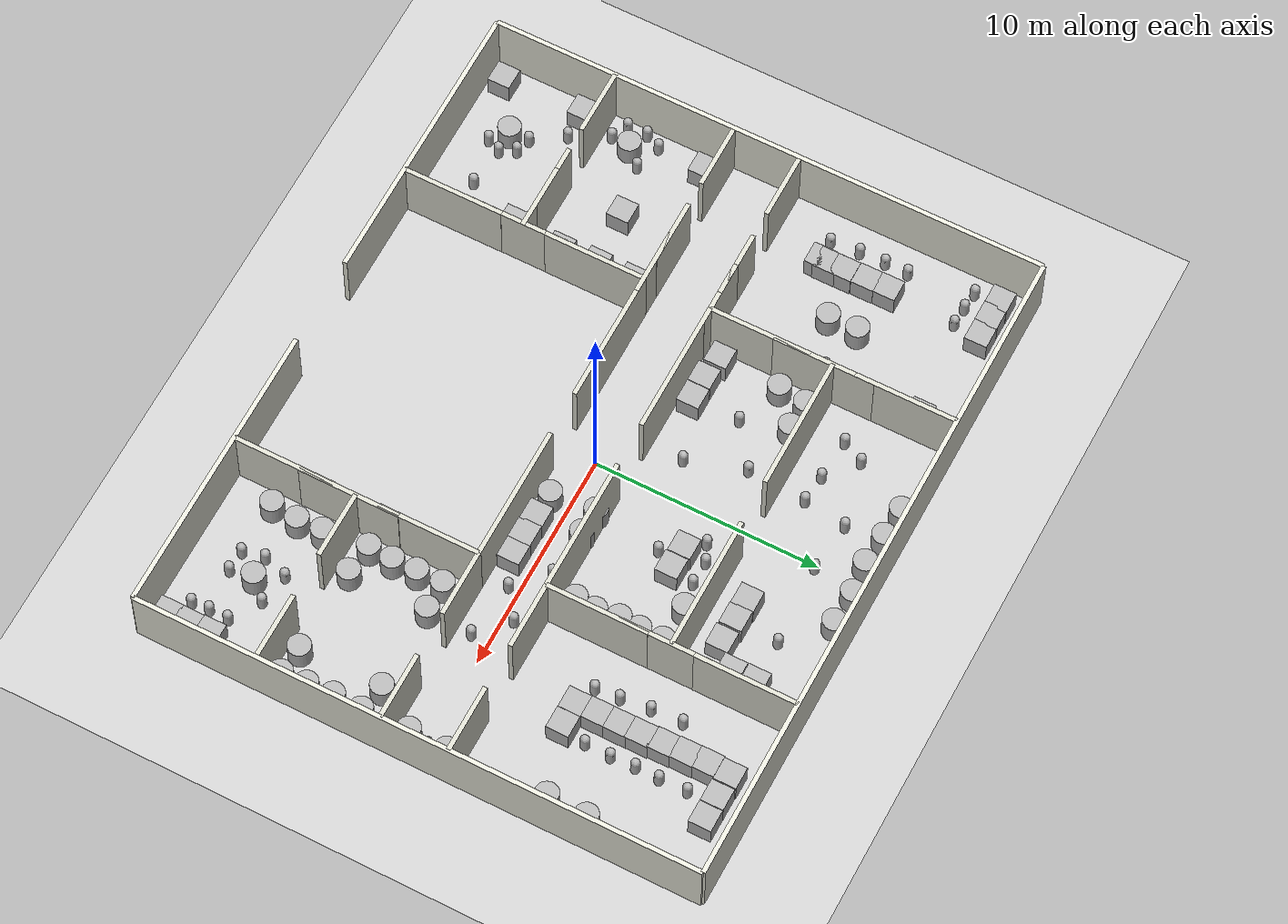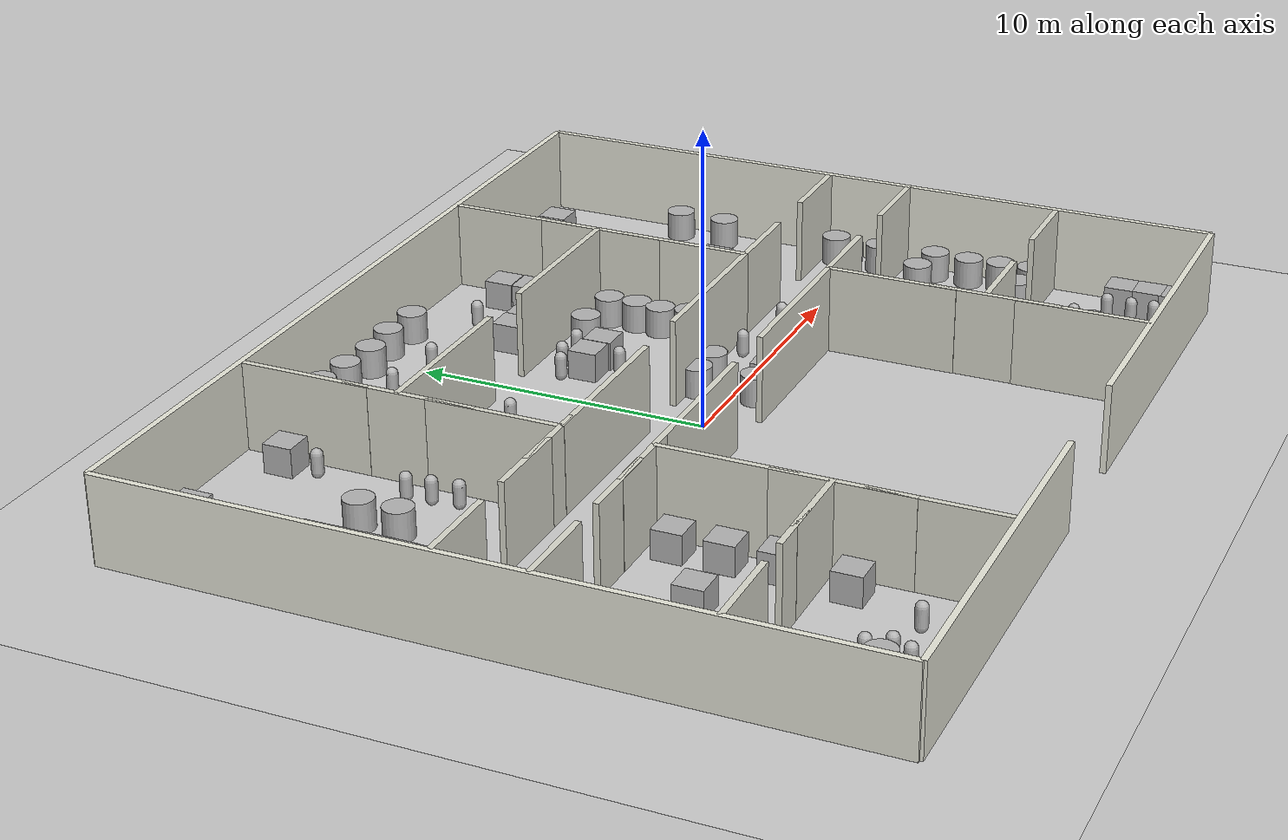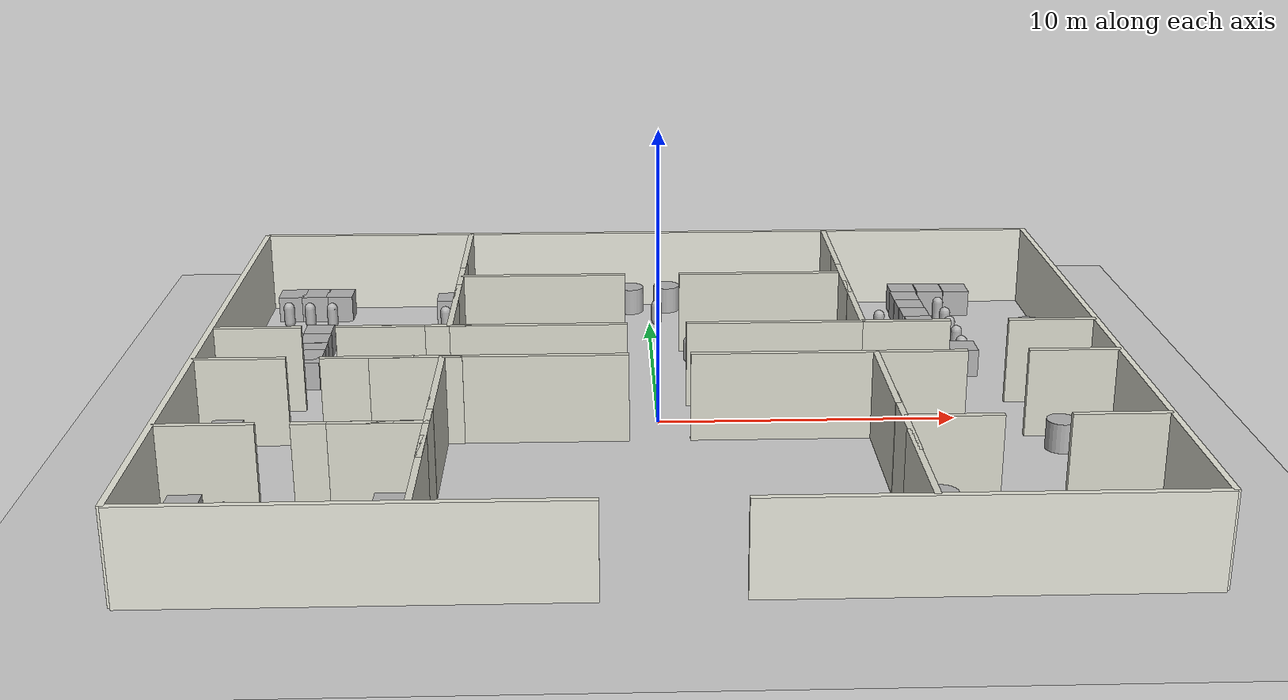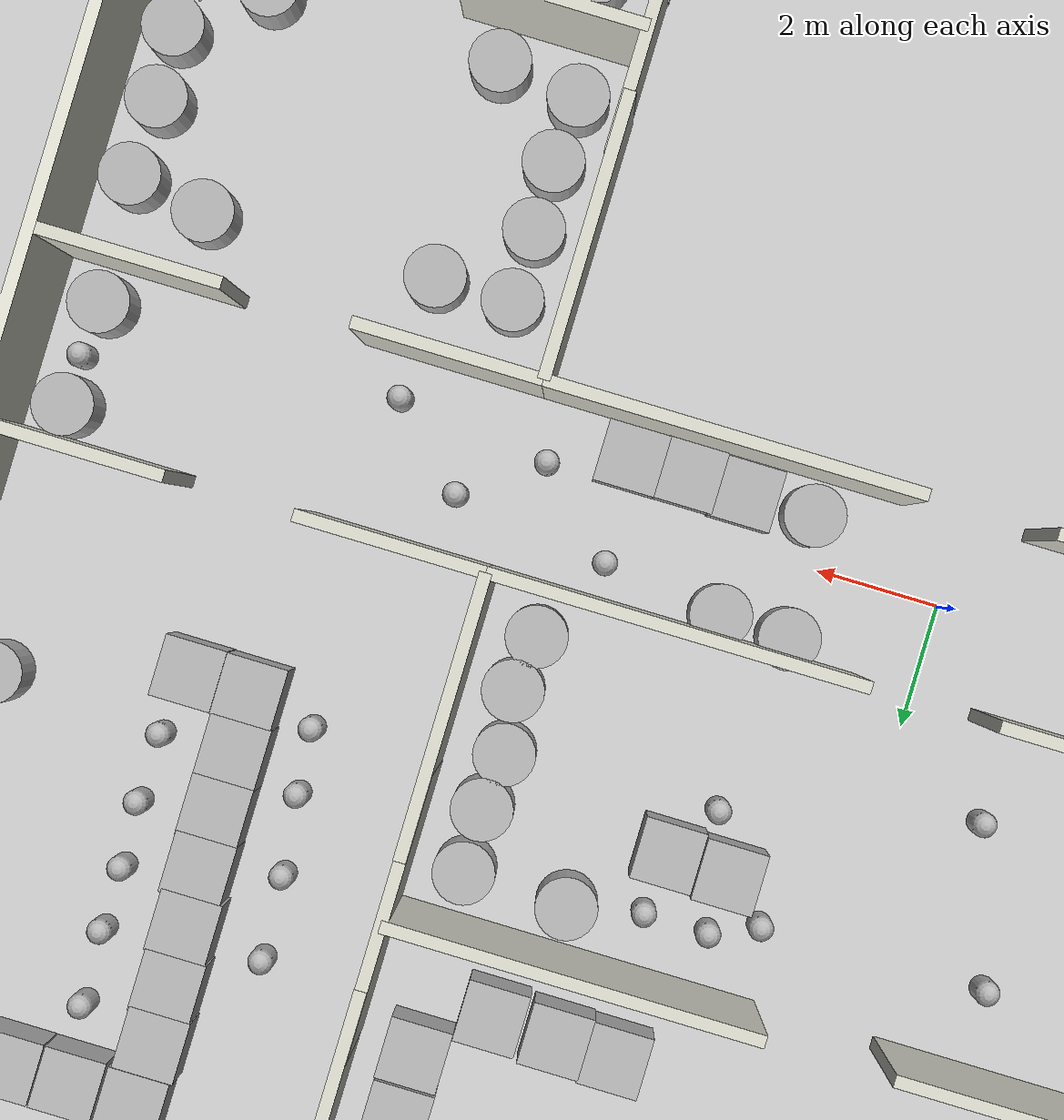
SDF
<?xml version="1.0"?>
<sdf version='1.10'>
  <world name='default'>
    <real_time_update_rate>1000</real_time_update_rate>
    <real_time_factor>1.0</real_time_factor>

    <scene>
      <shadows>false</shadows>
      <ambient>0.5 0.5 0.5 1</ambient>
      <background>0.8 0.8 0.8 1</background>
      <grid>false</grid>
    </scene>
    <physics type="ode">
      <real_time_update_rate>1000.0</real_time_update_rate>
      <max_step_size>0.010</max_step_size>
      <real_time_factor>1</real_time_factor>
      <ode>
        <solver>
          <type>quick</type>
          <iters>20</iters>
          <precon_iters>0</precon_iters>
          <sor>1.300000</sor>
          <use_dynamic_moi_rescaling>1</use_dynamic_moi_rescaling>
        </solver>
        <constraints>
          <cfm>0.0</cfm>
          <erp>0.2</erp>
          <contact_max_correcting_vel>100.000000</contact_max_correcting_vel>
          <contact_surface_layer>0.00100</contact_surface_layer>
        </constraints>
      </ode>
    </physics>

    <plugin
      filename="gz-sim-physics-system"
      name="gz::sim::systems::Physics">
    </plugin>
    <plugin
      filename="gz-sim-user-commands-system"
      name="gz::sim::systems::UserCommands">
    </plugin>
    <plugin
      filename="gz-sim-scene-broadcaster-system"
      name="gz::sim::systems::SceneBroadcaster">
    </plugin>
    <plugin
      filename="gz-sim-sensors-system"
      name="gz::sim::systems::Sensors">
      <render_engine>ogre2</render_engine>
      <background_color>0.8 0.8 0.8</background_color>
    </plugin>
    <plugin
      filename="gz-sim-imu-system"
      name="gz::sim::systems::Imu">
    </plugin>

    <model name='ground_plane'>
      <static>true</static>
      <pose>0 0 0 0 0 0</pose>
      <link name='link'>
        <collision name='collision'>
          <geometry>
            <plane>
              <normal>0 0 1</normal>
              <size>100 100</size>
            </plane>
          </geometry>
          <surface>
            <friction>
              <ode/>
            </friction>
            <bounce/>
            <contact/>
          </surface>
        </collision>
        <visual name='visual'>
          <geometry>
            <plane>
              <normal>0 0 1</normal>
              <size>100 100</size>
            </plane>
          </geometry>
          <material>
            <ambient>0.800000012 0.800000012 0.800000012 1</ambient>
            <diffuse>0.800000012 0.800000012 0.800000012 1</diffuse>
            <specular>0.100000001 0.100000001 0.100000001 1</specular>
          </material>
        </visual>
        <pose>0 0 0 0 0 0</pose>
        <inertial>
          <pose>0 0 0 0 0 0</pose>
          <mass>1</mass>
          <inertia>
            <ixx>1</ixx>
            <ixy>0</ixy>
            <ixz>0</ixz>
            <iyy>1</iyy>
            <iyz>0</iyz>
            <izz>1</izz>
          </inertia>
        </inertial>
        <enable_wind>false</enable_wind>
      </link>
      <self_collide>false</self_collide>
    </model>
    <model name='north_wall'>
      <static>true</static>
      <pose>0 12.5 1.5 0 0 0</pose>
      <link name='link'>
        <collision name='collision'>
          <geometry>
            <box>
              <size>30 0.20000000000000001 3</size>
            </box>
          </geometry>
          <surface>
            <friction>
              <ode/>
            </friction>
            <bounce/>
            <contact/>
          </surface>
        </collision>
        <visual name='visual'>
          <geometry>
            <box>
              <size>30 0.20000000000000001 3</size>
            </box>
          </geometry>
          <material>
            <ambient>0.899999976 0.899999976 0.850000024 1</ambient>
            <diffuse>0.899999976 0.899999976 0.850000024 1</diffuse>
          </material>
        </visual>
        <pose>0 0 0 0 0 0</pose>
        <inertial>
          <pose>0 0 0 0 0 0</pose>
          <mass>1</mass>
          <inertia>
            <ixx>1</ixx>
            <ixy>0</ixy>
            <ixz>0</ixz>
            <iyy>1</iyy>
            <iyz>0</iyz>
            <izz>1</izz>
          </inertia>
        </inertial>
        <enable_wind>false</enable_wind>
      </link>
      <self_collide>false</self_collide>
    </model>
    <model name='south_wall_west'>
      <static>true</static>
      <pose>-8.5 -12.5 1.5 0 0 0</pose>
      <link name='link'>
        <collision name='collision'>
          <geometry>
            <box>
              <size>13 0.20000000000000001 3</size>
            </box>
          </geometry>
          <surface>
            <friction>
              <ode/>
            </friction>
            <bounce/>
            <contact/>
          </surface>
        </collision>
        <visual name='visual'>
          <geometry>
            <box>
              <size>13 0.20000000000000001 3</size>
            </box>
          </geometry>
          <material>
            <ambient>0.899999976 0.899999976 0.850000024 1</ambient>
            <diffuse>0.899999976 0.899999976 0.850000024 1</diffuse>
          </material>
        </visual>
        <pose>0 0 0 0 0 0</pose>
        <inertial>
          <pose>0 0 0 0 0 0</pose>
          <mass>1</mass>
          <inertia>
            <ixx>1</ixx>
            <ixy>0</ixy>
            <ixz>0</ixz>
            <iyy>1</iyy>
            <iyz>0</iyz>
            <izz>1</izz>
          </inertia>
        </inertial>
        <enable_wind>false</enable_wind>
      </link>
      <self_collide>false</self_collide>
    </model>
    <model name='south_wall_east'>
      <static>true</static>
      <pose>8.5 -12.5 1.5 0 0 0</pose>
      <link name='link'>
        <collision name='collision'>
          <geometry>
            <box>
              <size>13 0.20000000000000001 3</size>
            </box>
          </geometry>
          <surface>
            <friction>
              <ode/>
            </friction>
            <bounce/>
            <contact/>
          </surface>
        </collision>
        <visual name='visual'>
          <geometry>
            <box>
              <size>13 0.20000000000000001 3</size>
            </box>
          </geometry>
          <material>
            <ambient>0.899999976 0.899999976 0.850000024 1</ambient>
            <diffuse>0.899999976 0.899999976 0.850000024 1</diffuse>
          </material>
        </visual>
        <pose>0 0 0 0 0 0</pose>
        <inertial>
          <pose>0 0 0 0 0 0</pose>
          <mass>1</mass>
          <inertia>
            <ixx>1</ixx>
            <ixy>0</ixy>
            <ixz>0</ixz>
            <iyy>1</iyy>
            <iyz>0</iyz>
            <izz>1</izz>
          </inertia>
        </inertial>
        <enable_wind>false</enable_wind>
      </link>
      <self_collide>false</self_collide>
    </model>
    <model name='east_wall'>
      <static>true</static>
      <pose>15 0 1.5 0 0 0</pose>
      <link name='link'>
        <collision name='collision'>
          <geometry>
            <box>
              <size>0.20000000000000001 25 3</size>
            </box>
          </geometry>
          <surface>
            <friction>
              <ode/>
            </friction>
            <bounce/>
            <contact/>
          </surface>
        </collision>
        <visual name='visual'>
          <geometry>
            <box>
              <size>0.20000000000000001 25 3</size>
            </box>
          </geometry>
          <material>
            <ambient>0.899999976 0.899999976 0.850000024 1</ambient>
            <diffuse>0.899999976 0.899999976 0.850000024 1</diffuse>
          </material>
        </visual>
        <pose>0 0 0 0 0 0</pose>
        <inertial>
          <pose>0 0 0 0 0 0</pose>
          <mass>1</mass>
          <inertia>
            <ixx>1</ixx>
            <ixy>0</ixy>
            <ixz>0</ixz>
            <iyy>1</iyy>
            <iyz>0</iyz>
            <izz>1</izz>
          </inertia>
        </inertial>
        <enable_wind>false</enable_wind>
      </link>
      <self_collide>false</self_collide>
    </model>
    <model name='west_wall'>
      <static>true</static>
      <pose>-15 0 1.5 0 0 0</pose>
      <link name='link'>
        <collision name='collision'>
          <geometry>
            <box>
              <size>0.20000000000000001 25 3</size>
            </box>
          </geometry>
          <surface>
            <friction>
              <ode/>
            </friction>
            <bounce/>
            <contact/>
          </surface>
        </collision>
        <visual name='visual'>
          <geometry>
            <box>
              <size>0.20000000000000001 25 3</size>
            </box>
          </geometry>
          <material>
            <ambient>0.899999976 0.899999976 0.850000024 1</ambient>
            <diffuse>0.899999976 0.899999976 0.850000024 1</diffuse>
          </material>
        </visual>
        <pose>0 0 0 0 0 0</pose>
        <inertial>
          <pose>0 0 0 0 0 0</pose>
          <mass>1</mass>
          <inertia>
            <ixx>1</ixx>
            <ixy>0</ixy>
            <ixz>0</ixz>
            <iyy>1</iyy>
            <iyz>0</iyz>
            <izz>1</izz>
          </inertia>
        </inertial>
        <enable_wind>false</enable_wind>
      </link>
      <self_collide>false</self_collide>
    </model>
    <model name='v_wall_m7_n1'>
      <static>true</static>
      <pose>-7 3.75 1.5 0 0 0</pose>
      <link name='link'>
        <collision name='collision'>
          <geometry>
            <box>
              <size>0.20000000000000001 4.5 3</size>
            </box>
          </geometry>
          <surface>
            <friction>
              <ode/>
            </friction>
            <bounce/>
            <contact/>
          </surface>
        </collision>
        <visual name='visual'>
          <geometry>
            <box>
              <size>0.20000000000000001 4.5 3</size>
            </box>
          </geometry>
          <material>
            <ambient>0.850000024 0.850000024 0.800000012 1</ambient>
            <diffuse>0.850000024 0.850000024 0.800000012 1</diffuse>
          </material>
        </visual>
        <pose>0 0 0 0 0 0</pose>
        <inertial>
          <pose>0 0 0 0 0 0</pose>
          <mass>1</mass>
          <inertia>
            <ixx>1</ixx>
            <ixy>0</ixy>
            <ixz>0</ixz>
            <iyy>1</iyy>
            <iyz>0</iyz>
            <izz>1</izz>
          </inertia>
        </inertial>
        <enable_wind>false</enable_wind>
      </link>
      <self_collide>false</self_collide>
    </model>
    <model name='v_wall_m7_n2'>
      <static>true</static>
      <pose>-7 10.25 1.5 0 0 0</pose>
      <link name='link'>
        <collision name='collision'>
          <geometry>
            <box>
              <size>0.20000000000000001 4.5 3</size>
            </box>
          </geometry>
          <surface>
            <friction>
              <ode/>
            </friction>
            <bounce/>
            <contact/>
          </surface>
        </collision>
        <visual name='visual'>
          <geometry>
            <box>
              <size>0.20000000000000001 4.5 3</size>
            </box>
          </geometry>
          <material>
            <ambient>0.850000024 0.850000024 0.800000012 1</ambient>
            <diffuse>0.850000024 0.850000024 0.800000012 1</diffuse>
          </material>
        </visual>
        <pose>0 0 0 0 0 0</pose>
        <inertial>
          <pose>0 0 0 0 0 0</pose>
          <mass>1</mass>
          <inertia>
            <ixx>1</ixx>
            <ixy>0</ixy>
            <ixz>0</ixz>
            <iyy>1</iyy>
            <iyz>0</iyz>
            <izz>1</izz>
          </inertia>
        </inertial>
        <enable_wind>false</enable_wind>
      </link>
      <self_collide>false</self_collide>
    </model>
    <model name='v_wall_m7_s1'>
      <static>true</static>
      <pose>-7 -3.75 1.5 0 0 0</pose>
      <link name='link'>
        <collision name='collision'>
          <geometry>
            <box>
              <size>0.20000000000000001 4.5 3</size>
            </box>
          </geometry>
          <surface>
            <friction>
              <ode/>
            </friction>
            <bounce/>
            <contact/>
          </surface>
        </collision>
        <visual name='visual'>
          <geometry>
            <box>
              <size>0.20000000000000001 4.5 3</size>
            </box>
          </geometry>
          <material>
            <ambient>0.850000024 0.850000024 0.800000012 1</ambient>
            <diffuse>0.850000024 0.850000024 0.800000012 1</diffuse>
          </material>
        </visual>
        <pose>0 0 0 0 0 0</pose>
        <inertial>
          <pose>0 0 0 0 0 0</pose>
          <mass>1</mass>
          <inertia>
            <ixx>1</ixx>
            <ixy>0</ixy>
            <ixz>0</ixz>
            <iyy>1</iyy>
            <iyz>0</iyz>
            <izz>1</izz>
          </inertia>
        </inertial>
        <enable_wind>false</enable_wind>
      </link>
      <self_collide>false</self_collide>
    </model>
    <model name='v_wall_m7_s2'>
      <static>true</static>
      <pose>-7 -10.25 1.5 0 0 0</pose>
      <link name='link'>
        <collision name='collision'>
          <geometry>
            <box>
              <size>0.20000000000000001 4.5 3</size>
            </box>
          </geometry>
          <surface>
            <friction>
              <ode/>
            </friction>
            <bounce/>
            <contact/>
          </surface>
        </collision>
        <visual name='visual'>
          <geometry>
            <box>
              <size>0.20000000000000001 4.5 3</size>
            </box>
          </geometry>
          <material>
            <ambient>0.850000024 0.850000024 0.800000012 1</ambient>
            <diffuse>0.850000024 0.850000024 0.800000012 1</diffuse>
          </material>
        </visual>
        <pose>0 0 0 0 0 0</pose>
        <inertial>
          <pose>0 0 0 0 0 0</pose>
          <mass>1</mass>
          <inertia>
            <ixx>1</ixx>
            <ixy>0</ixy>
            <ixz>0</ixz>
            <iyy>1</iyy>
            <iyz>0</iyz>
            <izz>1</izz>
          </inertia>
        </inertial>
        <enable_wind>false</enable_wind>
      </link>
      <self_collide>false</self_collide>
    </model>
    <model name='v_wall_p7_n1'>
      <static>true</static>
      <pose>7 3.75 1.5 0 0 0</pose>
      <link name='link'>
        <collision name='collision'>
          <geometry>
            <box>
              <size>0.20000000000000001 4.5 3</size>
            </box>
          </geometry>
          <surface>
            <friction>
              <ode/>
            </friction>
            <bounce/>
            <contact/>
          </surface>
        </collision>
        <visual name='visual'>
          <geometry>
            <box>
              <size>0.20000000000000001 4.5 3</size>
            </box>
          </geometry>
          <material>
            <ambient>0.850000024 0.850000024 0.800000012 1</ambient>
            <diffuse>0.850000024 0.850000024 0.800000012 1</diffuse>
          </material>
        </visual>
        <pose>0 0 0 0 0 0</pose>
        <inertial>
          <pose>0 0 0 0 0 0</pose>
          <mass>1</mass>
          <inertia>
            <ixx>1</ixx>
            <ixy>0</ixy>
            <ixz>0</ixz>
            <iyy>1</iyy>
            <iyz>0</iyz>
            <izz>1</izz>
          </inertia>
        </inertial>
        <enable_wind>false</enable_wind>
      </link>
      <self_collide>false</self_collide>
    </model>
    <model name='v_wall_p7_n2'>
      <static>true</static>
      <pose>7 10.25 1.5 0 0 0</pose>
      <link name='link'>
        <collision name='collision'>
          <geometry>
            <box>
              <size>0.20000000000000001 4.5 3</size>
            </box>
          </geometry>
          <surface>
            <friction>
              <ode/>
            </friction>
            <bounce/>
            <contact/>
          </surface>
        </collision>
        <visual name='visual'>
          <geometry>
            <box>
              <size>0.20000000000000001 4.5 3</size>
            </box>
          </geometry>
          <material>
            <ambient>0.850000024 0.850000024 0.800000012 1</ambient>
            <diffuse>0.850000024 0.850000024 0.800000012 1</diffuse>
          </material>
        </visual>
        <pose>0 0 0 0 0 0</pose>
        <inertial>
          <pose>0 0 0 0 0 0</pose>
          <mass>1</mass>
          <inertia>
            <ixx>1</ixx>
            <ixy>0</ixy>
            <ixz>0</ixz>
            <iyy>1</iyy>
            <iyz>0</iyz>
            <izz>1</izz>
          </inertia>
        </inertial>
        <enable_wind>false</enable_wind>
      </link>
      <self_collide>false</self_collide>
    </model>
    <model name='v_wall_p7_s1'>
      <static>true</static>
      <pose>7 -3.75 1.5 0 0 0</pose>
      <link name='link'>
        <collision name='collision'>
          <geometry>
            <box>
              <size>0.20000000000000001 4.5 3</size>
            </box>
          </geometry>
          <surface>
            <friction>
              <ode/>
            </friction>
            <bounce/>
            <contact/>
          </surface>
        </collision>
        <visual name='visual'>
          <geometry>
            <box>
              <size>0.20000000000000001 4.5 3</size>
            </box>
          </geometry>
          <material>
            <ambient>0.850000024 0.850000024 0.800000012 1</ambient>
            <diffuse>0.850000024 0.850000024 0.800000012 1</diffuse>
          </material>
        </visual>
        <pose>0 0 0 0 0 0</pose>
        <inertial>
          <pose>0 0 0 0 0 0</pose>
          <mass>1</mass>
          <inertia>
            <ixx>1</ixx>
            <ixy>0</ixy>
            <ixz>0</ixz>
            <iyy>1</iyy>
            <iyz>0</iyz>
            <izz>1</izz>
          </inertia>
        </inertial>
        <enable_wind>false</enable_wind>
      </link>
      <self_collide>false</self_collide>
    </model>
    <model name='v_wall_p7_s2'>
      <static>true</static>
      <pose>7 -10.25 1.5 0 0 0</pose>
      <link name='link'>
        <collision name='collision'>
          <geometry>
            <box>
              <size>0.20000000000000001 4.5 3</size>
            </box>
          </geometry>
          <surface>
            <friction>
              <ode/>
            </friction>
            <bounce/>
            <contact/>
          </surface>
        </collision>
        <visual name='visual'>
          <geometry>
            <box>
              <size>0.20000000000000001 4.5 3</size>
            </box>
          </geometry>
          <material>
            <ambient>0.850000024 0.850000024 0.800000012 1</ambient>
            <diffuse>0.850000024 0.850000024 0.800000012 1</diffuse>
          </material>
        </visual>
        <pose>0 0 0 0 0 0</pose>
        <inertial>
          <pose>0 0 0 0 0 0</pose>
          <mass>1</mass>
          <inertia>
            <ixx>1</ixx>
            <ixy>0</ixy>
            <ixz>0</ixz>
            <iyy>1</iyy>
            <iyz>0</iyz>
            <izz>1</izz>
          </inertia>
        </inertial>
        <enable_wind>false</enable_wind>
      </link>
      <self_collide>false</self_collide>
    </model>
    <model name='h_wall_p1_5_seg1_1'>
      <static>true</static>
      <pose>-13.468185424804688 1.5 1.5 0 0 0</pose>
      <link name='link'>
        <collision name='collision'>
          <geometry>
            <box>
              <size>3 0.20000000000000001 3</size>
            </box>
          </geometry>
          <surface>
            <friction>
              <ode/>
            </friction>
            <bounce/>
            <contact/>
          </surface>
        </collision>
        <visual name='visual'>
          <geometry>
            <box>
              <size>3 0.20000000000000001 3</size>
            </box>
          </geometry>
          <material>
            <ambient>0.850000024 0.850000024 0.800000012 1</ambient>
            <diffuse>0.850000024 0.850000024 0.800000012 1</diffuse>
          </material>
        </visual>
        <pose>0 0 0 0 0 0</pose>
        <inertial>
          <pose>0 0 0 0 0 0</pose>
          <mass>1</mass>
          <inertia>
            <ixx>1</ixx>
            <ixy>0</ixy>
            <ixz>0</ixz>
            <iyy>1</iyy>
            <iyz>0</iyz>
            <izz>1</izz>
          </inertia>
        </inertial>
        <enable_wind>false</enable_wind>
      </link>
      <self_collide>false</self_collide>
    </model>
    <model name='h_wall_p1_5_seg1_2'>
      <static>true</static>
      <pose>-9.3216009140014648 1.5 1.5 0 0 0</pose>
      <link name='link'>
        <collision name='collision'>
          <geometry>
            <box>
              <size>3 0.20000000000000001 3</size>
            </box>
          </geometry>
          <surface>
            <friction>
              <ode/>
            </friction>
            <bounce/>
            <contact/>
          </surface>
        </collision>
        <visual name='visual'>
          <geometry>
            <box>
              <size>3 0.20000000000000001 3</size>
            </box>
          </geometry>
          <material>
            <ambient>0.850000024 0.850000024 0.800000012 1</ambient>
            <diffuse>0.850000024 0.850000024 0.800000012 1</diffuse>
          </material>
        </visual>
        <pose>0 0 0 0 0 0</pose>
        <inertial>
          <pose>0 0 0 0 0 0</pose>
          <mass>1</mass>
          <inertia>
            <ixx>1</ixx>
            <ixy>0</ixy>
            <ixz>0</ixz>
            <iyy>1</iyy>
            <iyz>0</iyz>
            <izz>1</izz>
          </inertia>
        </inertial>
        <enable_wind>false</enable_wind>
      </link>
      <self_collide>false</self_collide>
    </model>
    <model name='h_wall_p1_5_seg2_1'>
      <static>true</static>
      <pose>-4 1.5 1.5 0 0 0</pose>
      <link name='link'>
        <collision name='collision'>
          <geometry>
            <box>
              <size>6 0.20000000000000001 3</size>
            </box>
          </geometry>
          <surface>
            <friction>
              <ode/>
            </friction>
            <bounce/>
            <contact/>
          </surface>
        </collision>
        <visual name='visual'>
          <geometry>
            <box>
              <size>6 0.20000000000000001 3</size>
            </box>
          </geometry>
          <material>
            <ambient>0.850000024 0.850000024 0.800000012 1</ambient>
            <diffuse>0.850000024 0.850000024 0.800000012 1</diffuse>
          </material>
        </visual>
        <pose>0 0 0 0 0 0</pose>
        <inertial>
          <pose>0 0 0 0 0 0</pose>
          <mass>1</mass>
          <inertia>
            <ixx>1</ixx>
            <ixy>0</ixy>
            <ixz>0</ixz>
            <iyy>1</iyy>
            <iyz>0</iyz>
            <izz>1</izz>
          </inertia>
        </inertial>
        <enable_wind>false</enable_wind>
      </link>
      <self_collide>false</self_collide>
    </model>
    <model name='h_wall_p1_5_seg2_2'>
      <static>true</static>
      <pose>4 1.5 1.5 0 0 0</pose>
      <link name='link'>
        <collision name='collision'>
          <geometry>
            <box>
              <size>6 0.20000000000000001 3</size>
            </box>
          </geometry>
          <surface>
            <friction>
              <ode/>
            </friction>
            <bounce/>
            <contact/>
          </surface>
        </collision>
        <visual name='visual'>
          <geometry>
            <box>
              <size>6 0.20000000000000001 3</size>
            </box>
          </geometry>
          <material>
            <ambient>0.850000024 0.850000024 0.800000012 1</ambient>
            <diffuse>0.850000024 0.850000024 0.800000012 1</diffuse>
          </material>
        </visual>
        <pose>0 0 0 0 0 0</pose>
        <inertial>
          <pose>0 0 0 0 0 0</pose>
          <mass>1</mass>
          <inertia>
            <ixx>1</ixx>
            <ixy>0</ixy>
            <ixz>0</ixz>
            <iyy>1</iyy>
            <iyz>0</iyz>
            <izz>1</izz>
          </inertia>
        </inertial>
        <enable_wind>false</enable_wind>
      </link>
      <self_collide>false</self_collide>
    </model>
    <model name='h_wall_p1_5_seg3_1'>
      <static>true</static>
      <pose>8.5 1.5 1.5 0 0 0</pose>
      <link name='link'>
        <collision name='collision'>
          <geometry>
            <box>
              <size>3 0.20000000000000001 3</size>
            </box>
          </geometry>
          <surface>
            <friction>
              <ode/>
            </friction>
            <bounce/>
            <contact/>
          </surface>
        </collision>
        <visual name='visual'>
          <geometry>
            <box>
              <size>3 0.20000000000000001 3</size>
            </box>
          </geometry>
          <material>
            <ambient>0.850000024 0.850000024 0.800000012 1</ambient>
            <diffuse>0.850000024 0.850000024 0.800000012 1</diffuse>
          </material>
        </visual>
        <pose>0 0 0 0 0 0</pose>
        <inertial>
          <pose>0 0 0 0 0 0</pose>
          <mass>1</mass>
          <inertia>
            <ixx>1</ixx>
            <ixy>0</ixy>
            <ixz>0</ixz>
            <iyy>1</iyy>
            <iyz>0</iyz>
            <izz>1</izz>
          </inertia>
        </inertial>
        <enable_wind>false</enable_wind>
      </link>
      <self_collide>false</self_collide>
    </model>
    <model name='h_wall_p1_5_seg3_2'>
      <static>true</static>
      <pose>13.5 1.5 1.5 0 0 0</pose>
      <link name='link'>
        <collision name='collision'>
          <geometry>
            <box>
              <size>3 0.20000000000000001 3</size>
            </box>
          </geometry>
          <surface>
            <friction>
              <ode/>
            </friction>
            <bounce/>
            <contact/>
          </surface>
        </collision>
        <visual name='visual'>
          <geometry>
            <box>
              <size>3 0.20000000000000001 3</size>
            </box>
          </geometry>
          <material>
            <ambient>0.850000024 0.850000024 0.800000012 1</ambient>
            <diffuse>0.850000024 0.850000024 0.800000012 1</diffuse>
          </material>
        </visual>
        <pose>0 0 0 0 0 0</pose>
        <inertial>
          <pose>0 0 0 0 0 0</pose>
          <mass>1</mass>
          <inertia>
            <ixx>1</ixx>
            <ixy>0</ixy>
            <ixz>0</ixz>
            <iyy>1</iyy>
            <iyz>0</iyz>
            <izz>1</izz>
          </inertia>
        </inertial>
        <enable_wind>false</enable_wind>
      </link>
      <self_collide>false</self_collide>
    </model>
    <model name='h_wall_m1_5_seg1_1'>
      <static>true</static>
      <pose>-13.5 -1.5 1.5 0 0 0</pose>
      <link name='link'>
        <collision name='collision'>
          <geometry>
            <box>
              <size>3 0.20000000000000001 3</size>
            </box>
          </geometry>
          <surface>
            <friction>
              <ode/>
            </friction>
            <bounce/>
            <contact/>
          </surface>
        </collision>
        <visual name='visual'>
          <geometry>
            <box>
              <size>3 0.20000000000000001 3</size>
            </box>
          </geometry>
          <material>
            <ambient>0.850000024 0.850000024 0.800000012 1</ambient>
            <diffuse>0.850000024 0.850000024 0.800000012 1</diffuse>
          </material>
        </visual>
        <pose>0 0 0 0 0 0</pose>
        <inertial>
          <pose>0 0 0 0 0 0</pose>
          <mass>1</mass>
          <inertia>
            <ixx>1</ixx>
            <ixy>0</ixy>
            <ixz>0</ixz>
            <iyy>1</iyy>
            <iyz>0</iyz>
            <izz>1</izz>
          </inertia>
        </inertial>
        <enable_wind>false</enable_wind>
      </link>
      <self_collide>false</self_collide>
    </model>
    <model name='h_wall_m1_5_seg1_2'>
      <static>true</static>
      <pose>-9.4130010604858398 -1.5 1.5 0 0 0</pose>
      <link name='link'>
        <collision name='collision'>
          <geometry>
            <box>
              <size>3 0.20000000000000001 3</size>
            </box>
          </geometry>
          <surface>
            <friction>
              <ode/>
            </friction>
            <bounce/>
            <contact/>
          </surface>
        </collision>
        <visual name='visual'>
          <geometry>
            <box>
              <size>3 0.20000000000000001 3</size>
            </box>
          </geometry>
          <material>
            <ambient>0.850000024 0.850000024 0.800000012 1</ambient>
            <diffuse>0.850000024 0.850000024 0.800000012 1</diffuse>
          </material>
        </visual>
        <pose>0 0 0 0 0 0</pose>
        <inertial>
          <pose>0 0 0 0 0 0</pose>
          <mass>1</mass>
          <inertia>
            <ixx>1</ixx>
            <ixy>0</ixy>
            <ixz>0</ixz>
            <iyy>1</iyy>
            <iyz>0</iyz>
            <izz>1</izz>
          </inertia>
        </inertial>
        <enable_wind>false</enable_wind>
      </link>
      <self_collide>false</self_collide>
    </model>
    <model name='h_wall_m1_5_seg2_1'>
      <static>true</static>
      <pose>-4 -1.5 1.5 0 0 0</pose>
      <link name='link'>
        <collision name='collision'>
          <geometry>
            <box>
              <size>6 0.20000000000000001 3</size>
            </box>
          </geometry>
          <surface>
            <friction>
              <ode/>
            </friction>
            <bounce/>
            <contact/>
          </surface>
        </collision>
        <visual name='visual'>
          <geometry>
            <box>
              <size>6 0.20000000000000001 3</size>
            </box>
          </geometry>
          <material>
            <ambient>0.850000024 0.850000024 0.800000012 1</ambient>
            <diffuse>0.850000024 0.850000024 0.800000012 1</diffuse>
          </material>
        </visual>
        <pose>0 0 0 0 0 0</pose>
        <inertial>
          <pose>0 0 0 0 0 0</pose>
          <mass>1</mass>
          <inertia>
            <ixx>1</ixx>
            <ixy>0</ixy>
            <ixz>0</ixz>
            <iyy>1</iyy>
            <iyz>0</iyz>
            <izz>1</izz>
          </inertia>
        </inertial>
        <enable_wind>false</enable_wind>
      </link>
      <self_collide>false</self_collide>
    </model>
    <model name='h_wall_m1_5_seg2_2'>
      <static>true</static>
      <pose>4 -1.5 1.5 0 0 0</pose>
      <link name='link'>
        <collision name='collision'>
          <geometry>
            <box>
              <size>6 0.20000000000000001 3</size>
            </box>
          </geometry>
          <surface>
            <friction>
              <ode/>
            </friction>
            <bounce/>
            <contact/>
          </surface>
        </collision>
        <visual name='visual'>
          <geometry>
            <box>
              <size>6 0.20000000000000001 3</size>
            </box>
          </geometry>
          <material>
            <ambient>0.850000024 0.850000024 0.800000012 1</ambient>
            <diffuse>0.850000024 0.850000024 0.800000012 1</diffuse>
          </material>
        </visual>
        <pose>0 0 0 0 0 0</pose>
        <inertial>
          <pose>0 0 0 0 0 0</pose>
          <mass>1</mass>
          <inertia>
            <ixx>1</ixx>
            <ixy>0</ixy>
            <ixz>0</ixz>
            <iyy>1</iyy>
            <iyz>0</iyz>
            <izz>1</izz>
          </inertia>
        </inertial>
        <enable_wind>false</enable_wind>
      </link>
      <self_collide>false</self_collide>
    </model>
    <model name='h_wall_m1_5_seg3_1'>
      <static>true</static>
      <pose>8.5 -1.5 1.5 0 0 0</pose>
      <link name='link'>
        <collision name='collision'>
          <geometry>
            <box>
              <size>3 0.20000000000000001 3</size>
            </box>
          </geometry>
          <surface>
            <friction>
              <ode/>
            </friction>
            <bounce/>
            <contact/>
          </surface>
        </collision>
        <visual name='visual'>
          <geometry>
            <box>
              <size>3 0.20000000000000001 3</size>
            </box>
          </geometry>
          <material>
            <ambient>0.850000024 0.850000024 0.800000012 1</ambient>
            <diffuse>0.850000024 0.850000024 0.800000012 1</diffuse>
          </material>
        </visual>
        <pose>0 0 0 0 0 0</pose>
        <inertial>
          <pose>0 0 0 0 0 0</pose>
          <mass>1</mass>
          <inertia>
            <ixx>1</ixx>
            <ixy>0</ixy>
            <ixz>0</ixz>
            <iyy>1</iyy>
            <iyz>0</iyz>
            <izz>1</izz>
          </inertia>
        </inertial>
        <enable_wind>false</enable_wind>
      </link>
      <self_collide>false</self_collide>
    </model>
    <model name='h_wall_m1_5_seg3_2'>
      <static>true</static>
      <pose>13.5 -1.5 1.5 0 0 0</pose>
      <link name='link'>
        <collision name='collision'>
          <geometry>
            <box>
              <size>3 0.20000000000000001 3</size>
            </box>
          </geometry>
          <surface>
            <friction>
              <ode/>
            </friction>
            <bounce/>
            <contact/>
          </surface>
        </collision>
        <visual name='visual'>
          <geometry>
            <box>
              <size>3 0.20000000000000001 3</size>
            </box>
          </geometry>
          <material>
            <ambient>0.850000024 0.850000024 0.800000012 1</ambient>
            <diffuse>0.850000024 0.850000024 0.800000012 1</diffuse>
          </material>
        </visual>
        <pose>0 0 0 0 0 0</pose>
        <inertial>
          <pose>0 0 0 0 0 0</pose>
          <mass>1</mass>
          <inertia>
            <ixx>1</ixx>
            <ixy>0</ixy>
            <ixz>0</ixz>
            <iyy>1</iyy>
            <iyz>0</iyz>
            <izz>1</izz>
          </inertia>
        </inertial>
        <enable_wind>false</enable_wind>
      </link>
      <self_collide>false</self_collide>
    </model>
    <model name='h_wall_p7_seg1'>
      <static>true</static>
      <pose>-4 7 1.5 0 0 0</pose>
      <link name='link'>
        <collision name='collision'>
          <geometry>
            <box>
              <size>6 0.20000000000000001 3</size>
            </box>
          </geometry>
          <surface>
            <friction>
              <ode/>
            </friction>
            <bounce/>
            <contact/>
          </surface>
        </collision>
        <visual name='visual'>
          <geometry>
            <box>
              <size>6 0.20000000000000001 3</size>
            </box>
          </geometry>
          <material>
            <ambient>0.850000024 0.850000024 0.800000012 1</ambient>
            <diffuse>0.850000024 0.850000024 0.800000012 1</diffuse>
          </material>
        </visual>
        <pose>0 0 0 0 0 0</pose>
        <inertial>
          <pose>0 0 0 0 0 0</pose>
          <mass>1</mass>
          <inertia>
            <ixx>1</ixx>
            <ixy>0</ixy>
            <ixz>0</ixz>
            <iyy>1</iyy>
            <iyz>0</iyz>
            <izz>1</izz>
          </inertia>
        </inertial>
        <enable_wind>false</enable_wind>
      </link>
      <self_collide>false</self_collide>
    </model>
    <model name='h_wall_p7_seg2'>
      <static>true</static>
      <pose>4 7 1.5 0 0 0</pose>
      <link name='link'>
        <collision name='collision'>
          <geometry>
            <box>
              <size>6 0.20000000000000001 3</size>
            </box>
          </geometry>
          <surface>
            <friction>
              <ode/>
            </friction>
            <bounce/>
            <contact/>
          </surface>
        </collision>
        <visual name='visual'>
          <geometry>
            <box>
              <size>6 0.20000000000000001 3</size>
            </box>
          </geometry>
          <material>
            <ambient>0.850000024 0.850000024 0.800000012 1</ambient>
            <diffuse>0.850000024 0.850000024 0.800000012 1</diffuse>
          </material>
        </visual>
        <pose>0 0 0 0 0 0</pose>
        <inertial>
          <pose>0 0 0 0 0 0</pose>
          <mass>1</mass>
          <inertia>
            <ixx>1</ixx>
            <ixy>0</ixy>
            <ixz>0</ixz>
            <iyy>1</iyy>
            <iyz>0</iyz>
            <izz>1</izz>
          </inertia>
        </inertial>
        <enable_wind>false</enable_wind>
      </link>
      <self_collide>false</self_collide>
    </model>
    <model name='h_wall_m7_seg1_1'>
      <static>true</static>
      <pose>-13.5 -7 1.5 0 0 0</pose>
      <link name='link'>
        <collision name='collision'>
          <geometry>
            <box>
              <size>3 0.20000000000000001 3</size>
            </box>
          </geometry>
          <surface>
            <friction>
              <ode/>
            </friction>
            <bounce/>
            <contact/>
          </surface>
        </collision>
        <visual name='visual'>
          <geometry>
            <box>
              <size>3 0.20000000000000001 3</size>
            </box>
          </geometry>
          <material>
            <ambient>0.850000024 0.850000024 0.800000012 1</ambient>
            <diffuse>0.850000024 0.850000024 0.800000012 1</diffuse>
          </material>
        </visual>
        <pose>0 0 0 0 0 0</pose>
        <inertial>
          <pose>0 0 0 0 0 0</pose>
          <mass>1</mass>
          <inertia>
            <ixx>1</ixx>
            <ixy>0</ixy>
            <ixz>0</ixz>
            <iyy>1</iyy>
            <iyz>0</iyz>
            <izz>1</izz>
          </inertia>
        </inertial>
        <enable_wind>false</enable_wind>
      </link>
      <self_collide>false</self_collide>
    </model>
    <model name='h_wall_m7_seg1_2'>
      <static>true</static>
      <pose>-9.4609384536743164 -7 1.5 0 0 0</pose>
      <link name='link'>
        <collision name='collision'>
          <geometry>
            <box>
              <size>3 0.20000000000000001 3</size>
            </box>
          </geometry>
          <surface>
            <friction>
              <ode/>
            </friction>
            <bounce/>
            <contact/>
          </surface>
        </collision>
        <visual name='visual'>
          <geometry>
            <box>
              <size>3 0.20000000000000001 3</size>
            </box>
          </geometry>
          <material>
            <ambient>0.850000024 0.850000024 0.800000012 1</ambient>
            <diffuse>0.850000024 0.850000024 0.800000012 1</diffuse>
          </material>
        </visual>
        <pose>0 0 0 0 0 0</pose>
        <inertial>
          <pose>0 0 0 0 0 0</pose>
          <mass>1</mass>
          <inertia>
            <ixx>1</ixx>
            <ixy>0</ixy>
            <ixz>0</ixz>
            <iyy>1</iyy>
            <iyz>0</iyz>
            <izz>1</izz>
          </inertia>
        </inertial>
        <enable_wind>false</enable_wind>
      </link>
      <self_collide>false</self_collide>
    </model>
    <model name='h_wall_m7_seg2_1'>
      <static>true</static>
      <pose>8.5 -7 1.5 0 0 0</pose>
      <link name='link'>
        <collision name='collision'>
          <geometry>
            <box>
              <size>3 0.20000000000000001 3</size>
            </box>
          </geometry>
          <surface>
            <friction>
              <ode/>
            </friction>
            <bounce/>
            <contact/>
          </surface>
        </collision>
        <visual name='visual'>
          <geometry>
            <box>
              <size>3 0.20000000000000001 3</size>
            </box>
          </geometry>
          <material>
            <ambient>0.850000024 0.850000024 0.800000012 1</ambient>
            <diffuse>0.850000024 0.850000024 0.800000012 1</diffuse>
          </material>
        </visual>
        <pose>0 0 0 0 0 0</pose>
        <inertial>
          <pose>0 0 0 0 0 0</pose>
          <mass>1</mass>
          <inertia>
            <ixx>1</ixx>
            <ixy>0</ixy>
            <ixz>0</ixz>
            <iyy>1</iyy>
            <iyz>0</iyz>
            <izz>1</izz>
          </inertia>
        </inertial>
        <enable_wind>false</enable_wind>
      </link>
      <self_collide>false</self_collide>
    </model>
    <model name='h_wall_m7_seg2_2'>
      <static>true</static>
      <pose>13.5 -7 1.5 0 0 0</pose>
      <link name='link'>
        <collision name='collision'>
          <geometry>
            <box>
              <size>3 0.20000000000000001 3</size>
            </box>
          </geometry>
          <surface>
            <friction>
              <ode/>
            </friction>
            <bounce/>
            <contact/>
          </surface>
        </collision>
        <visual name='visual'>
          <geometry>
            <box>
              <size>3 0.20000000000000001 3</size>
            </box>
          </geometry>
          <material>
            <ambient>0.850000024 0.850000024 0.800000012 1</ambient>
            <diffuse>0.850000024 0.850000024 0.800000012 1</diffuse>
          </material>
        </visual>
        <pose>0 0 0 0 0 0</pose>
        <inertial>
          <pose>0 0 0 0 0 0</pose>
          <mass>1</mass>
          <inertia>
            <ixx>1</ixx>
            <ixy>0</ixy>
            <ixz>0</ixz>
            <iyy>1</iyy>
            <iyz>0</iyz>
            <izz>1</izz>
          </inertia>
        </inertial>
        <enable_wind>false</enable_wind>
      </link>
      <self_collide>false</self_collide>
    </model>

    <model name='v_wall_m7_n1_1'>
      <static>true</static>
      <pose>-6.9964118067866385 6.624255076067092 1.5 0 0 0</pose>
      <link name='link'>
        <collision name='collision'>
          <geometry>
            <box>
              <size>0.20000000000000001 4.5 3</size>
            </box>
          </geometry>
          <surface>
            <friction>
              <ode/>
            </friction>
            <bounce/>
            <contact/>
          </surface>
        </collision>
        <visual name='visual'>
          <geometry>
            <box>
              <size>0.20000000000000001 4.5 3</size>
            </box>
          </geometry>
          <material>
            <ambient>0.850000024 0.850000024 0.800000012 1</ambient>
            <diffuse>0.850000024 0.850000024 0.800000012 1</diffuse>
          </material>
        </visual>
        <pose>0 0 0 0 0 0</pose>
        <inertial>
          <pose>0 0 0 0 0 0</pose>
          <mass>1</mass>
          <inertia>
            <ixx>1</ixx>
            <ixy>0</ixy>
            <ixz>0</ixz>
            <iyy>1</iyy>
            <iyz>0</iyz>
            <izz>1</izz>
          </inertia>
        </inertial>
        <enable_wind>false</enable_wind>
      </link>
      <self_collide>false</self_collide>
    </model>
    <model name='v_wall_m7_n1_2'>
      <static>true</static>
      <pose>6.9918575274214811 6.8837710487002894 1.5 0 0 0</pose>
      <link name='link'>
        <collision name='collision'>
          <geometry>
            <box>
              <size>0.20000000000000001 4.5 3</size>
            </box>
          </geometry>
          <surface>
            <friction>
              <ode/>
            </friction>
            <bounce/>
            <contact/>
          </surface>
        </collision>
        <visual name='visual'>
          <geometry>
            <box>
              <size>0.20000000000000001 4.5 3</size>
            </box>
          </geometry>
          <material>
            <ambient>0.850000024 0.850000024 0.800000012 1</ambient>
            <diffuse>0.850000024 0.850000024 0.800000012 1</diffuse>
          </material>
        </visual>
        <pose>0 0 0 0 0 0</pose>
        <inertial>
          <pose>0 0 0 0 0 0</pose>
          <mass>1</mass>
          <inertia>
            <ixx>1</ixx>
            <ixy>0</ixy>
            <ixz>0</ixz>
            <iyy>1</iyy>
            <iyz>0</iyz>
            <izz>1</izz>
          </inertia>
        </inertial>
        <enable_wind>false</enable_wind>
      </link>
      <self_collide>false</self_collide>
    </model>
    <model name='v_wall_m7_n1_3'>
      <static>true</static>
      <pose>7.0197264371027313 -7.2933113056837904 1.5 0 0 0</pose>
      <link name='link'>
        <collision name='collision'>
          <geometry>
            <box>
              <size>0.20000000000000001 4.5 3</size>
            </box>
          </geometry>
          <surface>
            <friction>
              <ode/>
            </friction>
            <bounce/>
            <contact/>
          </surface>
        </collision>
        <visual name='visual'>
          <geometry>
            <box>
              <size>0.20000000000000001 4.5 3</size>
            </box>
          </geometry>
          <material>
            <ambient>0.850000024 0.850000024 0.800000012 1</ambient>
            <diffuse>0.850000024 0.850000024 0.800000012 1</diffuse>
          </material>
        </visual>
        <pose>0 0 0 0 0 0</pose>
        <inertial>
          <pose>0 0 0 0 0 0</pose>
          <mass>1</mass>
          <inertia>
            <ixx>1</ixx>
            <ixy>0</ixy>
            <ixz>0</ixz>
            <iyy>1</iyy>
            <iyz>0</iyz>
            <izz>1</izz>
          </inertia>
        </inertial>
        <enable_wind>false</enable_wind>
      </link>
      <self_collide>false</self_collide>
    </model>
    <model name='v_wall_m7_n1_4'>
      <static>true</static>
      <pose>-7.0079871012456065 -7.3319602976590579 1.5 0 0 0</pose>
      <link name='link'>
        <collision name='collision'>
          <geometry>
            <box>
              <size>0.20000000000000001 4.5 3</size>
            </box>
          </geometry>
          <surface>
            <friction>
              <ode/>
            </friction>
            <bounce/>
            <contact/>
          </surface>
        </collision>
        <visual name='visual'>
          <geometry>
            <box>
              <size>0.20000000000000001 4.5 3</size>
            </box>
          </geometry>
          <material>
            <ambient>0.850000024 0.850000024 0.800000012 1</ambient>
            <diffuse>0.850000024 0.850000024 0.800000012 1</diffuse>
          </material>
        </visual>
        <pose>0 0 0 0 0 0</pose>
        <inertial>
          <pose>0 0 0 0 0 0</pose>
          <mass>1</mass>
          <inertia>
            <ixx>1</ixx>
            <ixy>0</ixy>
            <ixz>0</ixz>
            <iyy>1</iyy>
            <iyz>0</iyz>
            <izz>1</izz>
          </inertia>
        </inertial>
        <enable_wind>false</enable_wind>
      </link>
      <self_collide>false</self_collide>
    </model>

    <model name='h_wall_m7_seg1_2_1'>
      <static>true</static>
      <pose>-8.4126858874969415 -7.0020169151065623 1.5 0 0 0</pose>
      <link name='link'>
        <collision name='collision'>
          <geometry>
            <box>
              <size>3 0.20000000000000001 3</size>
            </box>
          </geometry>
          <surface>
            <friction>
              <ode/>
            </friction>
            <bounce/>
            <contact/>
          </surface>
        </collision>
        <visual name='visual'>
          <geometry>
            <box>
              <size>3 0.20000000000000001 3</size>
            </box>
          </geometry>
          <material>
            <ambient>0.850000024 0.850000024 0.800000012 1</ambient>
            <diffuse>0.850000024 0.850000024 0.800000012 1</diffuse>
          </material>
        </visual>
        <pose>0 0 0 0 0 0</pose>
        <inertial>
          <pose>0 0 0 0 0 0</pose>
          <mass>1</mass>
          <inertia>
            <ixx>1</ixx>
            <ixy>0</ixy>
            <ixz>0</ixz>
            <iyy>1</iyy>
            <iyz>0</iyz>
            <izz>1</izz>
          </inertia>
        </inertial>
        <enable_wind>false</enable_wind>
      </link>
      <self_collide>false</self_collide>
    </model>
    <model name='h_wall_m7_seg1_2_2'>
      <static>true</static>
      <pose>-7.8554236444477405 -1.5075810255903455 1.5 0 0 0</pose>
      <link name='link'>
        <collision name='collision'>
          <geometry>
            <box>
              <size>3 0.20000000000000001 3</size>
            </box>
          </geometry>
          <surface>
            <friction>
              <ode/>
            </friction>
            <bounce/>
            <contact/>
          </surface>
        </collision>
        <visual name='visual'>
          <geometry>
            <box>
              <size>3 0.20000000000000001 3</size>
            </box>
          </geometry>
          <material>
            <ambient>0.850000024 0.850000024 0.800000012 1</ambient>
            <diffuse>0.850000024 0.850000024 0.800000012 1</diffuse>
          </material>
        </visual>
        <pose>0 0 0 0 0 0</pose>
        <inertial>
          <pose>0 0 0 0 0 0</pose>
          <mass>1</mass>
          <inertia>
            <ixx>1</ixx>
            <ixy>0</ixy>
            <ixz>0</ixz>
            <iyy>1</iyy>
            <iyz>0</iyz>
            <izz>1</izz>
          </inertia>
        </inertial>
        <enable_wind>false</enable_wind>
      </link>
      <self_collide>false</self_collide>
    </model>
    <model name='h_wall_m7_seg1_2_3'>
      <static>true</static>
      <pose>-7.7709027079527218 1.5024162647538466 1.5 0 0 0</pose>
      <link name='link'>
        <collision name='collision'>
          <geometry>
            <box>
              <size>3 0.20000000000000001 3</size>
            </box>
          </geometry>
          <surface>
            <friction>
              <ode/>
            </friction>
            <bounce/>
            <contact/>
          </surface>
        </collision>
        <visual name='visual'>
          <geometry>
            <box>
              <size>3 0.20000000000000001 3</size>
            </box>
          </geometry>
          <material>
            <ambient>0.850000024 0.850000024 0.800000012 1</ambient>
            <diffuse>0.850000024 0.850000024 0.800000012 1</diffuse>
          </material>
        </visual>
        <pose>0 0 0 0 0 0</pose>
        <inertial>
          <pose>0 0 0 0 0 0</pose>
          <mass>1</mass>
          <inertia>
            <ixx>1</ixx>
            <ixy>0</ixy>
            <ixz>0</ixz>
            <iyy>1</iyy>
            <iyz>0</iyz>
            <izz>1</izz>
          </inertia>
        </inertial>
        <enable_wind>false</enable_wind>
      </link>
      <self_collide>false</self_collide>
    </model>

    <model name='capsule'>
      <static>true</static>
      <pose>-9.067462361217947 -10.474388385116022 0.5 0 0 0</pose>
      <link name='capsule_link'>
        <inertial>
          <inertia>
            <ixx>0.074153999999999998</ixx>
            <ixy>0</ixy>
            <ixz>0</ixz>
            <iyy>0.074153999999999998</iyy>
            <iyz>0</iyz>
            <izz>0.018769000000000001</izz>
          </inertia>
          <mass>1</mass>
          <pose>0 0 0 0 0 0</pose>
        </inertial>
        <collision name='capsule_collision'>
          <geometry>
            <capsule>
              <radius>0.20000000000000001</radius>
              <length>0.59999999999999998</length>
            </capsule>
          </geometry>
          <surface>
            <friction>
              <ode/>
            </friction>
            <bounce/>
            <contact/>
          </surface>
        </collision>
        <visual name='capsule_visual'>
          <geometry>
            <capsule>
              <radius>0.20000000000000001</radius>
              <length>0.59999999999999998</length>
            </capsule>
          </geometry>
          <material>
            <ambient>0.300000012 0.300000012 0.300000012 1</ambient>
            <diffuse>0.699999988 0.699999988 0.699999988 1</diffuse>
            <specular>1 1 1 1</specular>
          </material>
        </visual>
        <pose>0 0 0 0 0 0</pose>
        <enable_wind>false</enable_wind>
      </link>
      <static>false</static>
      <self_collide>false</self_collide>
    </model>
    <model name='capsule_0'>
      <static>true</static>
      <pose>-12.843148425765175 -8.0715135897866794 0.5 0 0 0</pose>
      <link name='capsule_link'>
        <inertial>
          <inertia>
            <ixx>0.074153999999999998</ixx>
            <ixy>0</ixy>
            <ixz>0</ixz>
            <iyy>0.074153999999999998</iyy>
            <iyz>0</iyz>
            <izz>0.018769000000000001</izz>
          </inertia>
          <mass>1</mass>
          <pose>0 0 0 0 0 0</pose>
        </inertial>
        <collision name='capsule_collision'>
          <geometry>
            <capsule>
              <radius>0.20000000000000001</radius>
              <length>0.59999999999999998</length>
            </capsule>
          </geometry>
          <surface>
            <friction>
              <ode/>
            </friction>
            <bounce/>
            <contact/>
          </surface>
        </collision>
        <visual name='capsule_visual'>
          <geometry>
            <capsule>
              <radius>0.20000000000000001</radius>
              <length>0.59999999999999998</length>
            </capsule>
          </geometry>
          <material>
            <ambient>0.300000012 0.300000012 0.300000012 1</ambient>
            <diffuse>0.699999988 0.699999988 0.699999988 1</diffuse>
            <specular>1 1 1 1</specular>
          </material>
        </visual>
        <pose>0 0 0 0 0 0</pose>
        <enable_wind>false</enable_wind>
      </link>
      <static>false</static>
      <self_collide>false</self_collide>
    </model>
    <model name='cylinder'>
      <static>true</static>
      <pose>-11.84359305769536 -10.279714638927015 0.5 0 0 0</pose>
      <link name='cylinder_link'>
        <inertial>
          <inertia>
            <ixx>0.14580000000000001</ixx>
            <ixy>0</ixy>
            <ixz>0</ixz>
            <iyy>0.14580000000000001</iyy>
            <iyz>0</iyz>
            <izz>0.125</izz>
          </inertia>
          <mass>1</mass>
          <pose>0 0 0 0 0 0</pose>
        </inertial>
        <collision name='cylinder_collision'>
          <geometry>
            <cylinder>
              <radius>0.5</radius>
              <length>1</length>
            </cylinder>
          </geometry>
          <surface>
            <friction>
              <ode/>
            </friction>
            <bounce/>
            <contact/>
          </surface>
        </collision>
        <visual name='cylinder_visual'>
          <geometry>
            <cylinder>
              <radius>0.5</radius>
              <length>1</length>
            </cylinder>
          </geometry>
          <material>
            <ambient>0.300000012 0.300000012 0.300000012 1</ambient>
            <diffuse>0.699999988 0.699999988 0.699999988 1</diffuse>
            <specular>1 1 1 1</specular>
          </material>
        </visual>
        <pose>0 0 0 0 0 0</pose>
        <enable_wind>false</enable_wind>
      </link>
      <static>false</static>
      <self_collide>false</self_collide>
    </model>
    <model name='capsule_1'>
      <static>true</static>
      <pose>-11.183160962634393 -10.9036380439401 0.5 0 0 0</pose>
      <link name='capsule_link'>
        <inertial>
          <inertia>
            <ixx>0.074153999999999998</ixx>
            <ixy>0</ixy>
            <ixz>0</ixz>
            <iyy>0.074153999999999998</iyy>
            <iyz>0</iyz>
            <izz>0.018769000000000001</izz>
          </inertia>
          <mass>1</mass>
          <pose>0 0 0 0 0 0</pose>
        </inertial>
        <collision name='capsule_collision'>
          <geometry>
            <capsule>
              <radius>0.20000000000000001</radius>
              <length>0.59999999999999998</length>
            </capsule>
          </geometry>
          <surface>
            <friction>
              <ode/>
            </friction>
            <bounce/>
            <contact/>
          </surface>
        </collision>
        <visual name='capsule_visual'>
          <geometry>
            <capsule>
              <radius>0.20000000000000001</radius>
              <length>0.59999999999999998</length>
            </capsule>
          </geometry>
          <material>
            <ambient>0.300000012 0.300000012 0.300000012 1</ambient>
            <diffuse>0.699999988 0.699999988 0.699999988 1</diffuse>
            <specular>1 1 1 1</specular>
          </material>
        </visual>
        <pose>0 0 0 0 0 0</pose>
        <enable_wind>false</enable_wind>
      </link>
      <static>false</static>
      <self_collide>false</self_collide>
    </model>
    <model name='capsule_2'>
      <static>true</static>
      <pose>-10.880404267954967 -10.277190470985687 0.5 0 0 0</pose>
      <link name='capsule_link'>
        <inertial>
          <inertia>
            <ixx>0.074153999999999998</ixx>
            <ixy>0</ixy>
            <ixz>0</ixz>
            <iyy>0.074153999999999998</iyy>
            <iyz>0</iyz>
            <izz>0.018769000000000001</izz>
          </inertia>
          <mass>1</mass>
          <pose>0 0 0 0 0 0</pose>
        </inertial>
        <collision name='capsule_collision'>
          <geometry>
            <capsule>
              <radius>0.20000000000000001</radius>
              <length>0.59999999999999998</length>
            </capsule>
          </geometry>
          <surface>
            <friction>
              <ode/>
            </friction>
            <bounce/>
            <contact/>
          </surface>
        </collision>
        <visual name='capsule_visual'>
          <geometry>
            <capsule>
              <radius>0.20000000000000001</radius>
              <length>0.59999999999999998</length>
            </capsule>
          </geometry>
          <material>
            <ambient>0.300000012 0.300000012 0.300000012 1</ambient>
            <diffuse>0.699999988 0.699999988 0.699999988 1</diffuse>
            <specular>1 1 1 1</specular>
          </material>
        </visual>
        <pose>0 0 0 0 0 0</pose>
        <enable_wind>false</enable_wind>
      </link>
      <static>false</static>
      <self_collide>false</self_collide>
    </model>
    <model name='capsule_3'>
      <static>true</static>
      <pose>-11.233941003786308 -9.6075485591413941 0.5 0 0 0</pose>
      <link name='capsule_link'>
        <inertial>
          <inertia>
            <ixx>0.074153999999999998</ixx>
            <ixy>0</ixy>
            <ixz>0</ixz>
            <iyy>0.074153999999999998</iyy>
            <iyz>0</iyz>
            <izz>0.018769000000000001</izz>
          </inertia>
          <mass>1</mass>
          <pose>0 0 0 0 0 0</pose>
        </inertial>
        <collision name='capsule_collision'>
          <geometry>
            <capsule>
              <radius>0.20000000000000001</radius>
              <length>0.59999999999999998</length>
            </capsule>
          </geometry>
          <surface>
            <friction>
              <ode/>
            </friction>
            <bounce/>
            <contact/>
          </surface>
        </collision>
        <visual name='capsule_visual'>
          <geometry>
            <capsule>
              <radius>0.20000000000000001</radius>
              <length>0.59999999999999998</length>
            </capsule>
          </geometry>
          <material>
            <ambient>0.300000012 0.300000012 0.300000012 1</ambient>
            <diffuse>0.699999988 0.699999988 0.699999988 1</diffuse>
            <specular>1 1 1 1</specular>
          </material>
        </visual>
        <pose>0 0 0 0 0 0</pose>
        <enable_wind>false</enable_wind>
      </link>
      <static>false</static>
      <self_collide>false</self_collide>
    </model>
    <model name='capsule_4'>
      <static>true</static>
      <pose>-11.917475067567963 -9.4087088568049886 0.5 0 0 0</pose>
      <link name='capsule_link'>
        <inertial>
          <inertia>
            <ixx>0.074153999999999998</ixx>
            <ixy>0</ixy>
            <ixz>0</ixz>
            <iyy>0.074153999999999998</iyy>
            <iyz>0</iyz>
            <izz>0.018769000000000001</izz>
          </inertia>
          <mass>1</mass>
          <pose>0 0 0 0 0 0</pose>
        </inertial>
        <collision name='capsule_collision'>
          <geometry>
            <capsule>
              <radius>0.20000000000000001</radius>
              <length>0.59999999999999998</length>
            </capsule>
          </geometry>
          <surface>
            <friction>
              <ode/>
            </friction>
            <bounce/>
            <contact/>
          </surface>
        </collision>
        <visual name='capsule_visual'>
          <geometry>
            <capsule>
              <radius>0.20000000000000001</radius>
              <length>0.59999999999999998</length>
            </capsule>
          </geometry>
          <material>
            <ambient>0.300000012 0.300000012 0.300000012 1</ambient>
            <diffuse>0.699999988 0.699999988 0.699999988 1</diffuse>
            <specular>1 1 1 1</specular>
          </material>
        </visual>
        <pose>0 0 0 0 0 0</pose>
        <enable_wind>false</enable_wind>
      </link>
      <static>false</static>
      <self_collide>false</self_collide>
    </model>
    <model name='box'>
      <static>true</static>
      <pose>-13.94106556582285 -11.666850543528293 0.5 0 0 0</pose>
      <link name='box_link'>
        <inertial>
          <inertia>
            <ixx>0.16666</ixx>
            <ixy>0</ixy>
            <ixz>0</ixz>
            <iyy>0.16666</iyy>
            <iyz>0</iyz>
            <izz>0.16666</izz>
          </inertia>
          <mass>1</mass>
          <pose>0 0 0 0 0 0</pose>
        </inertial>
        <collision name='box_collision'>
          <geometry>
            <box>
              <size>1 1 1</size>
            </box>
          </geometry>
          <surface>
            <friction>
              <ode/>
            </friction>
            <bounce/>
            <contact/>
          </surface>
        </collision>
        <visual name='box_visual'>
          <geometry>
            <box>
              <size>1 1 1</size>
            </box>
          </geometry>
          <material>
            <ambient>0.300000012 0.300000012 0.300000012 1</ambient>
            <diffuse>0.699999988 0.699999988 0.699999988 1</diffuse>
            <specular>1 1 1 1</specular>
          </material>
        </visual>
        <pose>0 0 0 0 0 0</pose>
        <enable_wind>false</enable_wind>
      </link>
      <static>false</static>
      <self_collide>false</self_collide>
    </model>
    <model name='box_0'>
      <static>true</static>
      <pose>-8.0485249547837707 -8.0638953320809392 0.5 0 0 0</pose>
      <link name='box_link'>
        <inertial>
          <inertia>
            <ixx>0.16666</ixx>
            <ixy>0</ixy>
            <ixz>0</ixz>
            <iyy>0.16666</iyy>
            <iyz>0</iyz>
            <izz>0.16666</izz>
          </inertia>
          <mass>1</mass>
          <pose>0 0 0 0 0 0</pose>
        </inertial>
        <collision name='box_collision'>
          <geometry>
            <box>
              <size>1 1 1</size>
            </box>
          </geometry>
          <surface>
            <friction>
              <ode/>
            </friction>
            <bounce/>
            <contact/>
          </surface>
        </collision>
        <visual name='box_visual'>
          <geometry>
            <box>
              <size>1 1 1</size>
            </box>
          </geometry>
          <material>
            <ambient>0.300000012 0.300000012 0.300000012 1</ambient>
            <diffuse>0.699999988 0.699999988 0.699999988 1</diffuse>
            <specular>1 1 1 1</specular>
          </material>
        </visual>
        <pose>0 0 0 0 0 0</pose>
        <enable_wind>false</enable_wind>
      </link>
      <static>false</static>
      <self_collide>false</self_collide>
    </model>
    <model name='box_1'>
      <static>true</static>
      <pose>-14.058826356557514 -8.0066225338777386 0.5 0 0 0</pose>
      <link name='box_link'>
        <inertial>
          <inertia>
            <ixx>0.16666</ixx>
            <ixy>0</ixy>
            <ixz>0</ixz>
            <iyy>0.16666</iyy>
            <iyz>0</iyz>
            <izz>0.16666</izz>
          </inertia>
          <mass>1</mass>
          <pose>0 0 0 0 0 0</pose>
        </inertial>
        <collision name='box_collision'>
          <geometry>
            <box>
              <size>1 1 1</size>
            </box>
          </geometry>
          <surface>
            <friction>
              <ode/>
            </friction>
            <bounce/>
            <contact/>
          </surface>
        </collision>
        <visual name='box_visual'>
          <geometry>
            <box>
              <size>1 1 1</size>
            </box>
          </geometry>
          <material>
            <ambient>0.300000012 0.300000012 0.300000012 1</ambient>
            <diffuse>0.699999988 0.699999988 0.699999988 1</diffuse>
            <specular>1 1 1 1</specular>
          </material>
        </visual>
        <pose>0 0 0 0 0 0</pose>
        <enable_wind>false</enable_wind>
      </link>
      <static>false</static>
      <self_collide>false</self_collide>
    </model>
    <model name='cylinder_0'>
      <static>true</static>
      <pose>-13.530111643639829 -5.567035307923792 0.5 0 0 0</pose>
      <link name='cylinder_link'>
        <inertial>
          <inertia>
            <ixx>0.14580000000000001</ixx>
            <ixy>0</ixy>
            <ixz>0</ixz>
            <iyy>0.14580000000000001</iyy>
            <iyz>0</iyz>
            <izz>0.125</izz>
          </inertia>
          <mass>1</mass>
          <pose>0 0 0 0 0 0</pose>
        </inertial>
        <collision name='cylinder_collision'>
          <geometry>
            <cylinder>
              <radius>0.5</radius>
              <length>1</length>
            </cylinder>
          </geometry>
          <surface>
            <friction>
              <ode/>
            </friction>
            <bounce/>
            <contact/>
          </surface>
        </collision>
        <visual name='cylinder_visual'>
          <geometry>
            <cylinder>
              <radius>0.5</radius>
              <length>1</length>
            </cylinder>
          </geometry>
          <material>
            <ambient>0.300000012 0.300000012 0.300000012 1</ambient>
            <diffuse>0.699999988 0.699999988 0.699999988 1</diffuse>
            <specular>1 1 1 1</specular>
          </material>
        </visual>
        <pose>0 0 0 0 0 0</pose>
        <enable_wind>false</enable_wind>
      </link>
      <static>false</static>
      <self_collide>false</self_collide>
    </model>
    <model name='capsule_5'>
      <static>true</static>
      <pose>-14.085505936820644 -4.4913171230011599 0.5 0 0 0</pose>
      <link name='capsule_link'>
        <inertial>
          <inertia>
            <ixx>0.074153999999999998</ixx>
            <ixy>0</ixy>
            <ixz>0</ixz>
            <iyy>0.074153999999999998</iyy>
            <iyz>0</iyz>
            <izz>0.018769000000000001</izz>
          </inertia>
          <mass>1</mass>
          <pose>0 0 0 0 0 0</pose>
        </inertial>
        <collision name='capsule_collision'>
          <geometry>
            <capsule>
              <radius>0.20000000000000001</radius>
              <length>0.59999999999999998</length>
            </capsule>
          </geometry>
          <surface>
            <friction>
              <ode/>
            </friction>
            <bounce/>
            <contact/>
          </surface>
        </collision>
        <visual name='capsule_visual'>
          <geometry>
            <capsule>
              <radius>0.20000000000000001</radius>
              <length>0.59999999999999998</length>
            </capsule>
          </geometry>
          <material>
            <ambient>0.300000012 0.300000012 0.300000012 1</ambient>
            <diffuse>0.699999988 0.699999988 0.699999988 1</diffuse>
            <specular>1 1 1 1</specular>
          </material>
        </visual>
        <pose>0 0 0 0 0 0</pose>
        <enable_wind>false</enable_wind>
      </link>
      <static>false</static>
      <self_collide>false</self_collide>
    </model>
    <model name='capsule_6'>
      <static>true</static>
      <pose>-12.869999638893912 -4.8715380689727237 0.5 0 0 0</pose>
      <link name='capsule_link'>
        <inertial>
          <inertia>
            <ixx>0.074153999999999998</ixx>
            <ixy>0</ixy>
            <ixz>0</ixz>
            <iyy>0.074153999999999998</iyy>
            <iyz>0</iyz>
            <izz>0.018769000000000001</izz>
          </inertia>
          <mass>1</mass>
          <pose>0 0 0 0 0 0</pose>
        </inertial>
        <collision name='capsule_collision'>
          <geometry>
            <capsule>
              <radius>0.20000000000000001</radius>
              <length>0.59999999999999998</length>
            </capsule>
          </geometry>
          <surface>
            <friction>
              <ode/>
            </friction>
            <bounce/>
            <contact/>
          </surface>
        </collision>
        <visual name='capsule_visual'>
          <geometry>
            <capsule>
              <radius>0.20000000000000001</radius>
              <length>0.59999999999999998</length>
            </capsule>
          </geometry>
          <material>
            <ambient>0.300000012 0.300000012 0.300000012 1</ambient>
            <diffuse>0.699999988 0.699999988 0.699999988 1</diffuse>
            <specular>1 1 1 1</specular>
          </material>
        </visual>
        <pose>0 0 0 0 0 0</pose>
        <enable_wind>false</enable_wind>
      </link>
      <static>false</static>
      <self_collide>false</self_collide>
    </model>
    <model name='capsule_7'>
      <static>true</static>
      <pose>-13.673540400704441 -6.4558503582630351 0.5 0 0 0</pose>
      <link name='capsule_link'>
        <inertial>
          <inertia>
            <ixx>0.074153999999999998</ixx>
            <ixy>0</ixy>
            <ixz>0</ixz>
            <iyy>0.074153999999999998</iyy>
            <iyz>0</iyz>
            <izz>0.018769000000000001</izz>
          </inertia>
          <mass>1</mass>
          <pose>0 0 0 0 0 0</pose>
        </inertial>
        <collision name='capsule_collision'>
          <geometry>
            <capsule>
              <radius>0.20000000000000001</radius>
              <length>0.59999999999999998</length>
            </capsule>
          </geometry>
          <surface>
            <friction>
              <ode/>
            </friction>
            <bounce/>
            <contact/>
          </surface>
        </collision>
        <visual name='capsule_visual'>
          <geometry>
            <capsule>
              <radius>0.20000000000000001</radius>
              <length>0.59999999999999998</length>
            </capsule>
          </geometry>
          <material>
            <ambient>0.300000012 0.300000012 0.300000012 1</ambient>
            <diffuse>0.699999988 0.699999988 0.699999988 1</diffuse>
            <specular>1 1 1 1</specular>
          </material>
        </visual>
        <pose>0 0 0 0 0 0</pose>
        <enable_wind>false</enable_wind>
      </link>
      <static>false</static>
      <self_collide>false</self_collide>
    </model>
    <model name='capsule_8'>
      <static>true</static>
      <pose>-14.393509297901403 -6.0869832064108644 0.5 0 0 0</pose>
      <link name='capsule_link'>
        <inertial>
          <inertia>
            <ixx>0.074153999999999998</ixx>
            <ixy>0</ixy>
            <ixz>0</ixz>
            <iyy>0.074153999999999998</iyy>
            <iyz>0</iyz>
            <izz>0.018769000000000001</izz>
          </inertia>
          <mass>1</mass>
          <pose>0 0 0 0 0 0</pose>
        </inertial>
        <collision name='capsule_collision'>
          <geometry>
            <capsule>
              <radius>0.20000000000000001</radius>
              <length>0.59999999999999998</length>
            </capsule>
          </geometry>
          <surface>
            <friction>
              <ode/>
            </friction>
            <bounce/>
            <contact/>
          </surface>
        </collision>
        <visual name='capsule_visual'>
          <geometry>
            <capsule>
              <radius>0.20000000000000001</radius>
              <length>0.59999999999999998</length>
            </capsule>
          </geometry>
          <material>
            <ambient>0.300000012 0.300000012 0.300000012 1</ambient>
            <diffuse>0.699999988 0.699999988 0.699999988 1</diffuse>
            <specular>1 1 1 1</specular>
          </material>
        </visual>
        <pose>0 0 0 0 0 0</pose>
        <enable_wind>false</enable_wind>
      </link>
      <static>false</static>
      <self_collide>false</self_collide>
    </model>
    <model name='capsule_9'>
      <static>true</static>
      <pose>-14.42635912983561 -5.1938945770384581 0.5 0 0 0</pose>
      <link name='capsule_link'>
        <inertial>
          <inertia>
            <ixx>0.074153999999999998</ixx>
            <ixy>0</ixy>
            <ixz>0</ixz>
            <iyy>0.074153999999999998</iyy>
            <iyz>0</iyz>
            <izz>0.018769000000000001</izz>
          </inertia>
          <mass>1</mass>
          <pose>0 0 0 0 0 0</pose>
        </inertial>
        <collision name='capsule_collision'>
          <geometry>
            <capsule>
              <radius>0.20000000000000001</radius>
              <length>0.59999999999999998</length>
            </capsule>
          </geometry>
          <surface>
            <friction>
              <ode/>
            </friction>
            <bounce/>
            <contact/>
          </surface>
        </collision>
        <visual name='capsule_visual'>
          <geometry>
            <capsule>
              <radius>0.20000000000000001</radius>
              <length>0.59999999999999998</length>
            </capsule>
          </geometry>
          <material>
            <ambient>0.300000012 0.300000012 0.300000012 1</ambient>
            <diffuse>0.699999988 0.699999988 0.699999988 1</diffuse>
            <specular>1 1 1 1</specular>
          </material>
        </visual>
        <pose>0 0 0 0 0 0</pose>
        <enable_wind>false</enable_wind>
      </link>
      <static>false</static>
      <self_collide>false</self_collide>
    </model>
    <model name='box_2'>
      <static>true</static>
      <pose>-13.923117434117009 -2.3015535335168757 0.5 0 0 0</pose>
      <link name='box_link'>
        <inertial>
          <inertia>
            <ixx>0.16666</ixx>
            <ixy>0</ixy>
            <ixz>0</ixz>
            <iyy>0.16666</iyy>
            <iyz>0</iyz>
            <izz>0.16666</izz>
          </inertia>
          <mass>1</mass>
          <pose>0 0 0 0 0 0</pose>
        </inertial>
        <collision name='box_collision'>
          <geometry>
            <box>
              <size>1 1 1</size>
            </box>
          </geometry>
          <surface>
            <friction>
              <ode/>
            </friction>
            <bounce/>
            <contact/>
          </surface>
        </collision>
        <visual name='box_visual'>
          <geometry>
            <box>
              <size>1 1 1</size>
            </box>
          </geometry>
          <material>
            <ambient>0.300000012 0.300000012 0.300000012 1</ambient>
            <diffuse>0.699999988 0.699999988 0.699999988 1</diffuse>
            <specular>1 1 1 1</specular>
          </material>
        </visual>
        <pose>0 0 0 0 0 0</pose>
        <enable_wind>false</enable_wind>
      </link>
      <static>false</static>
      <self_collide>false</self_collide>
    </model>
    <model name='box_3'>
      <static>true</static>
      <pose>-7.8824809961297131 -2.4728878978278246 0.5 0 0 0</pose>
      <link name='box_link'>
        <inertial>
          <inertia>
            <ixx>0.16666</ixx>
            <ixy>0</ixy>
            <ixz>0</ixz>
            <iyy>0.16666</iyy>
            <iyz>0</iyz>
            <izz>0.16666</izz>
          </inertia>
          <mass>1</mass>
          <pose>0 0 0 0 0 0</pose>
        </inertial>
        <collision name='box_collision'>
          <geometry>
            <box>
              <size>1 1 1</size>
            </box>
          </geometry>
          <surface>
            <friction>
              <ode/>
            </friction>
            <bounce/>
            <contact/>
          </surface>
        </collision>
        <visual name='box_visual'>
          <geometry>
            <box>
              <size>1 1 1</size>
            </box>
          </geometry>
          <material>
            <ambient>0.300000012 0.300000012 0.300000012 1</ambient>
            <diffuse>0.699999988 0.699999988 0.699999988 1</diffuse>
            <specular>1 1 1 1</specular>
          </material>
        </visual>
        <pose>0 0 0 0 0 0</pose>
        <enable_wind>false</enable_wind>
      </link>
      <static>false</static>
      <self_collide>false</self_collide>
    </model>
    <model name='box_3_1'>
      <static>true</static>
      <pose>-7.8882337620401479 -4.1263179319683481 0.5 0 0 0</pose>
      <link name='box_link'>
        <inertial>
          <inertia>
            <ixx>0.16666</ixx>
            <ixy>0</ixy>
            <ixz>0</ixz>
            <iyy>0.16666</iyy>
            <iyz>0</iyz>
            <izz>0.16666</izz>
          </inertia>
          <mass>1</mass>
          <pose>0 0 0 0 0 0</pose>
        </inertial>
        <collision name='box_collision'>
          <geometry>
            <box>
              <size>1 1 1</size>
            </box>
          </geometry>
          <surface>
            <friction>
              <ode/>
            </friction>
            <bounce/>
            <contact/>
          </surface>
        </collision>
        <visual name='box_visual'>
          <geometry>
            <box>
              <size>1 1 1</size>
            </box>
          </geometry>
          <material>
            <ambient>0.300000012 0.300000012 0.300000012 1</ambient>
            <diffuse>0.699999988 0.699999988 0.699999988 1</diffuse>
            <specular>1 1 1 1</specular>
          </material>
        </visual>
        <pose>0 0 0 0 0 0</pose>
        <enable_wind>false</enable_wind>
      </link>
      <static>false</static>
      <self_collide>false</self_collide>
    </model>
    <model name='box_3_2'>
      <static>true</static>
      <pose>-7.819488917972012 -5.7715507815266536 0.5 0 0 0</pose>
      <link name='box_link'>
        <inertial>
          <inertia>
            <ixx>0.16666</ixx>
            <ixy>0</ixy>
            <ixz>0</ixz>
            <iyy>0.16666</iyy>
            <iyz>0</iyz>
            <izz>0.16666</izz>
          </inertia>
          <mass>1</mass>
          <pose>0 0 0 0 0 0</pose>
        </inertial>
        <collision name='box_collision'>
          <geometry>
            <box>
              <size>1 1 1</size>
            </box>
          </geometry>
          <surface>
            <friction>
              <ode/>
            </friction>
            <bounce/>
            <contact/>
          </surface>
        </collision>
        <visual name='box_visual'>
          <geometry>
            <box>
              <size>1 1 1</size>
            </box>
          </geometry>
          <material>
            <ambient>0.300000012 0.300000012 0.300000012 1</ambient>
            <diffuse>0.699999988 0.699999988 0.699999988 1</diffuse>
            <specular>1 1 1 1</specular>
          </material>
        </visual>
        <pose>0 0 0 0 0 0</pose>
        <enable_wind>false</enable_wind>
      </link>
      <static>false</static>
      <self_collide>false</self_collide>
    </model>
    <model name='box_4'>
      <static>true</static>
      <pose>-10.499721507696014 -4.2989897400755668 0.5 0 0 0</pose>
      <link name='box_link'>
        <inertial>
          <inertia>
            <ixx>0.16666</ixx>
            <ixy>0</ixy>
            <ixz>0</ixz>
            <iyy>0.16666</iyy>
            <iyz>0</iyz>
            <izz>0.16666</izz>
          </inertia>
          <mass>1</mass>
          <pose>0 0 0 0 0 0</pose>
        </inertial>
        <collision name='box_collision'>
          <geometry>
            <box>
              <size>1 1 1</size>
            </box>
          </geometry>
          <surface>
            <friction>
              <ode/>
            </friction>
            <bounce/>
            <contact/>
          </surface>
        </collision>
        <visual name='box_visual'>
          <geometry>
            <box>
              <size>1 1 1</size>
            </box>
          </geometry>
          <material>
            <ambient>0.300000012 0.300000012 0.300000012 1</ambient>
            <diffuse>0.699999988 0.699999988 0.699999988 1</diffuse>
            <specular>1 1 1 1</specular>
          </material>
        </visual>
        <pose>0 0 0 0 0 0</pose>
        <enable_wind>false</enable_wind>
      </link>
      <static>false</static>
      <self_collide>false</self_collide>
    </model>
    <model name='box_5'>
      <static>true</static>
      <pose>-13.920407534209415 11.225791648540341 0.5 0 0 0</pose>
      <link name='box_link'>
        <inertial>
          <inertia>
            <ixx>0.16666</ixx>
            <ixy>0</ixy>
            <ixz>0</ixz>
            <iyy>0.16666</iyy>
            <iyz>0</iyz>
            <izz>0.16666</izz>
          </inertia>
          <mass>1</mass>
          <pose>0 0 0 0 0 0</pose>
        </inertial>
        <collision name='box_collision'>
          <geometry>
            <box>
              <size>1 1 1</size>
            </box>
          </geometry>
          <surface>
            <friction>
              <ode/>
            </friction>
            <bounce/>
            <contact/>
          </surface>
        </collision>
        <visual name='box_visual'>
          <geometry>
            <box>
              <size>1 1 1</size>
            </box>
          </geometry>
          <material>
            <ambient>0.300000012 0.300000012 0.300000012 1</ambient>
            <diffuse>0.699999988 0.699999988 0.699999988 1</diffuse>
            <specular>1 1 1 1</specular>
          </material>
        </visual>
        <pose>0 0 0 0 0 0</pose>
        <enable_wind>false</enable_wind>
      </link>
      <static>false</static>
      <self_collide>false</self_collide>
    </model>
    <model name='box_3_3'>
      <static>true</static>
      <pose>-13.028856811321434 11.213962207562767 0.5 0 0 0</pose>
      <link name='box_link'>
        <inertial>
          <inertia>
            <ixx>0.16666</ixx>
            <ixy>0</ixy>
            <ixz>0</ixz>
            <iyy>0.16666</iyy>
            <iyz>0</iyz>
            <izz>0.16666</izz>
          </inertia>
          <mass>1</mass>
          <pose>0 0 0 0 0 0</pose>
        </inertial>
        <collision name='box_collision'>
          <geometry>
            <box>
              <size>1 1 1</size>
            </box>
          </geometry>
          <surface>
            <friction>
              <ode/>
            </friction>
            <bounce/>
            <contact/>
          </surface>
        </collision>
        <visual name='box_visual'>
          <geometry>
            <box>
              <size>1 1 1</size>
            </box>
          </geometry>
          <material>
            <ambient>0.300000012 0.300000012 0.300000012 1</ambient>
            <diffuse>0.699999988 0.699999988 0.699999988 1</diffuse>
            <specular>1 1 1 1</specular>
          </material>
        </visual>
        <pose>0 0 0 0 0 0</pose>
        <enable_wind>false</enable_wind>
      </link>
      <static>false</static>
      <self_collide>false</self_collide>
    </model>
    <model name='box_3_4'>
      <static>true</static>
      <pose>-12.087991972096594 11.219910795643306 0.5 0 0 0</pose>
      <link name='box_link'>
        <inertial>
          <inertia>
            <ixx>0.16666</ixx>
            <ixy>0</ixy>
            <ixz>0</ixz>
            <iyy>0.16666</iyy>
            <iyz>0</iyz>
            <izz>0.16666</izz>
          </inertia>
          <mass>1</mass>
          <pose>0 0 0 0 0 0</pose>
        </inertial>
        <collision name='box_collision'>
          <geometry>
            <box>
              <size>1 1 1</size>
            </box>
          </geometry>
          <surface>
            <friction>
              <ode/>
            </friction>
            <bounce/>
            <contact/>
          </surface>
        </collision>
        <visual name='box_visual'>
          <geometry>
            <box>
              <size>1 1 1</size>
            </box>
          </geometry>
          <material>
            <ambient>0.300000012 0.300000012 0.300000012 1</ambient>
            <diffuse>0.699999988 0.699999988 0.699999988 1</diffuse>
            <specular>1 1 1 1</specular>
          </material>
        </visual>
        <pose>0 0 0 0 0 0</pose>
        <enable_wind>false</enable_wind>
      </link>
      <static>false</static>
      <self_collide>false</self_collide>
    </model>
    <model name='capsule_10'>
      <static>true</static>
      <pose>-13.935018340891402 10.097251503520702 0.5 0 0 0</pose>
      <link name='capsule_link'>
        <inertial>
          <inertia>
            <ixx>0.074153999999999998</ixx>
            <ixy>0</ixy>
            <ixz>0</ixz>
            <iyy>0.074153999999999998</iyy>
            <iyz>0</iyz>
            <izz>0.018769000000000001</izz>
          </inertia>
          <mass>1</mass>
          <pose>0 0 0 0 0 0</pose>
        </inertial>
        <collision name='capsule_collision'>
          <geometry>
            <capsule>
              <radius>0.20000000000000001</radius>
              <length>0.59999999999999998</length>
            </capsule>
          </geometry>
          <surface>
            <friction>
              <ode/>
            </friction>
            <bounce/>
            <contact/>
          </surface>
        </collision>
        <visual name='capsule_visual'>
          <geometry>
            <capsule>
              <radius>0.20000000000000001</radius>
              <length>0.59999999999999998</length>
            </capsule>
          </geometry>
          <material>
            <ambient>0.300000012 0.300000012 0.300000012 1</ambient>
            <diffuse>0.699999988 0.699999988 0.699999988 1</diffuse>
            <specular>1 1 1 1</specular>
          </material>
        </visual>
        <pose>0 0 0 0 0 0</pose>
        <enable_wind>false</enable_wind>
      </link>
      <static>false</static>
      <self_collide>false</self_collide>
    </model>
    <model name='capsule_11'>
      <static>true</static>
      <pose>-13.119221214522979 10.023039743192648 0.5 0 0 0</pose>
      <link name='capsule_link'>
        <inertial>
          <inertia>
            <ixx>0.074153999999999998</ixx>
            <ixy>0</ixy>
            <ixz>0</ixz>
            <iyy>0.074153999999999998</iyy>
            <iyz>0</iyz>
            <izz>0.018769000000000001</izz>
          </inertia>
          <mass>1</mass>
          <pose>0 0 0 0 0 0</pose>
        </inertial>
        <collision name='capsule_collision'>
          <geometry>
            <capsule>
              <radius>0.20000000000000001</radius>
              <length>0.59999999999999998</length>
            </capsule>
          </geometry>
          <surface>
            <friction>
              <ode/>
            </friction>
            <bounce/>
            <contact/>
          </surface>
        </collision>
        <visual name='capsule_visual'>
          <geometry>
            <capsule>
              <radius>0.20000000000000001</radius>
              <length>0.59999999999999998</length>
            </capsule>
          </geometry>
          <material>
            <ambient>0.300000012 0.300000012 0.300000012 1</ambient>
            <diffuse>0.699999988 0.699999988 0.699999988 1</diffuse>
            <specular>1 1 1 1</specular>
          </material>
        </visual>
        <pose>0 0 0 0 0 0</pose>
        <enable_wind>false</enable_wind>
      </link>
      <static>false</static>
      <self_collide>false</self_collide>
    </model>
    <model name='capsule_12'>
      <static>true</static>
      <pose>-12.262949525757783 9.9820059924370597 0.5 0 0 0</pose>
      <link name='capsule_link'>
        <inertial>
          <inertia>
            <ixx>0.074153999999999998</ixx>
            <ixy>0</ixy>
            <ixz>0</ixz>
            <iyy>0.074153999999999998</iyy>
            <iyz>0</iyz>
            <izz>0.018769000000000001</izz>
          </inertia>
          <mass>1</mass>
          <pose>0 0 0 0 0 0</pose>
        </inertial>
        <collision name='capsule_collision'>
          <geometry>
            <capsule>
              <radius>0.20000000000000001</radius>
              <length>0.59999999999999998</length>
            </capsule>
          </geometry>
          <surface>
            <friction>
              <ode/>
            </friction>
            <bounce/>
            <contact/>
          </surface>
        </collision>
        <visual name='capsule_visual'>
          <geometry>
            <capsule>
              <radius>0.20000000000000001</radius>
              <length>0.59999999999999998</length>
            </capsule>
          </geometry>
          <material>
            <ambient>0.300000012 0.300000012 0.300000012 1</ambient>
            <diffuse>0.699999988 0.699999988 0.699999988 1</diffuse>
            <specular>1 1 1 1</specular>
          </material>
        </visual>
        <pose>0 0 0 0 0 0</pose>
        <enable_wind>false</enable_wind>
      </link>
      <static>false</static>
      <self_collide>false</self_collide>
    </model>
    <model name='box_6'>
      <static>true</static>
      <pose>-7.7401459845808294 10.622118878185075 0.5 0 0 0</pose>
      <link name='box_link'>
        <inertial>
          <inertia>
            <ixx>0.16666</ixx>
            <ixy>0</ixy>
            <ixz>0</ixz>
            <iyy>0.16666</iyy>
            <iyz>0</iyz>
            <izz>0.16666</izz>
          </inertia>
          <mass>1</mass>
          <pose>0 0 0 0 0 0</pose>
        </inertial>
        <collision name='box_collision'>
          <geometry>
            <box>
              <size>1 1 1</size>
            </box>
          </geometry>
          <surface>
            <friction>
              <ode/>
            </friction>
            <bounce/>
            <contact/>
          </surface>
        </collision>
        <visual name='box_visual'>
          <geometry>
            <box>
              <size>1 1 1</size>
            </box>
          </geometry>
          <material>
            <ambient>0.300000012 0.300000012 0.300000012 1</ambient>
            <diffuse>0.699999988 0.699999988 0.699999988 1</diffuse>
            <specular>1 1 1 1</specular>
          </material>
        </visual>
        <pose>0 0 0 0 0 0</pose>
        <enable_wind>false</enable_wind>
      </link>
      <static>false</static>
      <self_collide>false</self_collide>
    </model>
    <model name='capsule_13'>
      <static>true</static>
      <pose>-7.8480170268126166 9.4386615842912711 0.5 0 0 0</pose>
      <link name='capsule_link'>
        <inertial>
          <inertia>
            <ixx>0.074153999999999998</ixx>
            <ixy>0</ixy>
            <ixz>0</ixz>
            <iyy>0.074153999999999998</iyy>
            <iyz>0</iyz>
            <izz>0.018769000000000001</izz>
          </inertia>
          <mass>1</mass>
          <pose>0 0 0 0 0 0</pose>
        </inertial>
        <collision name='capsule_collision'>
          <geometry>
            <capsule>
              <radius>0.20000000000000001</radius>
              <length>0.59999999999999998</length>
            </capsule>
          </geometry>
          <surface>
            <friction>
              <ode/>
            </friction>
            <bounce/>
            <contact/>
          </surface>
        </collision>
        <visual name='capsule_visual'>
          <geometry>
            <capsule>
              <radius>0.20000000000000001</radius>
              <length>0.59999999999999998</length>
            </capsule>
          </geometry>
          <material>
            <ambient>0.300000012 0.300000012 0.300000012 1</ambient>
            <diffuse>0.699999988 0.699999988 0.699999988 1</diffuse>
            <specular>1 1 1 1</specular>
          </material>
        </visual>
        <pose>0 0 0 0 0 0</pose>
        <enable_wind>false</enable_wind>
      </link>
      <static>false</static>
      <self_collide>false</self_collide>
    </model>
    <model name='box_7'>
      <static>true</static>
      <pose>-12.289624747185149 3.8733784656141492 0.5 0 0 0</pose>
      <link name='box_link'>
        <inertial>
          <inertia>
            <ixx>0.16666</ixx>
            <ixy>0</ixy>
            <ixz>0</ixz>
            <iyy>0.16666</iyy>
            <iyz>0</iyz>
            <izz>0.16666</izz>
          </inertia>
          <mass>1</mass>
          <pose>0 0 0 0 0 0</pose>
        </inertial>
        <collision name='box_collision'>
          <geometry>
            <box>
              <size>1 1 1</size>
            </box>
          </geometry>
          <surface>
            <friction>
              <ode/>
            </friction>
            <bounce/>
            <contact/>
          </surface>
        </collision>
        <visual name='box_visual'>
          <geometry>
            <box>
              <size>1 1 1</size>
            </box>
          </geometry>
          <material>
            <ambient>0.300000012 0.300000012 0.300000012 1</ambient>
            <diffuse>0.699999988 0.699999988 0.699999988 1</diffuse>
            <specular>1 1 1 1</specular>
          </material>
        </visual>
        <pose>0 0 0 0 0 0</pose>
        <enable_wind>false</enable_wind>
      </link>
      <static>false</static>
      <self_collide>false</self_collide>
    </model>
    <model name='box_8'>
      <static>true</static>
      <pose>-12.265241237122602 4.9849532051126628 0.5 0 0 0</pose>
      <link name='box_link'>
        <inertial>
          <inertia>
            <ixx>0.16666</ixx>
            <ixy>0</ixy>
            <ixz>0</ixz>
            <iyy>0.16666</iyy>
            <iyz>0</iyz>
            <izz>0.16666</izz>
          </inertia>
          <mass>1</mass>
          <pose>0 0 0 0 0 0</pose>
        </inertial>
        <collision name='box_collision'>
          <geometry>
            <box>
              <size>1 1 1</size>
            </box>
          </geometry>
          <surface>
            <friction>
              <ode/>
            </friction>
            <bounce/>
            <contact/>
          </surface>
        </collision>
        <visual name='box_visual'>
          <geometry>
            <box>
              <size>1 1 1</size>
            </box>
          </geometry>
          <material>
            <ambient>0.300000012 0.300000012 0.300000012 1</ambient>
            <diffuse>0.699999988 0.699999988 0.699999988 1</diffuse>
            <specular>1 1 1 1</specular>
          </material>
        </visual>
        <pose>0 0 0 0 0 0</pose>
        <enable_wind>false</enable_wind>
      </link>
      <static>false</static>
      <self_collide>false</self_collide>
    </model>
    <model name='box_9'>
      <static>true</static>
      <pose>-12.28743931177155 5.9949288039292803 0.5 0 0 0</pose>
      <link name='box_link'>
        <inertial>
          <inertia>
            <ixx>0.16666</ixx>
            <ixy>0</ixy>
            <ixz>0</ixz>
            <iyy>0.16666</iyy>
            <iyz>0</iyz>
            <izz>0.16666</izz>
          </inertia>
          <mass>1</mass>
          <pose>0 0 0 0 0 0</pose>
        </inertial>
        <collision name='box_collision'>
          <geometry>
            <box>
              <size>1 1 1</size>
            </box>
          </geometry>
          <surface>
            <friction>
              <ode/>
            </friction>
            <bounce/>
            <contact/>
          </surface>
        </collision>
        <visual name='box_visual'>
          <geometry>
            <box>
              <size>1 1 1</size>
            </box>
          </geometry>
          <material>
            <ambient>0.300000012 0.300000012 0.300000012 1</ambient>
            <diffuse>0.699999988 0.699999988 0.699999988 1</diffuse>
            <specular>1 1 1 1</specular>
          </material>
        </visual>
        <pose>0 0 0 0 0 0</pose>
        <enable_wind>false</enable_wind>
      </link>
      <static>false</static>
      <self_collide>false</self_collide>
    </model>
    <model name='box_10'>
      <static>true</static>
      <pose>-12.301193252397621 6.9635277249526712 0.5 0 0 0</pose>
      <link name='box_link'>
        <inertial>
          <inertia>
            <ixx>0.16666</ixx>
            <ixy>0</ixy>
            <ixz>0</ixz>
            <iyy>0.16666</iyy>
            <iyz>0</iyz>
            <izz>0.16666</izz>
          </inertia>
          <mass>1</mass>
          <pose>0 0 0 0 0 0</pose>
        </inertial>
        <collision name='box_collision'>
          <geometry>
            <box>
              <size>1 1 1</size>
            </box>
          </geometry>
          <surface>
            <friction>
              <ode/>
            </friction>
            <bounce/>
            <contact/>
          </surface>
        </collision>
        <visual name='box_visual'>
          <geometry>
            <box>
              <size>1 1 1</size>
            </box>
          </geometry>
          <material>
            <ambient>0.300000012 0.300000012 0.300000012 1</ambient>
            <diffuse>0.699999988 0.699999988 0.699999988 1</diffuse>
            <specular>1 1 1 1</specular>
          </material>
        </visual>
        <pose>0 0 0 0 0 0</pose>
        <enable_wind>false</enable_wind>
      </link>
      <static>false</static>
      <self_collide>false</self_collide>
    </model>
    <model name='box_11'>
      <static>true</static>
      <pose>-12.262672191703292 4.2509902170944187 0.5 0 0 0</pose>
      <link name='box_link'>
        <inertial>
          <inertia>
            <ixx>0.16666</ixx>
            <ixy>0</ixy>
            <ixz>0</ixz>
            <iyy>0.16666</iyy>
            <iyz>0</iyz>
            <izz>0.16666</izz>
          </inertia>
          <mass>1</mass>
          <pose>0 0 0 0 0 0</pose>
        </inertial>
        <collision name='box_collision'>
          <geometry>
            <box>
              <size>1 1 1</size>
            </box>
          </geometry>
          <surface>
            <friction>
              <ode/>
            </friction>
            <bounce/>
            <contact/>
          </surface>
        </collision>
        <visual name='box_visual'>
          <geometry>
            <box>
              <size>1 1 1</size>
            </box>
          </geometry>
          <material>
            <ambient>0.300000012 0.300000012 0.300000012 1</ambient>
            <diffuse>0.699999988 0.699999988 0.699999988 1</diffuse>
            <specular>1 1 1 1</specular>
          </material>
        </visual>
        <pose>0 0 0 0 0 0</pose>
        <enable_wind>false</enable_wind>
      </link>
      <static>false</static>
      <self_collide>false</self_collide>
    </model>
    <model name='capsule_14'>
      <static>true</static>
      <pose>-13.516215259335066 7.2634368182305202 0.5 0 0 0</pose>
      <link name='capsule_link'>
        <inertial>
          <inertia>
            <ixx>0.074153999999999998</ixx>
            <ixy>0</ixy>
            <ixz>0</ixz>
            <iyy>0.074153999999999998</iyy>
            <iyz>0</iyz>
            <izz>0.018769000000000001</izz>
          </inertia>
          <mass>1</mass>
          <pose>0 0 0 0 0 0</pose>
        </inertial>
        <collision name='capsule_collision'>
          <geometry>
            <capsule>
              <radius>0.20000000000000001</radius>
              <length>0.59999999999999998</length>
            </capsule>
          </geometry>
          <surface>
            <friction>
              <ode/>
            </friction>
            <bounce/>
            <contact/>
          </surface>
        </collision>
        <visual name='capsule_visual'>
          <geometry>
            <capsule>
              <radius>0.20000000000000001</radius>
              <length>0.59999999999999998</length>
            </capsule>
          </geometry>
          <material>
            <ambient>0.300000012 0.300000012 0.300000012 1</ambient>
            <diffuse>0.699999988 0.699999988 0.699999988 1</diffuse>
            <specular>1 1 1 1</specular>
          </material>
        </visual>
        <pose>0 0 0 0 0 0</pose>
        <enable_wind>false</enable_wind>
      </link>
      <static>false</static>
      <self_collide>false</self_collide>
    </model>
    <model name='capsule_15'>
      <static>true</static>
      <pose>-13.52826616507129 6.236439201064508 0.5 0 0 0</pose>
      <link name='capsule_link'>
        <inertial>
          <inertia>
            <ixx>0.074153999999999998</ixx>
            <ixy>0</ixy>
            <ixz>0</ixz>
            <iyy>0.074153999999999998</iyy>
            <iyz>0</iyz>
            <izz>0.018769000000000001</izz>
          </inertia>
          <mass>1</mass>
          <pose>0 0 0 0 0 0</pose>
        </inertial>
        <collision name='capsule_collision'>
          <geometry>
            <capsule>
              <radius>0.20000000000000001</radius>
              <length>0.59999999999999998</length>
            </capsule>
          </geometry>
          <surface>
            <friction>
              <ode/>
            </friction>
            <bounce/>
            <contact/>
          </surface>
        </collision>
        <visual name='capsule_visual'>
          <geometry>
            <capsule>
              <radius>0.20000000000000001</radius>
              <length>0.59999999999999998</length>
            </capsule>
          </geometry>
          <material>
            <ambient>0.300000012 0.300000012 0.300000012 1</ambient>
            <diffuse>0.699999988 0.699999988 0.699999988 1</diffuse>
            <specular>1 1 1 1</specular>
          </material>
        </visual>
        <pose>0 0 0 0 0 0</pose>
        <enable_wind>false</enable_wind>
      </link>
      <static>false</static>
      <self_collide>false</self_collide>
    </model>
    <model name='capsule_16'>
      <static>true</static>
      <pose>-13.496497570099336 5.0920014076874924 0.5 0 0 0</pose>
      <link name='capsule_link'>
        <inertial>
          <inertia>
            <ixx>0.074153999999999998</ixx>
            <ixy>0</ixy>
            <ixz>0</ixz>
            <iyy>0.074153999999999998</iyy>
            <iyz>0</iyz>
            <izz>0.018769000000000001</izz>
          </inertia>
          <mass>1</mass>
          <pose>0 0 0 0 0 0</pose>
        </inertial>
        <collision name='capsule_collision'>
          <geometry>
            <capsule>
              <radius>0.20000000000000001</radius>
              <length>0.59999999999999998</length>
            </capsule>
          </geometry>
          <surface>
            <friction>
              <ode/>
            </friction>
            <bounce/>
            <contact/>
          </surface>
        </collision>
        <visual name='capsule_visual'>
          <geometry>
            <capsule>
              <radius>0.20000000000000001</radius>
              <length>0.59999999999999998</length>
            </capsule>
          </geometry>
          <material>
            <ambient>0.300000012 0.300000012 0.300000012 1</ambient>
            <diffuse>0.699999988 0.699999988 0.699999988 1</diffuse>
            <specular>1 1 1 1</specular>
          </material>
        </visual>
        <pose>0 0 0 0 0 0</pose>
        <enable_wind>false</enable_wind>
      </link>
      <static>false</static>
      <self_collide>false</self_collide>
    </model>
    <model name='capsule_17'>
      <static>true</static>
      <pose>-13.368992635630644 3.8115162378394118 0.5 0 0 0</pose>
      <link name='capsule_link'>
        <inertial>
          <inertia>
            <ixx>0.074153999999999998</ixx>
            <ixy>0</ixy>
            <ixz>0</ixz>
            <iyy>0.074153999999999998</iyy>
            <iyz>0</iyz>
            <izz>0.018769000000000001</izz>
          </inertia>
          <mass>1</mass>
          <pose>0 0 0 0 0 0</pose>
        </inertial>
        <collision name='capsule_collision'>
          <geometry>
            <capsule>
              <radius>0.20000000000000001</radius>
              <length>0.59999999999999998</length>
            </capsule>
          </geometry>
          <surface>
            <friction>
              <ode/>
            </friction>
            <bounce/>
            <contact/>
          </surface>
        </collision>
        <visual name='capsule_visual'>
          <geometry>
            <capsule>
              <radius>0.20000000000000001</radius>
              <length>0.59999999999999998</length>
            </capsule>
          </geometry>
          <material>
            <ambient>0.300000012 0.300000012 0.300000012 1</ambient>
            <diffuse>0.699999988 0.699999988 0.699999988 1</diffuse>
            <specular>1 1 1 1</specular>
          </material>
        </visual>
        <pose>0 0 0 0 0 0</pose>
        <enable_wind>false</enable_wind>
      </link>
      <static>false</static>
      <self_collide>false</self_collide>
    </model>
    <model name='capsule_18'>
      <static>true</static>
      <pose>-8.0737088148294252 6.2201001171452965 0.5 0 0 0</pose>
      <link name='capsule_link'>
        <inertial>
          <inertia>
            <ixx>0.074153999999999998</ixx>
            <ixy>0</ixy>
            <ixz>0</ixz>
            <iyy>0.074153999999999998</iyy>
            <iyz>0</iyz>
            <izz>0.018769000000000001</izz>
          </inertia>
          <mass>1</mass>
          <pose>0 0 0 0 0 0</pose>
        </inertial>
        <collision name='capsule_collision'>
          <geometry>
            <capsule>
              <radius>0.20000000000000001</radius>
              <length>0.59999999999999998</length>
            </capsule>
          </geometry>
          <surface>
            <friction>
              <ode/>
            </friction>
            <bounce/>
            <contact/>
          </surface>
        </collision>
        <visual name='capsule_visual'>
          <geometry>
            <capsule>
              <radius>0.20000000000000001</radius>
              <length>0.59999999999999998</length>
            </capsule>
          </geometry>
          <material>
            <ambient>0.300000012 0.300000012 0.300000012 1</ambient>
            <diffuse>0.699999988 0.699999988 0.699999988 1</diffuse>
            <specular>1 1 1 1</specular>
          </material>
        </visual>
        <pose>0 0 0 0 0 0</pose>
        <enable_wind>false</enable_wind>
      </link>
      <static>false</static>
      <self_collide>false</self_collide>
    </model>
    <model name='capsule_19'>
      <static>true</static>
      <pose>-7.9826820240273832 5.3978111407423075 0.5 0 0 0</pose>
      <link name='capsule_link'>
        <inertial>
          <inertia>
            <ixx>0.074153999999999998</ixx>
            <ixy>0</ixy>
            <ixz>0</ixz>
            <iyy>0.074153999999999998</iyy>
            <iyz>0</iyz>
            <izz>0.018769000000000001</izz>
          </inertia>
          <mass>1</mass>
          <pose>0 0 0 0 0 0</pose>
        </inertial>
        <collision name='capsule_collision'>
          <geometry>
            <capsule>
              <radius>0.20000000000000001</radius>
              <length>0.59999999999999998</length>
            </capsule>
          </geometry>
          <surface>
            <friction>
              <ode/>
            </friction>
            <bounce/>
            <contact/>
          </surface>
        </collision>
        <visual name='capsule_visual'>
          <geometry>
            <capsule>
              <radius>0.20000000000000001</radius>
              <length>0.59999999999999998</length>
            </capsule>
          </geometry>
          <material>
            <ambient>0.300000012 0.300000012 0.300000012 1</ambient>
            <diffuse>0.699999988 0.699999988 0.699999988 1</diffuse>
            <specular>1 1 1 1</specular>
          </material>
        </visual>
        <pose>0 0 0 0 0 0</pose>
        <enable_wind>false</enable_wind>
      </link>
      <static>false</static>
      <self_collide>false</self_collide>
    </model>
    <model name='capsule_20'>
      <static>true</static>
      <pose>-7.8806901541733572 4.5110249477078135 0.5 0 0 0</pose>
      <link name='capsule_link'>
        <inertial>
          <inertia>
            <ixx>0.074153999999999998</ixx>
            <ixy>0</ixy>
            <ixz>0</ixz>
            <iyy>0.074153999999999998</iyy>
            <iyz>0</iyz>
            <izz>0.018769000000000001</izz>
          </inertia>
          <mass>1</mass>
          <pose>0 0 0 0 0 0</pose>
        </inertial>
        <collision name='capsule_collision'>
          <geometry>
            <capsule>
              <radius>0.20000000000000001</radius>
              <length>0.59999999999999998</length>
            </capsule>
          </geometry>
          <surface>
            <friction>
              <ode/>
            </friction>
            <bounce/>
            <contact/>
          </surface>
        </collision>
        <visual name='capsule_visual'>
          <geometry>
            <capsule>
              <radius>0.20000000000000001</radius>
              <length>0.59999999999999998</length>
            </capsule>
          </geometry>
          <material>
            <ambient>0.300000012 0.300000012 0.300000012 1</ambient>
            <diffuse>0.699999988 0.699999988 0.699999988 1</diffuse>
            <specular>1 1 1 1</specular>
          </material>
        </visual>
        <pose>0 0 0 0 0 0</pose>
        <enable_wind>false</enable_wind>
      </link>
      <static>false</static>
      <self_collide>false</self_collide>
    </model>
    <model name='cylinder_1'>
      <static>true</static>
      <pose>-10.055410278562833 5.3531456058967848 0.5 0 0 0</pose>
      <link name='cylinder_link'>
        <inertial>
          <inertia>
            <ixx>0.14580000000000001</ixx>
            <ixy>0</ixy>
            <ixz>0</ixz>
            <iyy>0.14580000000000001</iyy>
            <iyz>0</iyz>
            <izz>0.125</izz>
          </inertia>
          <mass>1</mass>
          <pose>0 0 0 0 0 0</pose>
        </inertial>
        <collision name='cylinder_collision'>
          <geometry>
            <cylinder>
              <radius>0.5</radius>
              <length>1</length>
            </cylinder>
          </geometry>
          <surface>
            <friction>
              <ode/>
            </friction>
            <bounce/>
            <contact/>
          </surface>
        </collision>
        <visual name='cylinder_visual'>
          <geometry>
            <cylinder>
              <radius>0.5</radius>
              <length>1</length>
            </cylinder>
          </geometry>
          <material>
            <ambient>0.300000012 0.300000012 0.300000012 1</ambient>
            <diffuse>0.699999988 0.699999988 0.699999988 1</diffuse>
            <specular>1 1 1 1</specular>
          </material>
        </visual>
        <pose>0 0 0 0 0 0</pose>
        <enable_wind>false</enable_wind>
      </link>
      <static>false</static>
      <self_collide>false</self_collide>
    </model>
    <model name='cylinder_2'>
      <static>true</static>
      <pose>-10.03786711176434 6.6895479144188297 0.5 0 0 0</pose>
      <link name='cylinder_link'>
        <inertial>
          <inertia>
            <ixx>0.14580000000000001</ixx>
            <ixy>0</ixy>
            <ixz>0</ixz>
            <iyy>0.14580000000000001</iyy>
            <iyz>0</iyz>
            <izz>0.125</izz>
          </inertia>
          <mass>1</mass>
          <pose>0 0 0 0 0 0</pose>
        </inertial>
        <collision name='cylinder_collision'>
          <geometry>
            <cylinder>
              <radius>0.5</radius>
              <length>1</length>
            </cylinder>
          </geometry>
          <surface>
            <friction>
              <ode/>
            </friction>
            <bounce/>
            <contact/>
          </surface>
        </collision>
        <visual name='cylinder_visual'>
          <geometry>
            <cylinder>
              <radius>0.5</radius>
              <length>1</length>
            </cylinder>
          </geometry>
          <material>
            <ambient>0.300000012 0.300000012 0.300000012 1</ambient>
            <diffuse>0.699999988 0.699999988 0.699999988 1</diffuse>
            <specular>1 1 1 1</specular>
          </material>
        </visual>
        <pose>0 0 0 0 0 0</pose>
        <enable_wind>false</enable_wind>
      </link>
      <static>false</static>
      <self_collide>false</self_collide>
    </model>
    <model name='box_12'>
      <static>true</static>
      <pose>14.073073331518845 -11.668733796166638 0.5 0 0 0</pose>
      <link name='box_link'>
        <inertial>
          <inertia>
            <ixx>0.16666</ixx>
            <ixy>0</ixy>
            <ixz>0</ixz>
            <iyy>0.16666</iyy>
            <iyz>0</iyz>
            <izz>0.16666</izz>
          </inertia>
          <mass>1</mass>
          <pose>0 0 0 0 0 0</pose>
        </inertial>
        <collision name='box_collision'>
          <geometry>
            <box>
              <size>1 1 1</size>
            </box>
          </geometry>
          <surface>
            <friction>
              <ode/>
            </friction>
            <bounce/>
            <contact/>
          </surface>
        </collision>
        <visual name='box_visual'>
          <geometry>
            <box>
              <size>1 1 1</size>
            </box>
          </geometry>
          <material>
            <ambient>0.300000012 0.300000012 0.300000012 1</ambient>
            <diffuse>0.699999988 0.699999988 0.699999988 1</diffuse>
            <specular>1 1 1 1</specular>
          </material>
        </visual>
        <pose>0 0 0 0 0 0</pose>
        <enable_wind>false</enable_wind>
      </link>
      <static>false</static>
      <self_collide>false</self_collide>
    </model>
    <model name='box_3_5'>
      <static>true</static>
      <pose>14.081306696169994 -10.735345926929272 0.5 0 0 0</pose>
      <link name='box_link'>
        <inertial>
          <inertia>
            <ixx>0.16666</ixx>
            <ixy>0</ixy>
            <ixz>0</ixz>
            <iyy>0.16666</iyy>
            <iyz>0</iyz>
            <izz>0.16666</izz>
          </inertia>
          <mass>1</mass>
          <pose>0 0 0 0 0 0</pose>
        </inertial>
        <collision name='box_collision'>
          <geometry>
            <box>
              <size>1 1 1</size>
            </box>
          </geometry>
          <surface>
            <friction>
              <ode/>
            </friction>
            <bounce/>
            <contact/>
          </surface>
        </collision>
        <visual name='box_visual'>
          <geometry>
            <box>
              <size>1 1 1</size>
            </box>
          </geometry>
          <material>
            <ambient>0.300000012 0.300000012 0.300000012 1</ambient>
            <diffuse>0.699999988 0.699999988 0.699999988 1</diffuse>
            <specular>1 1 1 1</specular>
          </material>
        </visual>
        <pose>0 0 0 0 0 0</pose>
        <enable_wind>false</enable_wind>
      </link>
      <static>false</static>
      <self_collide>false</self_collide>
    </model>
    <model name='box_3_6'>
      <static>true</static>
      <pose>14.056056438638677 -9.7546844689053689 0.5 0 0 0</pose>
      <link name='box_link'>
        <inertial>
          <inertia>
            <ixx>0.16666</ixx>
            <ixy>0</ixy>
            <ixz>0</ixz>
            <iyy>0.16666</iyy>
            <iyz>0</iyz>
            <izz>0.16666</izz>
          </inertia>
          <mass>1</mass>
          <pose>0 0 0 0 0 0</pose>
        </inertial>
        <collision name='box_collision'>
          <geometry>
            <box>
              <size>1 1 1</size>
            </box>
          </geometry>
          <surface>
            <friction>
              <ode/>
            </friction>
            <bounce/>
            <contact/>
          </surface>
        </collision>
        <visual name='box_visual'>
          <geometry>
            <box>
              <size>1 1 1</size>
            </box>
          </geometry>
          <material>
            <ambient>0.300000012 0.300000012 0.300000012 1</ambient>
            <diffuse>0.699999988 0.699999988 0.699999988 1</diffuse>
            <specular>1 1 1 1</specular>
          </material>
        </visual>
        <pose>0 0 0 0 0 0</pose>
        <enable_wind>false</enable_wind>
      </link>
      <static>false</static>
      <self_collide>false</self_collide>
    </model>
    <model name='capsule_21'>
      <static>true</static>
      <pose>13.064744238938513 -9.5094486178436206 0.5 0 0 0</pose>
      <link name='capsule_link'>
        <inertial>
          <inertia>
            <ixx>0.074153999999999998</ixx>
            <ixy>0</ixy>
            <ixz>0</ixz>
            <iyy>0.074153999999999998</iyy>
            <iyz>0</iyz>
            <izz>0.018769000000000001</izz>
          </inertia>
          <mass>1</mass>
          <pose>0 0 0 0 0 0</pose>
        </inertial>
        <collision name='capsule_collision'>
          <geometry>
            <capsule>
              <radius>0.20000000000000001</radius>
              <length>0.59999999999999998</length>
            </capsule>
          </geometry>
          <surface>
            <friction>
              <ode/>
            </friction>
            <bounce/>
            <contact/>
          </surface>
        </collision>
        <visual name='capsule_visual'>
          <geometry>
            <capsule>
              <radius>0.20000000000000001</radius>
              <length>0.59999999999999998</length>
            </capsule>
          </geometry>
          <material>
            <ambient>0.300000012 0.300000012 0.300000012 1</ambient>
            <diffuse>0.699999988 0.699999988 0.699999988 1</diffuse>
            <specular>1 1 1 1</specular>
          </material>
        </visual>
        <pose>0 0 0 0 0 0</pose>
        <enable_wind>false</enable_wind>
      </link>
      <static>false</static>
      <self_collide>false</self_collide>
    </model>
    <model name='capsule_22'>
      <static>true</static>
      <pose>13.056374130086542 -10.35986678764125 0.5 0 0 0</pose>
      <link name='capsule_link'>
        <inertial>
          <inertia>
            <ixx>0.074153999999999998</ixx>
            <ixy>0</ixy>
            <ixz>0</ixz>
            <iyy>0.074153999999999998</iyy>
            <iyz>0</iyz>
            <izz>0.018769000000000001</izz>
          </inertia>
          <mass>1</mass>
          <pose>0 0 0 0 0 0</pose>
        </inertial>
        <collision name='capsule_collision'>
          <geometry>
            <capsule>
              <radius>0.20000000000000001</radius>
              <length>0.59999999999999998</length>
            </capsule>
          </geometry>
          <surface>
            <friction>
              <ode/>
            </friction>
            <bounce/>
            <contact/>
          </surface>
        </collision>
        <visual name='capsule_visual'>
          <geometry>
            <capsule>
              <radius>0.20000000000000001</radius>
              <length>0.59999999999999998</length>
            </capsule>
          </geometry>
          <material>
            <ambient>0.300000012 0.300000012 0.300000012 1</ambient>
            <diffuse>0.699999988 0.699999988 0.699999988 1</diffuse>
            <specular>1 1 1 1</specular>
          </material>
        </visual>
        <pose>0 0 0 0 0 0</pose>
        <enable_wind>false</enable_wind>
      </link>
      <static>false</static>
      <self_collide>false</self_collide>
    </model>
    <model name='capsule_23'>
      <static>true</static>
      <pose>13.090325655017166 -11.144845383740266 0.5 0 0 0</pose>
      <link name='capsule_link'>
        <inertial>
          <inertia>
            <ixx>0.074153999999999998</ixx>
            <ixy>0</ixy>
            <ixz>0</ixz>
            <iyy>0.074153999999999998</iyy>
            <iyz>0</iyz>
            <izz>0.018769000000000001</izz>
          </inertia>
          <mass>1</mass>
          <pose>0 0 0 0 0 0</pose>
        </inertial>
        <collision name='capsule_collision'>
          <geometry>
            <capsule>
              <radius>0.20000000000000001</radius>
              <length>0.59999999999999998</length>
            </capsule>
          </geometry>
          <surface>
            <friction>
              <ode/>
            </friction>
            <bounce/>
            <contact/>
          </surface>
        </collision>
        <visual name='capsule_visual'>
          <geometry>
            <capsule>
              <radius>0.20000000000000001</radius>
              <length>0.59999999999999998</length>
            </capsule>
          </geometry>
          <material>
            <ambient>0.300000012 0.300000012 0.300000012 1</ambient>
            <diffuse>0.699999988 0.699999988 0.699999988 1</diffuse>
            <specular>1 1 1 1</specular>
          </material>
        </visual>
        <pose>0 0 0 0 0 0</pose>
        <enable_wind>false</enable_wind>
      </link>
      <static>false</static>
      <self_collide>false</self_collide>
    </model>
    <model name='cylinder_3'>
      <static>true</static>
      <pose>8.0501627275928787 -8.0196102178127511 0.5 0 0 0</pose>
      <link name='cylinder_link'>
        <inertial>
          <inertia>
            <ixx>0.14580000000000001</ixx>
            <ixy>0</ixy>
            <ixz>0</ixz>
            <iyy>0.14580000000000001</iyy>
            <iyz>0</iyz>
            <izz>0.125</izz>
          </inertia>
          <mass>1</mass>
          <pose>0 0 0 0 0 0</pose>
        </inertial>
        <collision name='cylinder_collision'>
          <geometry>
            <cylinder>
              <radius>0.5</radius>
              <length>1</length>
            </cylinder>
          </geometry>
          <surface>
            <friction>
              <ode/>
            </friction>
            <bounce/>
            <contact/>
          </surface>
        </collision>
        <visual name='cylinder_visual'>
          <geometry>
            <cylinder>
              <radius>0.5</radius>
              <length>1</length>
            </cylinder>
          </geometry>
          <material>
            <ambient>0.300000012 0.300000012 0.300000012 1</ambient>
            <diffuse>0.699999988 0.699999988 0.699999988 1</diffuse>
            <specular>1 1 1 1</specular>
          </material>
        </visual>
        <pose>0 0 0 0 0 0</pose>
        <enable_wind>false</enable_wind>
      </link>
      <static>false</static>
      <self_collide>false</self_collide>
    </model>
    <model name='cylinder_4'>
      <static>true</static>
      <pose>8.0849967758680457 -9.1682031683613072 0.5 0 0 0</pose>
      <link name='cylinder_link'>
        <inertial>
          <inertia>
            <ixx>0.14580000000000001</ixx>
            <ixy>0</ixy>
            <ixz>0</ixz>
            <iyy>0.14580000000000001</iyy>
            <iyz>0</iyz>
            <izz>0.125</izz>
          </inertia>
          <mass>1</mass>
          <pose>0 0 0 0 0 0</pose>
        </inertial>
        <collision name='cylinder_collision'>
          <geometry>
            <cylinder>
              <radius>0.5</radius>
              <length>1</length>
            </cylinder>
          </geometry>
          <surface>
            <friction>
              <ode/>
            </friction>
            <bounce/>
            <contact/>
          </surface>
        </collision>
        <visual name='cylinder_visual'>
          <geometry>
            <cylinder>
              <radius>0.5</radius>
              <length>1</length>
            </cylinder>
          </geometry>
          <material>
            <ambient>0.300000012 0.300000012 0.300000012 1</ambient>
            <diffuse>0.699999988 0.699999988 0.699999988 1</diffuse>
            <specular>1 1 1 1</specular>
          </material>
        </visual>
        <pose>0 0 0 0 0 0</pose>
        <enable_wind>false</enable_wind>
      </link>
      <static>false</static>
      <self_collide>false</self_collide>
    </model>
    <model name='cylinder_5'>
      <static>true</static>
      <pose>7.9213094957686234 -10.402982745516073 0.5 0 0 0</pose>
      <link name='cylinder_link'>
        <inertial>
          <inertia>
            <ixx>0.14580000000000001</ixx>
            <ixy>0</ixy>
            <ixz>0</ixz>
            <iyy>0.14580000000000001</iyy>
            <iyz>0</iyz>
            <izz>0.125</izz>
          </inertia>
          <mass>1</mass>
          <pose>0 0 0 0 0 0</pose>
        </inertial>
        <collision name='cylinder_collision'>
          <geometry>
            <cylinder>
              <radius>0.5</radius>
              <length>1</length>
            </cylinder>
          </geometry>
          <surface>
            <friction>
              <ode/>
            </friction>
            <bounce/>
            <contact/>
          </surface>
        </collision>
        <visual name='cylinder_visual'>
          <geometry>
            <cylinder>
              <radius>0.5</radius>
              <length>1</length>
            </cylinder>
          </geometry>
          <material>
            <ambient>0.300000012 0.300000012 0.300000012 1</ambient>
            <diffuse>0.699999988 0.699999988 0.699999988 1</diffuse>
            <specular>1 1 1 1</specular>
          </material>
        </visual>
        <pose>0 0 0 0 0 0</pose>
        <enable_wind>false</enable_wind>
      </link>
      <static>false</static>
      <self_collide>false</self_collide>
    </model>
    <model name='cylinder_6'>
      <static>true</static>
      <pose>11.043829284390847 -9.4758004201801587 0.5 0 0 0</pose>
      <link name='cylinder_link'>
        <inertial>
          <inertia>
            <ixx>0.14580000000000001</ixx>
            <ixy>0</ixy>
            <ixz>0</ixz>
            <iyy>0.14580000000000001</iyy>
            <iyz>0</iyz>
            <izz>0.125</izz>
          </inertia>
          <mass>1</mass>
          <pose>0 0 0 0 0 0</pose>
        </inertial>
        <collision name='cylinder_collision'>
          <geometry>
            <cylinder>
              <radius>0.5</radius>
              <length>1</length>
            </cylinder>
          </geometry>
          <surface>
            <friction>
              <ode/>
            </friction>
            <bounce/>
            <contact/>
          </surface>
        </collision>
        <visual name='cylinder_visual'>
          <geometry>
            <cylinder>
              <radius>0.5</radius>
              <length>1</length>
            </cylinder>
          </geometry>
          <material>
            <ambient>0.300000012 0.300000012 0.300000012 1</ambient>
            <diffuse>0.699999988 0.699999988 0.699999988 1</diffuse>
            <specular>1 1 1 1</specular>
          </material>
        </visual>
        <pose>0 0 0 0 0 0</pose>
        <enable_wind>false</enable_wind>
      </link>
      <static>false</static>
      <self_collide>false</self_collide>
    </model>
    <model name='capsule_24'>
      <static>true</static>
      <pose>10.232319012312779 -10.493727276224512 0.5 0 0 0</pose>
      <link name='capsule_link'>
        <inertial>
          <inertia>
            <ixx>0.074153999999999998</ixx>
            <ixy>0</ixy>
            <ixz>0</ixz>
            <iyy>0.074153999999999998</iyy>
            <iyz>0</iyz>
            <izz>0.018769000000000001</izz>
          </inertia>
          <mass>1</mass>
          <pose>0 0 0 0 0 0</pose>
        </inertial>
        <collision name='capsule_collision'>
          <geometry>
            <capsule>
              <radius>0.20000000000000001</radius>
              <length>0.59999999999999998</length>
            </capsule>
          </geometry>
          <surface>
            <friction>
              <ode/>
            </friction>
            <bounce/>
            <contact/>
          </surface>
        </collision>
        <visual name='capsule_visual'>
          <geometry>
            <capsule>
              <radius>0.20000000000000001</radius>
              <length>0.59999999999999998</length>
            </capsule>
          </geometry>
          <material>
            <ambient>0.300000012 0.300000012 0.300000012 1</ambient>
            <diffuse>0.699999988 0.699999988 0.699999988 1</diffuse>
            <specular>1 1 1 1</specular>
          </material>
        </visual>
        <pose>0 0 0 0 0 0</pose>
        <enable_wind>false</enable_wind>
      </link>
      <static>false</static>
      <self_collide>false</self_collide>
    </model>
    <model name='capsule_25'>
      <static>true</static>
      <pose>11.162278100604359 -10.530229651169167 0.5 0 0 0</pose>
      <link name='capsule_link'>
        <inertial>
          <inertia>
            <ixx>0.074153999999999998</ixx>
            <ixy>0</ixy>
            <ixz>0</ixz>
            <iyy>0.074153999999999998</iyy>
            <iyz>0</iyz>
            <izz>0.018769000000000001</izz>
          </inertia>
          <mass>1</mass>
          <pose>0 0 0 0 0 0</pose>
        </inertial>
        <collision name='capsule_collision'>
          <geometry>
            <capsule>
              <radius>0.20000000000000001</radius>
              <length>0.59999999999999998</length>
            </capsule>
          </geometry>
          <surface>
            <friction>
              <ode/>
            </friction>
            <bounce/>
            <contact/>
          </surface>
        </collision>
        <visual name='capsule_visual'>
          <geometry>
            <capsule>
              <radius>0.20000000000000001</radius>
              <length>0.59999999999999998</length>
            </capsule>
          </geometry>
          <material>
            <ambient>0.300000012 0.300000012 0.300000012 1</ambient>
            <diffuse>0.699999988 0.699999988 0.699999988 1</diffuse>
            <specular>1 1 1 1</specular>
          </material>
        </visual>
        <pose>0 0 0 0 0 0</pose>
        <enable_wind>false</enable_wind>
      </link>
      <static>false</static>
      <self_collide>false</self_collide>
    </model>
    <model name='capsule_26'>
      <static>true</static>
      <pose>10.03167538012768 -9.5282222881643257 0.5 0 0 0</pose>
      <link name='capsule_link'>
        <inertial>
          <inertia>
            <ixx>0.074153999999999998</ixx>
            <ixy>0</ixy>
            <ixz>0</ixz>
            <iyy>0.074153999999999998</iyy>
            <iyz>0</iyz>
            <izz>0.018769000000000001</izz>
          </inertia>
          <mass>1</mass>
          <pose>0 0 0 0 0 0</pose>
        </inertial>
        <collision name='capsule_collision'>
          <geometry>
            <capsule>
              <radius>0.20000000000000001</radius>
              <length>0.59999999999999998</length>
            </capsule>
          </geometry>
          <surface>
            <friction>
              <ode/>
            </friction>
            <bounce/>
            <contact/>
          </surface>
        </collision>
        <visual name='capsule_visual'>
          <geometry>
            <capsule>
              <radius>0.20000000000000001</radius>
              <length>0.59999999999999998</length>
            </capsule>
          </geometry>
          <material>
            <ambient>0.300000012 0.300000012 0.300000012 1</ambient>
            <diffuse>0.699999988 0.699999988 0.699999988 1</diffuse>
            <specular>1 1 1 1</specular>
          </material>
        </visual>
        <pose>0 0 0 0 0 0</pose>
        <enable_wind>false</enable_wind>
      </link>
      <static>false</static>
      <self_collide>false</self_collide>
    </model>
    <model name='capsule_27'>
      <static>true</static>
      <pose>10.390052392073933 -8.4354350797360524 0.5 0 0 0</pose>
      <link name='capsule_link'>
        <inertial>
          <inertia>
            <ixx>0.074153999999999998</ixx>
            <ixy>0</ixy>
            <ixz>0</ixz>
            <iyy>0.074153999999999998</iyy>
            <iyz>0</iyz>
            <izz>0.018769000000000001</izz>
          </inertia>
          <mass>1</mass>
          <pose>0 0 0 0 0 0</pose>
        </inertial>
        <collision name='capsule_collision'>
          <geometry>
            <capsule>
              <radius>0.20000000000000001</radius>
              <length>0.59999999999999998</length>
            </capsule>
          </geometry>
          <surface>
            <friction>
              <ode/>
            </friction>
            <bounce/>
            <contact/>
          </surface>
        </collision>
        <visual name='capsule_visual'>
          <geometry>
            <capsule>
              <radius>0.20000000000000001</radius>
              <length>0.59999999999999998</length>
            </capsule>
          </geometry>
          <material>
            <ambient>0.300000012 0.300000012 0.300000012 1</ambient>
            <diffuse>0.699999988 0.699999988 0.699999988 1</diffuse>
            <specular>1 1 1 1</specular>
          </material>
        </visual>
        <pose>0 0 0 0 0 0</pose>
        <enable_wind>false</enable_wind>
      </link>
      <static>false</static>
      <self_collide>false</self_collide>
    </model>
    <model name='capsule_28'>
      <static>true</static>
      <pose>11.779381703018867 -8.6991829068663513 0.5 0 0 0</pose>
      <link name='capsule_link'>
        <inertial>
          <inertia>
            <ixx>0.074153999999999998</ixx>
            <ixy>0</ixy>
            <ixz>0</ixz>
            <iyy>0.074153999999999998</iyy>
            <iyz>0</iyz>
            <izz>0.018769000000000001</izz>
          </inertia>
          <mass>1</mass>
          <pose>0 0 0 0 0 0</pose>
        </inertial>
        <collision name='capsule_collision'>
          <geometry>
            <capsule>
              <radius>0.20000000000000001</radius>
              <length>0.59999999999999998</length>
            </capsule>
          </geometry>
          <surface>
            <friction>
              <ode/>
            </friction>
            <bounce/>
            <contact/>
          </surface>
        </collision>
        <visual name='capsule_visual'>
          <geometry>
            <capsule>
              <radius>0.20000000000000001</radius>
              <length>0.59999999999999998</length>
            </capsule>
          </geometry>
          <material>
            <ambient>0.300000012 0.300000012 0.300000012 1</ambient>
            <diffuse>0.699999988 0.699999988 0.699999988 1</diffuse>
            <specular>1 1 1 1</specular>
          </material>
        </visual>
        <pose>0 0 0 0 0 0</pose>
        <enable_wind>false</enable_wind>
      </link>
      <static>false</static>
      <self_collide>false</self_collide>
    </model>

    <model name='box_13'>
      <static>true</static>
      <pose>10.010048797174466 11.151598105228063 0.5 0 0 0</pose>
      <link name='box_link'>
        <inertial>
          <inertia>
            <ixx>0.16666</ixx>
            <ixy>0</ixy>
            <ixz>0</ixz>
            <iyy>0.16666</iyy>
            <iyz>0</iyz>
            <izz>0.16666</izz>
          </inertia>
          <mass>1</mass>
          <pose>0 0 0 0 0 0</pose>
        </inertial>
        <collision name='box_collision'>
          <geometry>
            <box>
              <size>1 1 1</size>
            </box>
          </geometry>
          <surface>
            <friction>
              <ode/>
            </friction>
            <bounce/>
            <contact/>
          </surface>
        </collision>
        <visual name='box_visual'>
          <geometry>
            <box>
              <size>1 1 1</size>
            </box>
          </geometry>
          <material>
            <ambient>0.300000012 0.300000012 0.300000012 1</ambient>
            <diffuse>0.699999988 0.699999988 0.699999988 1</diffuse>
            <specular>1 1 1 1</specular>
          </material>
        </visual>
        <pose>0 0 0 0 0 0</pose>
        <enable_wind>false</enable_wind>
      </link>
      <static>false</static>
      <self_collide>false</self_collide>
    </model>
    <model name='box_14'>
      <static>true</static>
      <pose>11.046913108626994 11.125156670904467 0.5 0 0 0</pose>
      <link name='box_link'>
        <inertial>
          <inertia>
            <ixx>0.16666</ixx>
            <ixy>0</ixy>
            <ixz>0</ixz>
            <iyy>0.16666</iyy>
            <iyz>0</iyz>
            <izz>0.16666</izz>
          </inertia>
          <mass>1</mass>
          <pose>0 0 0 0 0 0</pose>
        </inertial>
        <collision name='box_collision'>
          <geometry>
            <box>
              <size>1 1 1</size>
            </box>
          </geometry>
          <surface>
            <friction>
              <ode/>
            </friction>
            <bounce/>
            <contact/>
          </surface>
        </collision>
        <visual name='box_visual'>
          <geometry>
            <box>
              <size>1 1 1</size>
            </box>
          </geometry>
          <material>
            <ambient>0.300000012 0.300000012 0.300000012 1</ambient>
            <diffuse>0.699999988 0.699999988 0.699999988 1</diffuse>
            <specular>1 1 1 1</specular>
          </material>
        </visual>
        <pose>0 0 0 0 0 0</pose>
        <enable_wind>false</enable_wind>
      </link>
      <static>false</static>
      <self_collide>false</self_collide>
    </model>
    <model name='box_15'>
      <static>true</static>
      <pose>9.9661066364397808 10.147833265297342 0.5 0 0 0</pose>
      <link name='box_link'>
        <inertial>
          <inertia>
            <ixx>0.16666</ixx>
            <ixy>0</ixy>
            <ixz>0</ixz>
            <iyy>0.16666</iyy>
            <iyz>0</iyz>
            <izz>0.16666</izz>
          </inertia>
          <mass>1</mass>
          <pose>0 0 0 0 0 0</pose>
        </inertial>
        <collision name='box_collision'>
          <geometry>
            <box>
              <size>1 1 1</size>
            </box>
          </geometry>
          <surface>
            <friction>
              <ode/>
            </friction>
            <bounce/>
            <contact/>
          </surface>
        </collision>
        <visual name='box_visual'>
          <geometry>
            <box>
              <size>1 1 1</size>
            </box>
          </geometry>
          <material>
            <ambient>0.300000012 0.300000012 0.300000012 1</ambient>
            <diffuse>0.699999988 0.699999988 0.699999988 1</diffuse>
            <specular>1 1 1 1</specular>
          </material>
        </visual>
        <pose>0 0 0 0 0 0</pose>
        <enable_wind>false</enable_wind>
      </link>
      <static>false</static>
      <self_collide>false</self_collide>
    </model>
    <model name='box_16'>
      <static>true</static>
      <pose>9.9857350545725847 9.2109030290672536 0.5 0 0 0</pose>
      <link name='box_link'>
        <inertial>
          <inertia>
            <ixx>0.16666</ixx>
            <ixy>0</ixy>
            <ixz>0</ixz>
            <iyy>0.16666</iyy>
            <iyz>0</iyz>
            <izz>0.16666</izz>
          </inertia>
          <mass>1</mass>
          <pose>0 0 0 0 0 0</pose>
        </inertial>
        <collision name='box_collision'>
          <geometry>
            <box>
              <size>1 1 1</size>
            </box>
          </geometry>
          <surface>
            <friction>
              <ode/>
            </friction>
            <bounce/>
            <contact/>
          </surface>
        </collision>
        <visual name='box_visual'>
          <geometry>
            <box>
              <size>1 1 1</size>
            </box>
          </geometry>
          <material>
            <ambient>0.300000012 0.300000012 0.300000012 1</ambient>
            <diffuse>0.699999988 0.699999988 0.699999988 1</diffuse>
            <specular>1 1 1 1</specular>
          </material>
        </visual>
        <pose>0 0 0 0 0 0</pose>
        <enable_wind>false</enable_wind>
      </link>
      <static>false</static>
      <self_collide>false</self_collide>
    </model>
    <model name='box_17'>
      <static>true</static>
      <pose>10.013184623506859 8.2339631240693194 0.5 0 0 0</pose>
      <link name='box_link'>
        <inertial>
          <inertia>
            <ixx>0.16666</ixx>
            <ixy>0</ixy>
            <ixz>0</ixz>
            <iyy>0.16666</iyy>
            <iyz>0</iyz>
            <izz>0.16666</izz>
          </inertia>
          <mass>1</mass>
          <pose>0 0 0 0 0 0</pose>
        </inertial>
        <collision name='box_collision'>
          <geometry>
            <box>
              <size>1 1 1</size>
            </box>
          </geometry>
          <surface>
            <friction>
              <ode/>
            </friction>
            <bounce/>
            <contact/>
          </surface>
        </collision>
        <visual name='box_visual'>
          <geometry>
            <box>
              <size>1 1 1</size>
            </box>
          </geometry>
          <material>
            <ambient>0.300000012 0.300000012 0.300000012 1</ambient>
            <diffuse>0.699999988 0.699999988 0.699999988 1</diffuse>
            <specular>1 1 1 1</specular>
          </material>
        </visual>
        <pose>0 0 0 0 0 0</pose>
        <enable_wind>false</enable_wind>
      </link>
      <static>false</static>
      <self_collide>false</self_collide>
    </model>
    <model name='box_18'>
      <static>true</static>
      <pose>10.05573495738118 7.2921293372457345 0.5 0 0 0</pose>
      <link name='box_link'>
        <inertial>
          <inertia>
            <ixx>0.16666</ixx>
            <ixy>0</ixy>
            <ixz>0</ixz>
            <iyy>0.16666</iyy>
            <iyz>0</iyz>
            <izz>0.16666</izz>
          </inertia>
          <mass>1</mass>
          <pose>0 0 0 0 0 0</pose>
        </inertial>
        <collision name='box_collision'>
          <geometry>
            <box>
              <size>1 1 1</size>
            </box>
          </geometry>
          <surface>
            <friction>
              <ode/>
            </friction>
            <bounce/>
            <contact/>
          </surface>
        </collision>
        <visual name='box_visual'>
          <geometry>
            <box>
              <size>1 1 1</size>
            </box>
          </geometry>
          <material>
            <ambient>0.300000012 0.300000012 0.300000012 1</ambient>
            <diffuse>0.699999988 0.699999988 0.699999988 1</diffuse>
            <specular>1 1 1 1</specular>
          </material>
        </visual>
        <pose>0 0 0 0 0 0</pose>
        <enable_wind>false</enable_wind>
      </link>
      <static>false</static>
      <self_collide>false</self_collide>
    </model>
    <model name='box_19'>
      <static>true</static>
      <pose>10.066059749327419 6.3516986142958869 0.5 0 0 0</pose>
      <link name='box_link'>
        <inertial>
          <inertia>
            <ixx>0.16666</ixx>
            <ixy>0</ixy>
            <ixz>0</ixz>
            <iyy>0.16666</iyy>
            <iyz>0</iyz>
            <izz>0.16666</izz>
          </inertia>
          <mass>1</mass>
          <pose>0 0 0 0 0 0</pose>
        </inertial>
        <collision name='box_collision'>
          <geometry>
            <box>
              <size>1 1 1</size>
            </box>
          </geometry>
          <surface>
            <friction>
              <ode/>
            </friction>
            <bounce/>
            <contact/>
          </surface>
        </collision>
        <visual name='box_visual'>
          <geometry>
            <box>
              <size>1 1 1</size>
            </box>
          </geometry>
          <material>
            <ambient>0.300000012 0.300000012 0.300000012 1</ambient>
            <diffuse>0.699999988 0.699999988 0.699999988 1</diffuse>
            <specular>1 1 1 1</specular>
          </material>
        </visual>
        <pose>0 0 0 0 0 0</pose>
        <enable_wind>false</enable_wind>
      </link>
      <static>false</static>
      <self_collide>false</self_collide>
    </model>
    <model name='box_20'>
      <static>true</static>
      <pose>10.063444249058113 5.3805889528067974 0.5 0 0 0</pose>
      <link name='box_link'>
        <inertial>
          <inertia>
            <ixx>0.16666</ixx>
            <ixy>0</ixy>
            <ixz>0</ixz>
            <iyy>0.16666</iyy>
            <iyz>0</iyz>
            <izz>0.16666</izz>
          </inertia>
          <mass>1</mass>
          <pose>0 0 0 0 0 0</pose>
        </inertial>
        <collision name='box_collision'>
          <geometry>
            <box>
              <size>1 1 1</size>
            </box>
          </geometry>
          <surface>
            <friction>
              <ode/>
            </friction>
            <bounce/>
            <contact/>
          </surface>
        </collision>
        <visual name='box_visual'>
          <geometry>
            <box>
              <size>1 1 1</size>
            </box>
          </geometry>
          <material>
            <ambient>0.300000012 0.300000012 0.300000012 1</ambient>
            <diffuse>0.699999988 0.699999988 0.699999988 1</diffuse>
            <specular>1 1 1 1</specular>
          </material>
        </visual>
        <pose>0 0 0 0 0 0</pose>
        <enable_wind>false</enable_wind>
      </link>
      <static>false</static>
      <self_collide>false</self_collide>
    </model>
    <model name='box_21'>
      <static>true</static>
      <pose>10.084350873914577 4.3951422807863514 0.5 0 0 0</pose>
      <link name='box_link'>
        <inertial>
          <inertia>
            <ixx>0.16666</ixx>
            <ixy>0</ixy>
            <ixz>0</ixz>
            <iyy>0.16666</iyy>
            <iyz>0</iyz>
            <izz>0.16666</izz>
          </inertia>
          <mass>1</mass>
          <pose>0 0 0 0 0 0</pose>
        </inertial>
        <collision name='box_collision'>
          <geometry>
            <box>
              <size>1 1 1</size>
            </box>
          </geometry>
          <surface>
            <friction>
              <ode/>
            </friction>
            <bounce/>
            <contact/>
          </surface>
        </collision>
        <visual name='box_visual'>
          <geometry>
            <box>
              <size>1 1 1</size>
            </box>
          </geometry>
          <material>
            <ambient>0.300000012 0.300000012 0.300000012 1</ambient>
            <diffuse>0.699999988 0.699999988 0.699999988 1</diffuse>
            <specular>1 1 1 1</specular>
          </material>
        </visual>
        <pose>0 0 0 0 0 0</pose>
        <enable_wind>false</enable_wind>
      </link>
      <static>false</static>
      <self_collide>false</self_collide>
    </model>
    <model name='box_22'>
      <static>true</static>
      <pose>11.088239709250676 4.3853571197557635 0.5 0 0 0</pose>
      <link name='box_link'>
        <inertial>
          <inertia>
            <ixx>0.16666</ixx>
            <ixy>0</ixy>
            <ixz>0</ixz>
            <iyy>0.16666</iyy>
            <iyz>0</iyz>
            <izz>0.16666</izz>
          </inertia>
          <mass>1</mass>
          <pose>0 0 0 0 0 0</pose>
        </inertial>
        <collision name='box_collision'>
          <geometry>
            <box>
              <size>1 1 1</size>
            </box>
          </geometry>
          <surface>
            <friction>
              <ode/>
            </friction>
            <bounce/>
            <contact/>
          </surface>
        </collision>
        <visual name='box_visual'>
          <geometry>
            <box>
              <size>1 1 1</size>
            </box>
          </geometry>
          <material>
            <ambient>0.300000012 0.300000012 0.300000012 1</ambient>
            <diffuse>0.699999988 0.699999988 0.699999988 1</diffuse>
            <specular>1 1 1 1</specular>
          </material>
        </visual>
        <pose>0 0 0 0 0 0</pose>
        <enable_wind>false</enable_wind>
      </link>
      <static>false</static>
      <self_collide>false</self_collide>
    </model>
    <model name='box_23'>
      <static>true</static>
      <pose>12.068115340238233 11.12088528086899 0.5 0 0 0</pose>
      <link name='box_link'>
        <inertial>
          <inertia>
            <ixx>0.16666</ixx>
            <ixy>0</ixy>
            <ixz>0</ixz>
            <iyy>0.16666</iyy>
            <iyz>0</iyz>
            <izz>0.16666</izz>
          </inertia>
          <mass>1</mass>
          <pose>0 0 0 0 0 0</pose>
        </inertial>
        <collision name='box_collision'>
          <geometry>
            <box>
              <size>1 1 1</size>
            </box>
          </geometry>
          <surface>
            <friction>
              <ode/>
            </friction>
            <bounce/>
            <contact/>
          </surface>
        </collision>
        <visual name='box_visual'>
          <geometry>
            <box>
              <size>1 1 1</size>
            </box>
          </geometry>
          <material>
            <ambient>0.300000012 0.300000012 0.300000012 1</ambient>
            <diffuse>0.699999988 0.699999988 0.699999988 1</diffuse>
            <specular>1 1 1 1</specular>
          </material>
        </visual>
        <pose>0 0 0 0 0 0</pose>
        <enable_wind>false</enable_wind>
      </link>
      <static>false</static>
      <self_collide>false</self_collide>
    </model>
    <model name='capsule_29'>
      <static>true</static>
      <pose>11.237166118308775 9.9219984508322057 0.5 0 0 0</pose>
      <link name='capsule_link'>
        <inertial>
          <inertia>
            <ixx>0.074153999999999998</ixx>
            <ixy>0</ixy>
            <ixz>0</ixz>
            <iyy>0.074153999999999998</iyy>
            <iyz>0</iyz>
            <izz>0.018769000000000001</izz>
          </inertia>
          <mass>1</mass>
          <pose>0 0 0 0 0 0</pose>
        </inertial>
        <collision name='capsule_collision'>
          <geometry>
            <capsule>
              <radius>0.20000000000000001</radius>
              <length>0.59999999999999998</length>
            </capsule>
          </geometry>
          <surface>
            <friction>
              <ode/>
            </friction>
            <bounce/>
            <contact/>
          </surface>
        </collision>
        <visual name='capsule_visual'>
          <geometry>
            <capsule>
              <radius>0.20000000000000001</radius>
              <length>0.59999999999999998</length>
            </capsule>
          </geometry>
          <material>
            <ambient>0.300000012 0.300000012 0.300000012 1</ambient>
            <diffuse>0.699999988 0.699999988 0.699999988 1</diffuse>
            <specular>1 1 1 1</specular>
          </material>
        </visual>
        <pose>0 0 0 0 0 0</pose>
        <enable_wind>false</enable_wind>
      </link>
      <static>false</static>
      <self_collide>false</self_collide>
    </model>
    <model name='capsule_30'>
      <static>true</static>
      <pose>11.282579255198577 8.7054279380323063 0.5 0 0 0</pose>
      <link name='capsule_link'>
        <inertial>
          <inertia>
            <ixx>0.074153999999999998</ixx>
            <ixy>0</ixy>
            <ixz>0</ixz>
            <iyy>0.074153999999999998</iyy>
            <iyz>0</iyz>
            <izz>0.018769000000000001</izz>
          </inertia>
          <mass>1</mass>
          <pose>0 0 0 0 0 0</pose>
        </inertial>
        <collision name='capsule_collision'>
          <geometry>
            <capsule>
              <radius>0.20000000000000001</radius>
              <length>0.59999999999999998</length>
            </capsule>
          </geometry>
          <surface>
            <friction>
              <ode/>
            </friction>
            <bounce/>
            <contact/>
          </surface>
        </collision>
        <visual name='capsule_visual'>
          <geometry>
            <capsule>
              <radius>0.20000000000000001</radius>
              <length>0.59999999999999998</length>
            </capsule>
          </geometry>
          <material>
            <ambient>0.300000012 0.300000012 0.300000012 1</ambient>
            <diffuse>0.699999988 0.699999988 0.699999988 1</diffuse>
            <specular>1 1 1 1</specular>
          </material>
        </visual>
        <pose>0 0 0 0 0 0</pose>
        <enable_wind>false</enable_wind>
      </link>
      <static>false</static>
      <self_collide>false</self_collide>
    </model>
    <model name='capsule_31'>
      <static>true</static>
      <pose>11.265270557068733 7.6634579458774157 0.5 0 0 0</pose>
      <link name='capsule_link'>
        <inertial>
          <inertia>
            <ixx>0.074153999999999998</ixx>
            <ixy>0</ixy>
            <ixz>0</ixz>
            <iyy>0.074153999999999998</iyy>
            <iyz>0</iyz>
            <izz>0.018769000000000001</izz>
          </inertia>
          <mass>1</mass>
          <pose>0 0 0 0 0 0</pose>
        </inertial>
        <collision name='capsule_collision'>
          <geometry>
            <capsule>
              <radius>0.20000000000000001</radius>
              <length>0.59999999999999998</length>
            </capsule>
          </geometry>
          <surface>
            <friction>
              <ode/>
            </friction>
            <bounce/>
            <contact/>
          </surface>
        </collision>
        <visual name='capsule_visual'>
          <geometry>
            <capsule>
              <radius>0.20000000000000001</radius>
              <length>0.59999999999999998</length>
            </capsule>
          </geometry>
          <material>
            <ambient>0.300000012 0.300000012 0.300000012 1</ambient>
            <diffuse>0.699999988 0.699999988 0.699999988 1</diffuse>
            <specular>1 1 1 1</specular>
          </material>
        </visual>
        <pose>0 0 0 0 0 0</pose>
        <enable_wind>false</enable_wind>
      </link>
      <static>false</static>
      <self_collide>false</self_collide>
    </model>
    <model name='capsule_32'>
      <static>true</static>
      <pose>11.316495259346981 6.5940693354812741 0.5 0 0 0</pose>
      <link name='capsule_link'>
        <inertial>
          <inertia>
            <ixx>0.074153999999999998</ixx>
            <ixy>0</ixy>
            <ixz>0</ixz>
            <iyy>0.074153999999999998</iyy>
            <iyz>0</iyz>
            <izz>0.018769000000000001</izz>
          </inertia>
          <mass>1</mass>
          <pose>0 0 0 0 0 0</pose>
        </inertial>
        <collision name='capsule_collision'>
          <geometry>
            <capsule>
              <radius>0.20000000000000001</radius>
              <length>0.59999999999999998</length>
            </capsule>
          </geometry>
          <surface>
            <friction>
              <ode/>
            </friction>
            <bounce/>
            <contact/>
          </surface>
        </collision>
        <visual name='capsule_visual'>
          <geometry>
            <capsule>
              <radius>0.20000000000000001</radius>
              <length>0.59999999999999998</length>
            </capsule>
          </geometry>
          <material>
            <ambient>0.300000012 0.300000012 0.300000012 1</ambient>
            <diffuse>0.699999988 0.699999988 0.699999988 1</diffuse>
            <specular>1 1 1 1</specular>
          </material>
        </visual>
        <pose>0 0 0 0 0 0</pose>
        <enable_wind>false</enable_wind>
      </link>
      <static>false</static>
      <self_collide>false</self_collide>
    </model>
    <model name='capsule_33'>
      <static>true</static>
      <pose>11.285251332191134 5.4652520159041966 0.5 0 0 0</pose>
      <link name='capsule_link'>
        <inertial>
          <inertia>
            <ixx>0.074153999999999998</ixx>
            <ixy>0</ixy>
            <ixz>0</ixz>
            <iyy>0.074153999999999998</iyy>
            <iyz>0</iyz>
            <izz>0.018769000000000001</izz>
          </inertia>
          <mass>1</mass>
          <pose>0 0 0 0 0 0</pose>
        </inertial>
        <collision name='capsule_collision'>
          <geometry>
            <capsule>
              <radius>0.20000000000000001</radius>
              <length>0.59999999999999998</length>
            </capsule>
          </geometry>
          <surface>
            <friction>
              <ode/>
            </friction>
            <bounce/>
            <contact/>
          </surface>
        </collision>
        <visual name='capsule_visual'>
          <geometry>
            <capsule>
              <radius>0.20000000000000001</radius>
              <length>0.59999999999999998</length>
            </capsule>
          </geometry>
          <material>
            <ambient>0.300000012 0.300000012 0.300000012 1</ambient>
            <diffuse>0.699999988 0.699999988 0.699999988 1</diffuse>
            <specular>1 1 1 1</specular>
          </material>
        </visual>
        <pose>0 0 0 0 0 0</pose>
        <enable_wind>false</enable_wind>
      </link>
      <static>false</static>
      <self_collide>false</self_collide>
    </model>
    <model name='capsule_34'>
      <static>true</static>
      <pose>8.7127064609053146 8.4362348053982217 0.5 0 0 0</pose>
      <link name='capsule_link'>
        <inertial>
          <inertia>
            <ixx>0.074153999999999998</ixx>
            <ixy>0</ixy>
            <ixz>0</ixz>
            <iyy>0.074153999999999998</iyy>
            <iyz>0</iyz>
            <izz>0.018769000000000001</izz>
          </inertia>
          <mass>1</mass>
          <pose>0 0 0 0 0 0</pose>
        </inertial>
        <collision name='capsule_collision'>
          <geometry>
            <capsule>
              <radius>0.20000000000000001</radius>
              <length>0.59999999999999998</length>
            </capsule>
          </geometry>
          <surface>
            <friction>
              <ode/>
            </friction>
            <bounce/>
            <contact/>
          </surface>
        </collision>
        <visual name='capsule_visual'>
          <geometry>
            <capsule>
              <radius>0.20000000000000001</radius>
              <length>0.59999999999999998</length>
            </capsule>
          </geometry>
          <material>
            <ambient>0.300000012 0.300000012 0.300000012 1</ambient>
            <diffuse>0.699999988 0.699999988 0.699999988 1</diffuse>
            <specular>1 1 1 1</specular>
          </material>
        </visual>
        <pose>0 0 0 0 0 0</pose>
        <enable_wind>false</enable_wind>
      </link>
      <static>false</static>
      <self_collide>false</self_collide>
    </model>
    <model name='capsule_35'>
      <static>true</static>
      <pose>8.7839059614428194 7.0638986288198771 0.5 0 0 0</pose>
      <link name='capsule_link'>
        <inertial>
          <inertia>
            <ixx>0.074153999999999998</ixx>
            <ixy>0</ixy>
            <ixz>0</ixz>
            <iyy>0.074153999999999998</iyy>
            <iyz>0</iyz>
            <izz>0.018769000000000001</izz>
          </inertia>
          <mass>1</mass>
          <pose>0 0 0 0 0 0</pose>
        </inertial>
        <collision name='capsule_collision'>
          <geometry>
            <capsule>
              <radius>0.20000000000000001</radius>
              <length>0.59999999999999998</length>
            </capsule>
          </geometry>
          <surface>
            <friction>
              <ode/>
            </friction>
            <bounce/>
            <contact/>
          </surface>
        </collision>
        <visual name='capsule_visual'>
          <geometry>
            <capsule>
              <radius>0.20000000000000001</radius>
              <length>0.59999999999999998</length>
            </capsule>
          </geometry>
          <material>
            <ambient>0.300000012 0.300000012 0.300000012 1</ambient>
            <diffuse>0.699999988 0.699999988 0.699999988 1</diffuse>
            <specular>1 1 1 1</specular>
          </material>
        </visual>
        <pose>0 0 0 0 0 0</pose>
        <enable_wind>false</enable_wind>
      </link>
      <static>false</static>
      <self_collide>false</self_collide>
    </model>
    <model name='capsule_36'>
      <static>true</static>
      <pose>8.9310092815792075 5.7638788317313612 0.5 0 0 0</pose>
      <link name='capsule_link'>
        <inertial>
          <inertia>
            <ixx>0.074153999999999998</ixx>
            <ixy>0</ixy>
            <ixz>0</ixz>
            <iyy>0.074153999999999998</iyy>
            <iyz>0</iyz>
            <izz>0.018769000000000001</izz>
          </inertia>
          <mass>1</mass>
          <pose>0 0 0 0 0 0</pose>
        </inertial>
        <collision name='capsule_collision'>
          <geometry>
            <capsule>
              <radius>0.20000000000000001</radius>
              <length>0.59999999999999998</length>
            </capsule>
          </geometry>
          <surface>
            <friction>
              <ode/>
            </friction>
            <bounce/>
            <contact/>
          </surface>
        </collision>
        <visual name='capsule_visual'>
          <geometry>
            <capsule>
              <radius>0.20000000000000001</radius>
              <length>0.59999999999999998</length>
            </capsule>
          </geometry>
          <material>
            <ambient>0.300000012 0.300000012 0.300000012 1</ambient>
            <diffuse>0.699999988 0.699999988 0.699999988 1</diffuse>
            <specular>1 1 1 1</specular>
          </material>
        </visual>
        <pose>0 0 0 0 0 0</pose>
        <enable_wind>false</enable_wind>
      </link>
      <static>false</static>
      <self_collide>false</self_collide>
    </model>
    <model name='capsule_37'>
      <static>true</static>
      <pose>9.0087933500075419 4.6957341768782213 0.5 0 0 0</pose>
      <link name='capsule_link'>
        <inertial>
          <inertia>
            <ixx>0.074153999999999998</ixx>
            <ixy>0</ixy>
            <ixz>0</ixz>
            <iyy>0.074153999999999998</iyy>
            <iyz>0</iyz>
            <izz>0.018769000000000001</izz>
          </inertia>
          <mass>1</mass>
          <pose>0 0 0 0 0 0</pose>
        </inertial>
        <collision name='capsule_collision'>
          <geometry>
            <capsule>
              <radius>0.20000000000000001</radius>
              <length>0.59999999999999998</length>
            </capsule>
          </geometry>
          <surface>
            <friction>
              <ode/>
            </friction>
            <bounce/>
            <contact/>
          </surface>
        </collision>
        <visual name='capsule_visual'>
          <geometry>
            <capsule>
              <radius>0.20000000000000001</radius>
              <length>0.59999999999999998</length>
            </capsule>
          </geometry>
          <material>
            <ambient>0.300000012 0.300000012 0.300000012 1</ambient>
            <diffuse>0.699999988 0.699999988 0.699999988 1</diffuse>
            <specular>1 1 1 1</specular>
          </material>
        </visual>
        <pose>0 0 0 0 0 0</pose>
        <enable_wind>false</enable_wind>
      </link>
      <static>false</static>
      <self_collide>false</self_collide>
    </model>
    <model name='cylinder_7'>
      <static>true</static>
      <pose>14.052474520168612 5.2639746708152577 0.5 0 0 0</pose>
      <link name='cylinder_link'>
        <inertial>
          <inertia>
            <ixx>0.14580000000000001</ixx>
            <ixy>0</ixy>
            <ixz>0</ixz>
            <iyy>0.14580000000000001</iyy>
            <iyz>0</iyz>
            <izz>0.125</izz>
          </inertia>
          <mass>1</mass>
          <pose>0 0 0 0 0 0</pose>
        </inertial>
        <collision name='cylinder_collision'>
          <geometry>
            <cylinder>
              <radius>0.5</radius>
              <length>1</length>
            </cylinder>
          </geometry>
          <surface>
            <friction>
              <ode/>
            </friction>
            <bounce/>
            <contact/>
          </surface>
        </collision>
        <visual name='cylinder_visual'>
          <geometry>
            <cylinder>
              <radius>0.5</radius>
              <length>1</length>
            </cylinder>
          </geometry>
          <material>
            <ambient>0.300000012 0.300000012 0.300000012 1</ambient>
            <diffuse>0.699999988 0.699999988 0.699999988 1</diffuse>
            <specular>1 1 1 1</specular>
          </material>
        </visual>
        <pose>0 0 0 0 0 0</pose>
        <enable_wind>false</enable_wind>
      </link>
      <static>false</static>
      <self_collide>false</self_collide>
    </model>
    <model name='cylinder_8'>
      <static>true</static>
      <pose>14.117435471905376 7.0298634675435903 0.5 0 0 0</pose>
      <link name='cylinder_link'>
        <inertial>
          <inertia>
            <ixx>0.14580000000000001</ixx>
            <ixy>0</ixy>
            <ixz>0</ixz>
            <iyy>0.14580000000000001</iyy>
            <iyz>0</iyz>
            <izz>0.125</izz>
          </inertia>
          <mass>1</mass>
          <pose>0 0 0 0 0 0</pose>
        </inertial>
        <collision name='cylinder_collision'>
          <geometry>
            <cylinder>
              <radius>0.5</radius>
              <length>1</length>
            </cylinder>
          </geometry>
          <surface>
            <friction>
              <ode/>
            </friction>
            <bounce/>
            <contact/>
          </surface>
        </collision>
        <visual name='cylinder_visual'>
          <geometry>
            <cylinder>
              <radius>0.5</radius>
              <length>1</length>
            </cylinder>
          </geometry>
          <material>
            <ambient>0.300000012 0.300000012 0.300000012 1</ambient>
            <diffuse>0.699999988 0.699999988 0.699999988 1</diffuse>
            <specular>1 1 1 1</specular>
          </material>
        </visual>
        <pose>0 0 0 0 0 0</pose>
        <enable_wind>false</enable_wind>
      </link>
      <static>false</static>
      <self_collide>false</self_collide>
    </model>
    <model name='cylinder_9'>
      <static>true</static>
      <pose>14.158900260925293 -4.1375298500061035 0.5 0 0 0</pose>
      <link name='cylinder_link'>
        <inertial>
          <inertia>
            <ixx>0.14580000000000001</ixx>
            <ixy>0</ixy>
            <ixz>0</ixz>
            <iyy>0.14580000000000001</iyy>
            <iyz>0</iyz>
            <izz>0.125</izz>
          </inertia>
          <mass>1</mass>
          <pose>0 0 0 0 0 0</pose>
        </inertial>
        <collision name='cylinder_collision'>
          <geometry>
            <cylinder>
              <radius>0.5</radius>
              <length>1</length>
            </cylinder>
          </geometry>
          <surface>
            <friction>
              <ode/>
            </friction>
            <bounce/>
            <contact/>
          </surface>
        </collision>
        <visual name='cylinder_visual'>
          <geometry>
            <cylinder>
              <radius>0.5</radius>
              <length>1</length>
            </cylinder>
          </geometry>
          <material>
            <ambient>0.300000012 0.300000012 0.300000012 1</ambient>
            <diffuse>0.699999988 0.699999988 0.699999988 1</diffuse>
            <specular>1 1 1 1</specular>
          </material>
        </visual>
        <pose>0 0 0 0 0 0</pose>
        <enable_wind>false</enable_wind>
      </link>
      <static>false</static>
      <self_collide>false</self_collide>
    </model>
    <model name='cylinder_10'>
      <static>true</static>
      <pose>14.232614517211914 -5.2915301322937012 0.5 0 0 0</pose>
      <link name='cylinder_link'>
        <inertial>
          <inertia>
            <ixx>0.14580000000000001</ixx>
            <ixy>0</ixy>
            <ixz>0</ixz>
            <iyy>0.14580000000000001</iyy>
            <iyz>0</iyz>
            <izz>0.125</izz>
          </inertia>
          <mass>1</mass>
          <pose>0 0 0 0 0 0</pose>
        </inertial>
        <collision name='cylinder_collision'>
          <geometry>
            <cylinder>
              <radius>0.5</radius>
              <length>1</length>
            </cylinder>
          </geometry>
          <surface>
            <friction>
              <ode/>
            </friction>
            <bounce/>
            <contact/>
          </surface>
        </collision>
        <visual name='cylinder_visual'>
          <geometry>
            <cylinder>
              <radius>0.5</radius>
              <length>1</length>
            </cylinder>
          </geometry>
          <material>
            <ambient>0.300000012 0.300000012 0.300000012 1</ambient>
            <diffuse>0.699999988 0.699999988 0.699999988 1</diffuse>
            <specular>1 1 1 1</specular>
          </material>
        </visual>
        <pose>0 0 0 0 0 0</pose>
        <enable_wind>false</enable_wind>
      </link>
      <static>false</static>
      <self_collide>false</self_collide>
    </model>
    <model name='cylinder_11'>
      <static>true</static>
      <pose>7.8997302055358887 -4.9542403221130371 0.5 0 0 0</pose>
      <link name='cylinder_link'>
        <inertial>
          <inertia>
            <ixx>0.14580000000000001</ixx>
            <ixy>0</ixy>
            <ixz>0</ixz>
            <iyy>0.14580000000000001</iyy>
            <iyz>0</iyz>
            <izz>0.125</izz>
          </inertia>
          <mass>1</mass>
          <pose>0 0 0 0 0 0</pose>
        </inertial>
        <collision name='cylinder_collision'>
          <geometry>
            <cylinder>
              <radius>0.5</radius>
              <length>1</length>
            </cylinder>
          </geometry>
          <surface>
            <friction>
              <ode/>
            </friction>
            <bounce/>
            <contact/>
          </surface>
        </collision>
        <visual name='cylinder_visual'>
          <geometry>
            <cylinder>
              <radius>0.5</radius>
              <length>1</length>
            </cylinder>
          </geometry>
          <material>
            <ambient>0.300000012 0.300000012 0.300000012 1</ambient>
            <diffuse>0.699999988 0.699999988 0.699999988 1</diffuse>
            <specular>1 1 1 1</specular>
          </material>
        </visual>
        <pose>0 0 0 0 0 0</pose>
        <enable_wind>false</enable_wind>
      </link>
      <static>false</static>
      <self_collide>false</self_collide>
    </model>
    <model name='cylinder_12'>
      <static>true</static>
      <pose>7.8877081871032715 -3.845789909362793 0.5 0 0 0</pose>
      <link name='cylinder_link'>
        <inertial>
          <inertia>
            <ixx>0.14580000000000001</ixx>
            <ixy>0</ixy>
            <ixz>0</ixz>
            <iyy>0.14580000000000001</iyy>
            <iyz>0</iyz>
            <izz>0.125</izz>
          </inertia>
          <mass>1</mass>
          <pose>0 0 0 0 0 0</pose>
        </inertial>
        <collision name='cylinder_collision'>
          <geometry>
            <cylinder>
              <radius>0.5</radius>
              <length>1</length>
            </cylinder>
          </geometry>
          <surface>
            <friction>
              <ode/>
            </friction>
            <bounce/>
            <contact/>
          </surface>
        </collision>
        <visual name='cylinder_visual'>
          <geometry>
            <cylinder>
              <radius>0.5</radius>
              <length>1</length>
            </cylinder>
          </geometry>
          <material>
            <ambient>0.300000012 0.300000012 0.300000012 1</ambient>
            <diffuse>0.699999988 0.699999988 0.699999988 1</diffuse>
            <specular>1 1 1 1</specular>
          </material>
        </visual>
        <pose>0 0 0 0 0 0</pose>
        <enable_wind>false</enable_wind>
      </link>
      <static>false</static>
      <self_collide>false</self_collide>
    </model>
    <model name='cylinder_13'>
      <static>true</static>
      <pose>14.268958569254883 -6.4152031573348225 0.5 0 0 0</pose>
      <link name='cylinder_link'>
        <inertial>
          <inertia>
            <ixx>0.14580000000000001</ixx>
            <ixy>0</ixy>
            <ixz>0</ixz>
            <iyy>0.14580000000000001</iyy>
            <iyz>0</iyz>
            <izz>0.125</izz>
          </inertia>
          <mass>1</mass>
          <pose>0 0 0 0 0 0</pose>
        </inertial>
        <collision name='cylinder_collision'>
          <geometry>
            <cylinder>
              <radius>0.5</radius>
              <length>1</length>
            </cylinder>
          </geometry>
          <surface>
            <friction>
              <ode/>
            </friction>
            <bounce/>
            <contact/>
          </surface>
        </collision>
        <visual name='cylinder_visual'>
          <geometry>
            <cylinder>
              <radius>0.5</radius>
              <length>1</length>
            </cylinder>
          </geometry>
          <material>
            <ambient>0.300000012 0.300000012 0.300000012 1</ambient>
            <diffuse>0.699999988 0.699999988 0.699999988 1</diffuse>
            <specular>1 1 1 1</specular>
          </material>
        </visual>
        <pose>0 0 0 0 0 0</pose>
        <enable_wind>false</enable_wind>
      </link>
      <static>false</static>
      <self_collide>false</self_collide>
    </model>
    <model name='cylinder_14'>
      <static>true</static>
      <pose>12.977344621161496 -6.3133784102681494 0.5 0 0 0</pose>
      <link name='cylinder_link'>
        <inertial>
          <inertia>
            <ixx>0.14580000000000001</ixx>
            <ixy>0</ixy>
            <ixz>0</ixz>
            <iyy>0.14580000000000001</iyy>
            <iyz>0</iyz>
            <izz>0.125</izz>
          </inertia>
          <mass>1</mass>
          <pose>0 0 0 0 0 0</pose>
        </inertial>
        <collision name='cylinder_collision'>
          <geometry>
            <cylinder>
              <radius>0.5</radius>
              <length>1</length>
            </cylinder>
          </geometry>
          <surface>
            <friction>
              <ode/>
            </friction>
            <bounce/>
            <contact/>
          </surface>
        </collision>
        <visual name='cylinder_visual'>
          <geometry>
            <cylinder>
              <radius>0.5</radius>
              <length>1</length>
            </cylinder>
          </geometry>
          <material>
            <ambient>0.300000012 0.300000012 0.300000012 1</ambient>
            <diffuse>0.699999988 0.699999988 0.699999988 1</diffuse>
            <specular>1 1 1 1</specular>
          </material>
        </visual>
        <pose>0 0 0 0 0 0</pose>
        <enable_wind>false</enable_wind>
      </link>
      <static>false</static>
      <self_collide>false</self_collide>
    </model>
    <model name='cylinder_15'>
      <static>true</static>
      <pose>14.211982195486677 -2.8589169850533498 0.5 0 0 0</pose>
      <link name='cylinder_link'>
        <inertial>
          <inertia>
            <ixx>0.14580000000000001</ixx>
            <ixy>0</ixy>
            <ixz>0</ixz>
            <iyy>0.14580000000000001</iyy>
            <iyz>0</iyz>
            <izz>0.125</izz>
          </inertia>
          <mass>1</mass>
          <pose>0 0 0 0 0 0</pose>
        </inertial>
        <collision name='cylinder_collision'>
          <geometry>
            <cylinder>
              <radius>0.5</radius>
              <length>1</length>
            </cylinder>
          </geometry>
          <surface>
            <friction>
              <ode/>
            </friction>
            <bounce/>
            <contact/>
          </surface>
        </collision>
        <visual name='cylinder_visual'>
          <geometry>
            <cylinder>
              <radius>0.5</radius>
              <length>1</length>
            </cylinder>
          </geometry>
          <material>
            <ambient>0.300000012 0.300000012 0.300000012 1</ambient>
            <diffuse>0.699999988 0.699999988 0.699999988 1</diffuse>
            <specular>1 1 1 1</specular>
          </material>
        </visual>
        <pose>0 0 0 0 0 0</pose>
        <enable_wind>false</enable_wind>
      </link>
      <static>false</static>
      <self_collide>false</self_collide>
    </model>
    <model name='cylinder_16'>
      <static>true</static>
      <pose>12.945903256641362 -2.6314177905810268 0.5 0 0 0</pose>
      <link name='cylinder_link'>
        <inertial>
          <inertia>
            <ixx>0.14580000000000001</ixx>
            <ixy>0</ixy>
            <ixz>0</ixz>
            <iyy>0.14580000000000001</iyy>
            <iyz>0</iyz>
            <izz>0.125</izz>
          </inertia>
          <mass>1</mass>
          <pose>0 0 0 0 0 0</pose>
        </inertial>
        <collision name='cylinder_collision'>
          <geometry>
            <cylinder>
              <radius>0.5</radius>
              <length>1</length>
            </cylinder>
          </geometry>
          <surface>
            <friction>
              <ode/>
            </friction>
            <bounce/>
            <contact/>
          </surface>
        </collision>
        <visual name='cylinder_visual'>
          <geometry>
            <cylinder>
              <radius>0.5</radius>
              <length>1</length>
            </cylinder>
          </geometry>
          <material>
            <ambient>0.300000012 0.300000012 0.300000012 1</ambient>
            <diffuse>0.699999988 0.699999988 0.699999988 1</diffuse>
            <specular>1 1 1 1</specular>
          </material>
        </visual>
        <pose>0 0 0 0 0 0</pose>
        <enable_wind>false</enable_wind>
      </link>
      <static>false</static>
      <self_collide>false</self_collide>
    </model>
    <model name='cylinder_17'>
      <static>true</static>
      <pose>7.8226368271812952 -6.0493471493061328 0.5 0 0 0</pose>
      <link name='cylinder_link'>
        <inertial>
          <inertia>
            <ixx>0.14580000000000001</ixx>
            <ixy>0</ixy>
            <ixz>0</ixz>
            <iyy>0.14580000000000001</iyy>
            <iyz>0</iyz>
            <izz>0.125</izz>
          </inertia>
          <mass>1</mass>
          <pose>0 0 0 0 0 0</pose>
        </inertial>
        <collision name='cylinder_collision'>
          <geometry>
            <cylinder>
              <radius>0.5</radius>
              <length>1</length>
            </cylinder>
          </geometry>
          <surface>
            <friction>
              <ode/>
            </friction>
            <bounce/>
            <contact/>
          </surface>
        </collision>
        <visual name='cylinder_visual'>
          <geometry>
            <cylinder>
              <radius>0.5</radius>
              <length>1</length>
            </cylinder>
          </geometry>
          <material>
            <ambient>0.300000012 0.300000012 0.300000012 1</ambient>
            <diffuse>0.699999988 0.699999988 0.699999988 1</diffuse>
            <specular>1 1 1 1</specular>
          </material>
        </visual>
        <pose>0 0 0 0 0 0</pose>
        <enable_wind>false</enable_wind>
      </link>
      <static>false</static>
      <self_collide>false</self_collide>
    </model>
    <model name='cylinder_18'>
      <static>true</static>
      <pose>9.1533691017740821 -6.2241319632907848 0.5 0 0 0</pose>
      <link name='cylinder_link'>
        <inertial>
          <inertia>
            <ixx>0.14580000000000001</ixx>
            <ixy>0</ixy>
            <ixz>0</ixz>
            <iyy>0.14580000000000001</iyy>
            <iyz>0</iyz>
            <izz>0.125</izz>
          </inertia>
          <mass>1</mass>
          <pose>0 0 0 0 0 0</pose>
        </inertial>
        <collision name='cylinder_collision'>
          <geometry>
            <cylinder>
              <radius>0.5</radius>
              <length>1</length>
            </cylinder>
          </geometry>
          <surface>
            <friction>
              <ode/>
            </friction>
            <bounce/>
            <contact/>
          </surface>
        </collision>
        <visual name='cylinder_visual'>
          <geometry>
            <cylinder>
              <radius>0.5</radius>
              <length>1</length>
            </cylinder>
          </geometry>
          <material>
            <ambient>0.300000012 0.300000012 0.300000012 1</ambient>
            <diffuse>0.699999988 0.699999988 0.699999988 1</diffuse>
            <specular>1 1 1 1</specular>
          </material>
        </visual>
        <pose>0 0 0 0 0 0</pose>
        <enable_wind>false</enable_wind>
      </link>
      <static>false</static>
      <self_collide>false</self_collide>
    </model>
    <model name='cylinder_19'>
      <static>true</static>
      <pose>7.8905374164155386 -2.6828820610834816 0.5 0 0 0</pose>
      <link name='cylinder_link'>
        <inertial>
          <inertia>
            <ixx>0.14580000000000001</ixx>
            <ixy>0</ixy>
            <ixz>0</ixz>
            <iyy>0.14580000000000001</iyy>
            <iyz>0</iyz>
            <izz>0.125</izz>
          </inertia>
          <mass>1</mass>
          <pose>0 0 0 0 0 0</pose>
        </inertial>
        <collision name='cylinder_collision'>
          <geometry>
            <cylinder>
              <radius>0.5</radius>
              <length>1</length>
            </cylinder>
          </geometry>
          <surface>
            <friction>
              <ode/>
            </friction>
            <bounce/>
            <contact/>
          </surface>
        </collision>
        <visual name='cylinder_visual'>
          <geometry>
            <cylinder>
              <radius>0.5</radius>
              <length>1</length>
            </cylinder>
          </geometry>
          <material>
            <ambient>0.300000012 0.300000012 0.300000012 1</ambient>
            <diffuse>0.699999988 0.699999988 0.699999988 1</diffuse>
            <specular>1 1 1 1</specular>
          </material>
        </visual>
        <pose>0 0 0 0 0 0</pose>
        <enable_wind>false</enable_wind>
      </link>
      <static>false</static>
      <self_collide>false</self_collide>
    </model>
    <model name='cylinder_20'>
      <static>true</static>
      <pose>9.1606431253359197 -2.6968057470853637 0.5 0 0 0</pose>
      <link name='cylinder_link'>
        <inertial>
          <inertia>
            <ixx>0.14580000000000001</ixx>
            <ixy>0</ixy>
            <ixz>0</ixz>
            <iyy>0.14580000000000001</iyy>
            <iyz>0</iyz>
            <izz>0.125</izz>
          </inertia>
          <mass>1</mass>
          <pose>0 0 0 0 0 0</pose>
        </inertial>
        <collision name='cylinder_collision'>
          <geometry>
            <cylinder>
              <radius>0.5</radius>
              <length>1</length>
            </cylinder>
          </geometry>
          <surface>
            <friction>
              <ode/>
            </friction>
            <bounce/>
            <contact/>
          </surface>
        </collision>
        <visual name='cylinder_visual'>
          <geometry>
            <cylinder>
              <radius>0.5</radius>
              <length>1</length>
            </cylinder>
          </geometry>
          <material>
            <ambient>0.300000012 0.300000012 0.300000012 1</ambient>
            <diffuse>0.699999988 0.699999988 0.699999988 1</diffuse>
            <specular>1 1 1 1</specular>
          </material>
        </visual>
        <pose>0 0 0 0 0 0</pose>
        <enable_wind>false</enable_wind>
      </link>
      <static>false</static>
      <self_collide>false</self_collide>
    </model>
    <model name='cylinder_21'>
      <static>true</static>
      <pose>14.104665057509658 -0.79541571133822542 0.5 0 0 0</pose>
      <link name='cylinder_link'>
        <inertial>
          <inertia>
            <ixx>0.14580000000000001</ixx>
            <ixy>0</ixy>
            <ixz>0</ixz>
            <iyy>0.14580000000000001</iyy>
            <iyz>0</iyz>
            <izz>0.125</izz>
          </inertia>
          <mass>1</mass>
          <pose>0 0 0 0 0 0</pose>
        </inertial>
        <collision name='cylinder_collision'>
          <geometry>
            <cylinder>
              <radius>0.5</radius>
              <length>1</length>
            </cylinder>
          </geometry>
          <surface>
            <friction>
              <ode/>
            </friction>
            <bounce/>
            <contact/>
          </surface>
        </collision>
        <visual name='cylinder_visual'>
          <geometry>
            <cylinder>
              <radius>0.5</radius>
              <length>1</length>
            </cylinder>
          </geometry>
          <material>
            <ambient>0.300000012 0.300000012 0.300000012 1</ambient>
            <diffuse>0.699999988 0.699999988 0.699999988 1</diffuse>
            <specular>1 1 1 1</specular>
          </material>
        </visual>
        <pose>0 0 0 0 0 0</pose>
        <enable_wind>false</enable_wind>
      </link>
      <static>false</static>
      <self_collide>false</self_collide>
    </model>
    <model name='capsule_38'>
      <static>true</static>
      <pose>14.194023380417505 0.081140383250723147 0.5 0 0 0</pose>
      <link name='capsule_link'>
        <inertial>
          <inertia>
            <ixx>0.074153999999999998</ixx>
            <ixy>0</ixy>
            <ixz>0</ixz>
            <iyy>0.074153999999999998</iyy>
            <iyz>0</iyz>
            <izz>0.018769000000000001</izz>
          </inertia>
          <mass>1</mass>
          <pose>0 0 0 0 0 0</pose>
        </inertial>
        <collision name='capsule_collision'>
          <geometry>
            <capsule>
              <radius>0.20000000000000001</radius>
              <length>0.59999999999999998</length>
            </capsule>
          </geometry>
          <surface>
            <friction>
              <ode/>
            </friction>
            <bounce/>
            <contact/>
          </surface>
        </collision>
        <visual name='capsule_visual'>
          <geometry>
            <capsule>
              <radius>0.20000000000000001</radius>
              <length>0.59999999999999998</length>
            </capsule>
          </geometry>
          <material>
            <ambient>0.300000012 0.300000012 0.300000012 1</ambient>
            <diffuse>0.699999988 0.699999988 0.699999988 1</diffuse>
            <specular>1 1 1 1</specular>
          </material>
        </visual>
        <pose>0 0 0 0 0 0</pose>
        <enable_wind>false</enable_wind>
      </link>
      <static>false</static>
      <self_collide>false</self_collide>
    </model>
    <model name='cylinder_22'>
      <static>true</static>
      <pose>14.182751326065365 0.90644257742748913 0.5 0 0 0</pose>
      <link name='cylinder_link'>
        <inertial>
          <inertia>
            <ixx>0.14580000000000001</ixx>
            <ixy>0</ixy>
            <ixz>0</ixz>
            <iyy>0.14580000000000001</iyy>
            <iyz>0</iyz>
            <izz>0.125</izz>
          </inertia>
          <mass>1</mass>
          <pose>0 0 0 0 0 0</pose>
        </inertial>
        <collision name='cylinder_collision'>
          <geometry>
            <cylinder>
              <radius>0.5</radius>
              <length>1</length>
            </cylinder>
          </geometry>
          <surface>
            <friction>
              <ode/>
            </friction>
            <bounce/>
            <contact/>
          </surface>
        </collision>
        <visual name='cylinder_visual'>
          <geometry>
            <cylinder>
              <radius>0.5</radius>
              <length>1</length>
            </cylinder>
          </geometry>
          <material>
            <ambient>0.300000012 0.300000012 0.300000012 1</ambient>
            <diffuse>0.699999988 0.699999988 0.699999988 1</diffuse>
            <specular>1 1 1 1</specular>
          </material>
        </visual>
        <pose>0 0 0 0 0 0</pose>
        <enable_wind>false</enable_wind>
      </link>
      <static>false</static>
      <self_collide>false</self_collide>
    </model>
    <model name='capsule_39'>
      <static>true</static>
      <pose>9.1675946226729614 -0.71528049761147461 0.5 0 0 0</pose>
      <link name='capsule_link'>
        <inertial>
          <inertia>
            <ixx>0.074153999999999998</ixx>
            <ixy>0</ixy>
            <ixz>0</ixz>
            <iyy>0.074153999999999998</iyy>
            <iyz>0</iyz>
            <izz>0.018769000000000001</izz>
          </inertia>
          <mass>1</mass>
          <pose>0 0 0 0 0 0</pose>
        </inertial>
        <collision name='capsule_collision'>
          <geometry>
            <capsule>
              <radius>0.20000000000000001</radius>
              <length>0.59999999999999998</length>
            </capsule>
          </geometry>
          <surface>
            <friction>
              <ode/>
            </friction>
            <bounce/>
            <contact/>
          </surface>
        </collision>
        <visual name='capsule_visual'>
          <geometry>
            <capsule>
              <radius>0.20000000000000001</radius>
              <length>0.59999999999999998</length>
            </capsule>
          </geometry>
          <material>
            <ambient>0.300000012 0.300000012 0.300000012 1</ambient>
            <diffuse>0.699999988 0.699999988 0.699999988 1</diffuse>
            <specular>1 1 1 1</specular>
          </material>
        </visual>
        <pose>0 0 0 0 0 0</pose>
        <enable_wind>false</enable_wind>
      </link>
      <static>false</static>
      <self_collide>false</self_collide>
    </model>
    <model name='capsule_40'>
      <static>true</static>
      <pose>7.8921537142289733 0.49312871069406738 0.5 0 0 0</pose>
      <link name='capsule_link'>
        <inertial>
          <inertia>
            <ixx>0.074153999999999998</ixx>
            <ixy>0</ixy>
            <ixz>0</ixz>
            <iyy>0.074153999999999998</iyy>
            <iyz>0</iyz>
            <izz>0.018769000000000001</izz>
          </inertia>
          <mass>1</mass>
          <pose>0 0 0 0 0 0</pose>
        </inertial>
        <collision name='capsule_collision'>
          <geometry>
            <capsule>
              <radius>0.20000000000000001</radius>
              <length>0.59999999999999998</length>
            </capsule>
          </geometry>
          <surface>
            <friction>
              <ode/>
            </friction>
            <bounce/>
            <contact/>
          </surface>
        </collision>
        <visual name='capsule_visual'>
          <geometry>
            <capsule>
              <radius>0.20000000000000001</radius>
              <length>0.59999999999999998</length>
            </capsule>
          </geometry>
          <material>
            <ambient>0.300000012 0.300000012 0.300000012 1</ambient>
            <diffuse>0.699999988 0.699999988 0.699999988 1</diffuse>
            <specular>1 1 1 1</specular>
          </material>
        </visual>
        <pose>0 0 0 0 0 0</pose>
        <enable_wind>false</enable_wind>
      </link>
      <static>false</static>
      <self_collide>false</self_collide>
    </model>
    <model name='capsule_41'>
      <static>true</static>
      <pose>6.6489490011881429 -0.40449055287976954 0.5 0 0 0</pose>
      <link name='capsule_link'>
        <inertial>
          <inertia>
            <ixx>0.074153999999999998</ixx>
            <ixy>0</ixy>
            <ixz>0</ixz>
            <iyy>0.074153999999999998</iyy>
            <iyz>0</iyz>
            <izz>0.018769000000000001</izz>
          </inertia>
          <mass>1</mass>
          <pose>0 0 0 0 0 0</pose>
        </inertial>
        <collision name='capsule_collision'>
          <geometry>
            <capsule>
              <radius>0.20000000000000001</radius>
              <length>0.59999999999999998</length>
            </capsule>
          </geometry>
          <surface>
            <friction>
              <ode/>
            </friction>
            <bounce/>
            <contact/>
          </surface>
        </collision>
        <visual name='capsule_visual'>
          <geometry>
            <capsule>
              <radius>0.20000000000000001</radius>
              <length>0.59999999999999998</length>
            </capsule>
          </geometry>
          <material>
            <ambient>0.300000012 0.300000012 0.300000012 1</ambient>
            <diffuse>0.699999988 0.699999988 0.699999988 1</diffuse>
            <specular>1 1 1 1</specular>
          </material>
        </visual>
        <pose>0 0 0 0 0 0</pose>
        <enable_wind>false</enable_wind>
      </link>
      <static>false</static>
      <self_collide>false</self_collide>
    </model>
    <model name='capsule_42'>
      <static>true</static>
      <pose>5.3129000663757324 0.85683929920196533 0.5 0 0 0</pose>
      <link name='capsule_link'>
        <inertial>
          <inertia>
            <ixx>0.074153999999999998</ixx>
            <ixy>0</ixy>
            <ixz>0</ixz>
            <iyy>0.074153999999999998</iyy>
            <iyz>0</iyz>
            <izz>0.018769000000000001</izz>
          </inertia>
          <mass>1</mass>
          <pose>0 0 0 0 0 0</pose>
        </inertial>
        <collision name='capsule_collision'>
          <geometry>
            <capsule>
              <radius>0.20000000000000001</radius>
              <length>0.59999999999999998</length>
            </capsule>
          </geometry>
          <surface>
            <friction>
              <ode/>
            </friction>
            <bounce/>
            <contact/>
          </surface>
        </collision>
        <visual name='capsule_visual'>
          <geometry>
            <capsule>
              <radius>0.20000000000000001</radius>
              <length>0.59999999999999998</length>
            </capsule>
          </geometry>
          <material>
            <ambient>0.300000012 0.300000012 0.300000012 1</ambient>
            <diffuse>0.699999988 0.699999988 0.699999988 1</diffuse>
            <specular>1 1 1 1</specular>
          </material>
        </visual>
        <pose>0 0 0 0 0 0</pose>
        <enable_wind>false</enable_wind>
      </link>
      <static>false</static>
      <self_collide>false</self_collide>
    </model>
    <model name='box_24'>
      <static>true</static>
      <pose>5.3831568444545388 -0.84894738385379354 0.5 0 0 0</pose>
      <link name='box_link'>
        <inertial>
          <inertia>
            <ixx>0.16666</ixx>
            <ixy>0</ixy>
            <ixz>0</ixz>
            <iyy>0.16666</iyy>
            <iyz>0</iyz>
            <izz>0.16666</izz>
          </inertia>
          <mass>1</mass>
          <pose>0 0 0 0 0 0</pose>
        </inertial>
        <collision name='box_collision'>
          <geometry>
            <box>
              <size>1 1 1</size>
            </box>
          </geometry>
          <surface>
            <friction>
              <ode/>
            </friction>
            <bounce/>
            <contact/>
          </surface>
        </collision>
        <visual name='box_visual'>
          <geometry>
            <box>
              <size>1 1 1</size>
            </box>
          </geometry>
          <material>
            <ambient>0.300000012 0.300000012 0.300000012 1</ambient>
            <diffuse>0.699999988 0.699999988 0.699999988 1</diffuse>
            <specular>1 1 1 1</specular>
          </material>
        </visual>
        <pose>0 0 0 0 0 0</pose>
        <enable_wind>false</enable_wind>
      </link>
      <static>false</static>
      <self_collide>false</self_collide>
    </model>
    <model name='box_25'>
      <static>true</static>
      <pose>4.4359102249145508 -0.85427588224411011 0.5 0 0 0</pose>
      <link name='box_link'>
        <inertial>
          <inertia>
            <ixx>0.16666</ixx>
            <ixy>0</ixy>
            <ixz>0</ixz>
            <iyy>0.16666</iyy>
            <iyz>0</iyz>
            <izz>0.16666</izz>
          </inertia>
          <mass>1</mass>
          <pose>0 0 0 0 0 0</pose>
        </inertial>
        <collision name='box_collision'>
          <geometry>
            <box>
              <size>1 1 1</size>
            </box>
          </geometry>
          <surface>
            <friction>
              <ode/>
            </friction>
            <bounce/>
            <contact/>
          </surface>
        </collision>
        <visual name='box_visual'>
          <geometry>
            <box>
              <size>1 1 1</size>
            </box>
          </geometry>
          <material>
            <ambient>0.300000012 0.300000012 0.300000012 1</ambient>
            <diffuse>0.699999988 0.699999988 0.699999988 1</diffuse>
            <specular>1 1 1 1</specular>
          </material>
        </visual>
        <pose>0 0 0 0 0 0</pose>
        <enable_wind>false</enable_wind>
      </link>
      <static>false</static>
      <self_collide>false</self_collide>
    </model>
    <model name='box_26'>
      <static>true</static>
      <pose>3.4912588909872166 -0.83126091085679032 0.5 0 0 0</pose>
      <link name='box_link'>
        <inertial>
          <inertia>
            <ixx>0.16666</ixx>
            <ixy>0</ixy>
            <ixz>0</ixz>
            <iyy>0.16666</iyy>
            <iyz>0</iyz>
            <izz>0.16666</izz>
          </inertia>
          <mass>1</mass>
          <pose>0 0 0 0 0 0</pose>
        </inertial>
        <collision name='box_collision'>
          <geometry>
            <box>
              <size>1 1 1</size>
            </box>
          </geometry>
          <surface>
            <friction>
              <ode/>
            </friction>
            <bounce/>
            <contact/>
          </surface>
        </collision>
        <visual name='box_visual'>
          <geometry>
            <box>
              <size>1 1 1</size>
            </box>
          </geometry>
          <material>
            <ambient>0.300000012 0.300000012 0.300000012 1</ambient>
            <diffuse>0.699999988 0.699999988 0.699999988 1</diffuse>
            <specular>1 1 1 1</specular>
          </material>
        </visual>
        <pose>0 0 0 0 0 0</pose>
        <enable_wind>false</enable_wind>
      </link>
      <static>false</static>
      <self_collide>false</self_collide>
    </model>
    <model name='cylinder_23'>
      <static>true</static>
      <pose>3.3374652627816768 1.1223045949643375 0.5 0 0 0</pose>
      <link name='cylinder_link'>
        <inertial>
          <inertia>
            <ixx>0.14580000000000001</ixx>
            <ixy>0</ixy>
            <ixz>0</ixz>
            <iyy>0.14580000000000001</iyy>
            <iyz>0</iyz>
            <izz>0.125</izz>
          </inertia>
          <mass>1</mass>
          <pose>0 0 0 0 0 0</pose>
        </inertial>
        <collision name='cylinder_collision'>
          <geometry>
            <cylinder>
              <radius>0.5</radius>
              <length>1</length>
            </cylinder>
          </geometry>
          <surface>
            <friction>
              <ode/>
            </friction>
            <bounce/>
            <contact/>
          </surface>
        </collision>
        <visual name='cylinder_visual'>
          <geometry>
            <cylinder>
              <radius>0.5</radius>
              <length>1</length>
            </cylinder>
          </geometry>
          <material>
            <ambient>0.300000012 0.300000012 0.300000012 1</ambient>
            <diffuse>0.699999988 0.699999988 0.699999988 1</diffuse>
            <specular>1 1 1 1</specular>
          </material>
        </visual>
        <pose>0 0 0 0 0 0</pose>
        <enable_wind>false</enable_wind>
      </link>
      <static>false</static>
      <self_collide>false</self_collide>
    </model>
    <model name='cylinder_24'>
      <static>true</static>
      <pose>2.2020393848464654 1.1692648385293067 0.5 0 0 0</pose>
      <link name='cylinder_link'>
        <inertial>
          <inertia>
            <ixx>0.14580000000000001</ixx>
            <ixy>0</ixy>
            <ixz>0</ixz>
            <iyy>0.14580000000000001</iyy>
            <iyz>0</iyz>
            <izz>0.125</izz>
          </inertia>
          <mass>1</mass>
          <pose>0 0 0 0 0 0</pose>
        </inertial>
        <collision name='cylinder_collision'>
          <geometry>
            <cylinder>
              <radius>0.5</radius>
              <length>1</length>
            </cylinder>
          </geometry>
          <surface>
            <friction>
              <ode/>
            </friction>
            <bounce/>
            <contact/>
          </surface>
        </collision>
        <visual name='cylinder_visual'>
          <geometry>
            <cylinder>
              <radius>0.5</radius>
              <length>1</length>
            </cylinder>
          </geometry>
          <material>
            <ambient>0.300000012 0.300000012 0.300000012 1</ambient>
            <diffuse>0.699999988 0.699999988 0.699999988 1</diffuse>
            <specular>1 1 1 1</specular>
          </material>
        </visual>
        <pose>0 0 0 0 0 0</pose>
        <enable_wind>false</enable_wind>
      </link>
      <static>false</static>
      <self_collide>false</self_collide>
    </model>
    <model name='cylinder_25'>
      <static>true</static>
      <pose>2.3715635715921612 -0.80573525333133622 0.5 0 0 0</pose>
      <link name='cylinder_link'>
        <inertial>
          <inertia>
            <ixx>0.14580000000000001</ixx>
            <ixy>0</ixy>
            <ixz>0</ixz>
            <iyy>0.14580000000000001</iyy>
            <iyz>0</iyz>
            <izz>0.125</izz>
          </inertia>
          <mass>1</mass>
          <pose>0 0 0 0 0 0</pose>
        </inertial>
        <collision name='cylinder_collision'>
          <geometry>
            <cylinder>
              <radius>0.5</radius>
              <length>1</length>
            </cylinder>
          </geometry>
          <surface>
            <friction>
              <ode/>
            </friction>
            <bounce/>
            <contact/>
          </surface>
        </collision>
        <visual name='cylinder_visual'>
          <geometry>
            <cylinder>
              <radius>0.5</radius>
              <length>1</length>
            </cylinder>
          </geometry>
          <material>
            <ambient>0.300000012 0.300000012 0.300000012 1</ambient>
            <diffuse>0.699999988 0.699999988 0.699999988 1</diffuse>
            <specular>1 1 1 1</specular>
          </material>
        </visual>
        <pose>0 0 0 0 0 0</pose>
        <enable_wind>false</enable_wind>
      </link>
      <static>false</static>
      <self_collide>false</self_collide>
    </model>
    <model name='box_27'>
      <static>true</static>
      <pose>4.9690530699529187 8.2151905033070776 0.5 0 0 0</pose>
      <link name='box_link'>
        <inertial>
          <inertia>
            <ixx>0.16666</ixx>
            <ixy>0</ixy>
            <ixz>0</ixz>
            <iyy>0.16666</iyy>
            <iyz>0</iyz>
            <izz>0.16666</izz>
          </inertia>
          <mass>1</mass>
          <pose>0 0 0 0 0 0</pose>
        </inertial>
        <collision name='box_collision'>
          <geometry>
            <box>
              <size>1 1 1</size>
            </box>
          </geometry>
          <surface>
            <friction>
              <ode/>
            </friction>
            <bounce/>
            <contact/>
          </surface>
        </collision>
        <visual name='box_visual'>
          <geometry>
            <box>
              <size>1 1 1</size>
            </box>
          </geometry>
          <material>
            <ambient>0.300000012 0.300000012 0.300000012 1</ambient>
            <diffuse>0.699999988 0.699999988 0.699999988 1</diffuse>
            <specular>1 1 1 1</specular>
          </material>
        </visual>
        <pose>0 0 0 0 0 0</pose>
        <enable_wind>false</enable_wind>
      </link>
      <static>false</static>
      <self_collide>false</self_collide>
    </model>
    <model name='box_28'>
      <static>true</static>
      <pose>3.8979285782797906 8.2646962160753326 0.5 0 0 0</pose>
      <link name='box_link'>
        <inertial>
          <inertia>
            <ixx>0.16666</ixx>
            <ixy>0</ixy>
            <ixz>0</ixz>
            <iyy>0.16666</iyy>
            <iyz>0</iyz>
            <izz>0.16666</izz>
          </inertia>
          <mass>1</mass>
          <pose>0 0 0 0 0 0</pose>
        </inertial>
        <collision name='box_collision'>
          <geometry>
            <box>
              <size>1 1 1</size>
            </box>
          </geometry>
          <surface>
            <friction>
              <ode/>
            </friction>
            <bounce/>
            <contact/>
          </surface>
        </collision>
        <visual name='box_visual'>
          <geometry>
            <box>
              <size>1 1 1</size>
            </box>
          </geometry>
          <material>
            <ambient>0.300000012 0.300000012 0.300000012 1</ambient>
            <diffuse>0.699999988 0.699999988 0.699999988 1</diffuse>
            <specular>1 1 1 1</specular>
          </material>
        </visual>
        <pose>0 0 0 0 0 0</pose>
        <enable_wind>false</enable_wind>
      </link>
      <static>false</static>
      <self_collide>false</self_collide>
    </model>
    <model name='box_29'>
      <static>true</static>
      <pose>2.927449638805383 8.2927050672708251 0.5 0 0 0</pose>
      <link name='box_link'>
        <inertial>
          <inertia>
            <ixx>0.16666</ixx>
            <ixy>0</ixy>
            <ixz>0</ixz>
            <iyy>0.16666</iyy>
            <iyz>0</iyz>
            <izz>0.16666</izz>
          </inertia>
          <mass>1</mass>
          <pose>0 0 0 0 0 0</pose>
        </inertial>
        <collision name='box_collision'>
          <geometry>
            <box>
              <size>1 1 1</size>
            </box>
          </geometry>
          <surface>
            <friction>
              <ode/>
            </friction>
            <bounce/>
            <contact/>
          </surface>
        </collision>
        <visual name='box_visual'>
          <geometry>
            <box>
              <size>1 1 1</size>
            </box>
          </geometry>
          <material>
            <ambient>0.300000012 0.300000012 0.300000012 1</ambient>
            <diffuse>0.699999988 0.699999988 0.699999988 1</diffuse>
            <specular>1 1 1 1</specular>
          </material>
        </visual>
        <pose>0 0 0 0 0 0</pose>
        <enable_wind>false</enable_wind>
      </link>
      <static>false</static>
      <self_collide>false</self_collide>
    </model>
    <model name='box_30'>
      <static>true</static>
      <pose>5.9774365773224876 9.1187945552109877 0.5 0 0 0</pose>
      <link name='box_link'>
        <inertial>
          <inertia>
            <ixx>0.16666</ixx>
            <ixy>0</ixy>
            <ixz>0</ixz>
            <iyy>0.16666</iyy>
            <iyz>0</iyz>
            <izz>0.16666</izz>
          </inertia>
          <mass>1</mass>
          <pose>0 0 0 0 0 0</pose>
        </inertial>
        <collision name='box_collision'>
          <geometry>
            <box>
              <size>1 1 1</size>
            </box>
          </geometry>
          <surface>
            <friction>
              <ode/>
            </friction>
            <bounce/>
            <contact/>
          </surface>
        </collision>
        <visual name='box_visual'>
          <geometry>
            <box>
              <size>1 1 1</size>
            </box>
          </geometry>
          <material>
            <ambient>0.300000012 0.300000012 0.300000012 1</ambient>
            <diffuse>0.699999988 0.699999988 0.699999988 1</diffuse>
            <specular>1 1 1 1</specular>
          </material>
        </visual>
        <pose>0 0 0 0 0 0</pose>
        <enable_wind>false</enable_wind>
      </link>
      <static>false</static>
      <self_collide>false</self_collide>
    </model>
    <model name='box_31'>
      <static>true</static>
      <pose>5.9658136689576544 10.151896877699661 0.5 0 0 0</pose>
      <link name='box_link'>
        <inertial>
          <inertia>
            <ixx>0.16666</ixx>
            <ixy>0</ixy>
            <ixz>0</ixz>
            <iyy>0.16666</iyy>
            <iyz>0</iyz>
            <izz>0.16666</izz>
          </inertia>
          <mass>1</mass>
          <pose>0 0 0 0 0 0</pose>
        </inertial>
        <collision name='box_collision'>
          <geometry>
            <box>
              <size>1 1 1</size>
            </box>
          </geometry>
          <surface>
            <friction>
              <ode/>
            </friction>
            <bounce/>
            <contact/>
          </surface>
        </collision>
        <visual name='box_visual'>
          <geometry>
            <box>
              <size>1 1 1</size>
            </box>
          </geometry>
          <material>
            <ambient>0.300000012 0.300000012 0.300000012 1</ambient>
            <diffuse>0.699999988 0.699999988 0.699999988 1</diffuse>
            <specular>1 1 1 1</specular>
          </material>
        </visual>
        <pose>0 0 0 0 0 0</pose>
        <enable_wind>false</enable_wind>
      </link>
      <static>false</static>
      <self_collide>false</self_collide>
    </model>
    <model name='cylinder_26'>
      <static>true</static>
      <pose>2.198581817001914 11.744484584267926 0.5 0 0 0</pose>
      <link name='cylinder_link'>
        <inertial>
          <inertia>
            <ixx>0.14580000000000001</ixx>
            <ixy>0</ixy>
            <ixz>0</ixz>
            <iyy>0.14580000000000001</iyy>
            <iyz>0</iyz>
            <izz>0.125</izz>
          </inertia>
          <mass>1</mass>
          <pose>0 0 0 0 0 0</pose>
        </inertial>
        <collision name='cylinder_collision'>
          <geometry>
            <cylinder>
              <radius>0.5</radius>
              <length>1</length>
            </cylinder>
          </geometry>
          <surface>
            <friction>
              <ode/>
            </friction>
            <bounce/>
            <contact/>
          </surface>
        </collision>
        <visual name='cylinder_visual'>
          <geometry>
            <cylinder>
              <radius>0.5</radius>
              <length>1</length>
            </cylinder>
          </geometry>
          <material>
            <ambient>0.300000012 0.300000012 0.300000012 1</ambient>
            <diffuse>0.699999988 0.699999988 0.699999988 1</diffuse>
            <specular>1 1 1 1</specular>
          </material>
        </visual>
        <pose>0 0 0 0 0 0</pose>
        <enable_wind>false</enable_wind>
      </link>
      <static>false</static>
      <self_collide>false</self_collide>
    </model>
    <model name='cylinder_27'>
      <static>true</static>
      <pose>0.71733170815804126 11.814700322363967 0.5 0 0 0</pose>
      <link name='cylinder_link'>
        <inertial>
          <inertia>
            <ixx>0.14580000000000001</ixx>
            <ixy>0</ixy>
            <ixz>0</ixz>
            <iyy>0.14580000000000001</iyy>
            <iyz>0</iyz>
            <izz>0.125</izz>
          </inertia>
          <mass>1</mass>
          <pose>0 0 0 0 0 0</pose>
        </inertial>
        <collision name='cylinder_collision'>
          <geometry>
            <cylinder>
              <radius>0.5</radius>
              <length>1</length>
            </cylinder>
          </geometry>
          <surface>
            <friction>
              <ode/>
            </friction>
            <bounce/>
            <contact/>
          </surface>
        </collision>
        <visual name='cylinder_visual'>
          <geometry>
            <cylinder>
              <radius>0.5</radius>
              <length>1</length>
            </cylinder>
          </geometry>
          <material>
            <ambient>0.300000012 0.300000012 0.300000012 1</ambient>
            <diffuse>0.699999988 0.699999988 0.699999988 1</diffuse>
            <specular>1 1 1 1</specular>
          </material>
        </visual>
        <pose>0 0 0 0 0 0</pose>
        <enable_wind>false</enable_wind>
      </link>
      <static>false</static>
      <self_collide>false</self_collide>
    </model>
    <model name='cylinder_28'>
      <static>true</static>
      <pose>-0.71394109380141835 11.667452474504277 0.5 0 0 0</pose>
      <link name='cylinder_link'>
        <inertial>
          <inertia>
            <ixx>0.14580000000000001</ixx>
            <ixy>0</ixy>
            <ixz>0</ixz>
            <iyy>0.14580000000000001</iyy>
            <iyz>0</iyz>
            <izz>0.125</izz>
          </inertia>
          <mass>1</mass>
          <pose>0 0 0 0 0 0</pose>
        </inertial>
        <collision name='cylinder_collision'>
          <geometry>
            <cylinder>
              <radius>0.5</radius>
              <length>1</length>
            </cylinder>
          </geometry>
          <surface>
            <friction>
              <ode/>
            </friction>
            <bounce/>
            <contact/>
          </surface>
        </collision>
        <visual name='cylinder_visual'>
          <geometry>
            <cylinder>
              <radius>0.5</radius>
              <length>1</length>
            </cylinder>
          </geometry>
          <material>
            <ambient>0.300000012 0.300000012 0.300000012 1</ambient>
            <diffuse>0.699999988 0.699999988 0.699999988 1</diffuse>
            <specular>1 1 1 1</specular>
          </material>
        </visual>
        <pose>0 0 0 0 0 0</pose>
        <enable_wind>false</enable_wind>
      </link>
      <static>false</static>
      <self_collide>false</self_collide>
    </model>
    <model name='cylinder_29'>
      <static>true</static>
      <pose>-2.1184155827207976 11.797566446842533 0.5 0 0 0</pose>
      <link name='cylinder_link'>
        <inertial>
          <inertia>
            <ixx>0.14580000000000001</ixx>
            <ixy>0</ixy>
            <ixz>0</ixz>
            <iyy>0.14580000000000001</iyy>
            <iyz>0</iyz>
            <izz>0.125</izz>
          </inertia>
          <mass>1</mass>
          <pose>0 0 0 0 0 0</pose>
        </inertial>
        <collision name='cylinder_collision'>
          <geometry>
            <cylinder>
              <radius>0.5</radius>
              <length>1</length>
            </cylinder>
          </geometry>
          <surface>
            <friction>
              <ode/>
            </friction>
            <bounce/>
            <contact/>
          </surface>
        </collision>
        <visual name='cylinder_visual'>
          <geometry>
            <cylinder>
              <radius>0.5</radius>
              <length>1</length>
            </cylinder>
          </geometry>
          <material>
            <ambient>0.300000012 0.300000012 0.300000012 1</ambient>
            <diffuse>0.699999988 0.699999988 0.699999988 1</diffuse>
            <specular>1 1 1 1</specular>
          </material>
        </visual>
        <pose>0 0 0 0 0 0</pose>
        <enable_wind>false</enable_wind>
      </link>
      <static>false</static>
      <self_collide>false</self_collide>
    </model>
    <model name='cylinder_30'>
      <static>true</static>
      <pose>-3.4854735415239979 11.898577262646603 0.5 0 0 0</pose>
      <link name='cylinder_link'>
        <inertial>
          <inertia>
            <ixx>0.14580000000000001</ixx>
            <ixy>0</ixy>
            <ixz>0</ixz>
            <iyy>0.14580000000000001</iyy>
            <iyz>0</iyz>
            <izz>0.125</izz>
          </inertia>
          <mass>1</mass>
          <pose>0 0 0 0 0 0</pose>
        </inertial>
        <collision name='cylinder_collision'>
          <geometry>
            <cylinder>
              <radius>0.5</radius>
              <length>1</length>
            </cylinder>
          </geometry>
          <surface>
            <friction>
              <ode/>
            </friction>
            <bounce/>
            <contact/>
          </surface>
        </collision>
        <visual name='cylinder_visual'>
          <geometry>
            <cylinder>
              <radius>0.5</radius>
              <length>1</length>
            </cylinder>
          </geometry>
          <material>
            <ambient>0.300000012 0.300000012 0.300000012 1</ambient>
            <diffuse>0.699999988 0.699999988 0.699999988 1</diffuse>
            <specular>1 1 1 1</specular>
          </material>
        </visual>
        <pose>0 0 0 0 0 0</pose>
        <enable_wind>false</enable_wind>
      </link>
      <static>false</static>
      <self_collide>false</self_collide>
    </model>
    <model name='capsule_43'>
      <static>true</static>
      <pose>-2.2285902249448704 8.250900023258076 0.5 0 0 0</pose>
      <link name='capsule_link'>
        <inertial>
          <inertia>
            <ixx>0.074153999999999998</ixx>
            <ixy>0</ixy>
            <ixz>0</ixz>
            <iyy>0.074153999999999998</iyy>
            <iyz>0</iyz>
            <izz>0.018769000000000001</izz>
          </inertia>
          <mass>1</mass>
          <pose>0 0 0 0 0 0</pose>
        </inertial>
        <collision name='capsule_collision'>
          <geometry>
            <capsule>
              <radius>0.20000000000000001</radius>
              <length>0.59999999999999998</length>
            </capsule>
          </geometry>
          <surface>
            <friction>
              <ode/>
            </friction>
            <bounce/>
            <contact/>
          </surface>
        </collision>
        <visual name='capsule_visual'>
          <geometry>
            <capsule>
              <radius>0.20000000000000001</radius>
              <length>0.59999999999999998</length>
            </capsule>
          </geometry>
          <material>
            <ambient>0.300000012 0.300000012 0.300000012 1</ambient>
            <diffuse>0.699999988 0.699999988 0.699999988 1</diffuse>
            <specular>1 1 1 1</specular>
          </material>
        </visual>
        <pose>0 0 0 0 0 0</pose>
        <enable_wind>false</enable_wind>
      </link>
      <static>false</static>
      <self_collide>false</self_collide>
    </model>
    <model name='capsule_44'>
      <static>true</static>
      <pose>-3.4924209740122962 8.3565297906876133 0.5 0 0 0</pose>
      <link name='capsule_link'>
        <inertial>
          <inertia>
            <ixx>0.074153999999999998</ixx>
            <ixy>0</ixy>
            <ixz>0</ixz>
            <iyy>0.074153999999999998</iyy>
            <iyz>0</iyz>
            <izz>0.018769000000000001</izz>
          </inertia>
          <mass>1</mass>
          <pose>0 0 0 0 0 0</pose>
        </inertial>
        <collision name='capsule_collision'>
          <geometry>
            <capsule>
              <radius>0.20000000000000001</radius>
              <length>0.59999999999999998</length>
            </capsule>
          </geometry>
          <surface>
            <friction>
              <ode/>
            </friction>
            <bounce/>
            <contact/>
          </surface>
        </collision>
        <visual name='capsule_visual'>
          <geometry>
            <capsule>
              <radius>0.20000000000000001</radius>
              <length>0.59999999999999998</length>
            </capsule>
          </geometry>
          <material>
            <ambient>0.300000012 0.300000012 0.300000012 1</ambient>
            <diffuse>0.699999988 0.699999988 0.699999988 1</diffuse>
            <specular>1 1 1 1</specular>
          </material>
        </visual>
        <pose>0 0 0 0 0 0</pose>
        <enable_wind>false</enable_wind>
      </link>
      <static>false</static>
      <self_collide>false</self_collide>
    </model>
    <model name='capsule_45'>
      <static>true</static>
      <pose>-4.8244285137370273 9.4558279591743606 0.5 0 0 0</pose>
      <link name='capsule_link'>
        <inertial>
          <inertia>
            <ixx>0.074153999999999998</ixx>
            <ixy>0</ixy>
            <ixz>0</ixz>
            <iyy>0.074153999999999998</iyy>
            <iyz>0</iyz>
            <izz>0.018769000000000001</izz>
          </inertia>
          <mass>1</mass>
          <pose>0 0 0 0 0 0</pose>
        </inertial>
        <collision name='capsule_collision'>
          <geometry>
            <capsule>
              <radius>0.20000000000000001</radius>
              <length>0.59999999999999998</length>
            </capsule>
          </geometry>
          <surface>
            <friction>
              <ode/>
            </friction>
            <bounce/>
            <contact/>
          </surface>
        </collision>
        <visual name='capsule_visual'>
          <geometry>
            <capsule>
              <radius>0.20000000000000001</radius>
              <length>0.59999999999999998</length>
            </capsule>
          </geometry>
          <material>
            <ambient>0.300000012 0.300000012 0.300000012 1</ambient>
            <diffuse>0.699999988 0.699999988 0.699999988 1</diffuse>
            <specular>1 1 1 1</specular>
          </material>
        </visual>
        <pose>0 0 0 0 0 0</pose>
        <enable_wind>false</enable_wind>
      </link>
      <static>false</static>
      <self_collide>false</self_collide>
    </model>
    <model name='capsule_46'>
      <static>true</static>
      <pose>0.26466104742871632 9.9306658607036518 0.5 0 0 0</pose>
      <link name='capsule_link'>
        <inertial>
          <inertia>
            <ixx>0.074153999999999998</ixx>
            <ixy>0</ixy>
            <ixz>0</ixz>
            <iyy>0.074153999999999998</iyy>
            <iyz>0</iyz>
            <izz>0.018769000000000001</izz>
          </inertia>
          <mass>1</mass>
          <pose>0 0 0 0 0 0</pose>
        </inertial>
        <collision name='capsule_collision'>
          <geometry>
            <capsule>
              <radius>0.20000000000000001</radius>
              <length>0.59999999999999998</length>
            </capsule>
          </geometry>
          <surface>
            <friction>
              <ode/>
            </friction>
            <bounce/>
            <contact/>
          </surface>
        </collision>
        <visual name='capsule_visual'>
          <geometry>
            <capsule>
              <radius>0.20000000000000001</radius>
              <length>0.59999999999999998</length>
            </capsule>
          </geometry>
          <material>
            <ambient>0.300000012 0.300000012 0.300000012 1</ambient>
            <diffuse>0.699999988 0.699999988 0.699999988 1</diffuse>
            <specular>1 1 1 1</specular>
          </material>
        </visual>
        <pose>0 0 0 0 0 0</pose>
        <enable_wind>false</enable_wind>
      </link>
      <static>false</static>
      <self_collide>false</self_collide>
    </model>
    <model name='capsule_47'>
      <static>true</static>
      <pose>3.8754000833292093 10.135420499344265 0.5 0 0 0</pose>
      <link name='capsule_link'>
        <inertial>
          <inertia>
            <ixx>0.074153999999999998</ixx>
            <ixy>0</ixy>
            <ixz>0</ixz>
            <iyy>0.074153999999999998</iyy>
            <iyz>0</iyz>
            <izz>0.018769000000000001</izz>
          </inertia>
          <mass>1</mass>
          <pose>0 0 0 0 0 0</pose>
        </inertial>
        <collision name='capsule_collision'>
          <geometry>
            <capsule>
              <radius>0.20000000000000001</radius>
              <length>0.59999999999999998</length>
            </capsule>
          </geometry>
          <surface>
            <friction>
              <ode/>
            </friction>
            <bounce/>
            <contact/>
          </surface>
        </collision>
        <visual name='capsule_visual'>
          <geometry>
            <capsule>
              <radius>0.20000000000000001</radius>
              <length>0.59999999999999998</length>
            </capsule>
          </geometry>
          <material>
            <ambient>0.300000012 0.300000012 0.300000012 1</ambient>
            <diffuse>0.699999988 0.699999988 0.699999988 1</diffuse>
            <specular>1 1 1 1</specular>
          </material>
        </visual>
        <pose>0 0 0 0 0 0</pose>
        <enable_wind>false</enable_wind>
      </link>
      <static>false</static>
      <self_collide>false</self_collide>
    </model>
    <model name='capsule_48'>
      <static>true</static>
      <pose>-5.3310524656305702 8.4774409077777939 0.5 0 0 0</pose>
      <link name='capsule_link'>
        <inertial>
          <inertia>
            <ixx>0.074153999999999998</ixx>
            <ixy>0</ixy>
            <ixz>0</ixz>
            <iyy>0.074153999999999998</iyy>
            <iyz>0</iyz>
            <izz>0.018769000000000001</izz>
          </inertia>
          <mass>1</mass>
          <pose>0 0 0 0 0 0</pose>
        </inertial>
        <collision name='capsule_collision'>
          <geometry>
            <capsule>
              <radius>0.20000000000000001</radius>
              <length>0.59999999999999998</length>
            </capsule>
          </geometry>
          <surface>
            <friction>
              <ode/>
            </friction>
            <bounce/>
            <contact/>
          </surface>
        </collision>
        <visual name='capsule_visual'>
          <geometry>
            <capsule>
              <radius>0.20000000000000001</radius>
              <length>0.59999999999999998</length>
            </capsule>
          </geometry>
          <material>
            <ambient>0.300000012 0.300000012 0.300000012 1</ambient>
            <diffuse>0.699999988 0.699999988 0.699999988 1</diffuse>
            <specular>1 1 1 1</specular>
          </material>
        </visual>
        <pose>0 0 0 0 0 0</pose>
        <enable_wind>false</enable_wind>
      </link>
      <static>false</static>
      <self_collide>false</self_collide>
    </model>
    <model name='capsule_49'>
      <static>true</static>
      <pose>-1.9421508101001104 10.17016413704752 0.5 0 0 0</pose>
      <link name='capsule_link'>
        <inertial>
          <inertia>
            <ixx>0.074153999999999998</ixx>
            <ixy>0</ixy>
            <ixz>0</ixz>
            <iyy>0.074153999999999998</iyy>
            <iyz>0</iyz>
            <izz>0.018769000000000001</izz>
          </inertia>
          <mass>1</mass>
          <pose>0 0 0 0 0 0</pose>
        </inertial>
        <collision name='capsule_collision'>
          <geometry>
            <capsule>
              <radius>0.20000000000000001</radius>
              <length>0.59999999999999998</length>
            </capsule>
          </geometry>
          <surface>
            <friction>
              <ode/>
            </friction>
            <bounce/>
            <contact/>
          </surface>
        </collision>
        <visual name='capsule_visual'>
          <geometry>
            <capsule>
              <radius>0.20000000000000001</radius>
              <length>0.59999999999999998</length>
            </capsule>
          </geometry>
          <material>
            <ambient>0.300000012 0.300000012 0.300000012 1</ambient>
            <diffuse>0.699999988 0.699999988 0.699999988 1</diffuse>
            <specular>1 1 1 1</specular>
          </material>
        </visual>
        <pose>0 0 0 0 0 0</pose>
        <enable_wind>false</enable_wind>
      </link>
      <static>false</static>
      <self_collide>false</self_collide>
    </model>
    <model name='cylinder_31'>
      <static>true</static>
      <pose>6.0468646373386932 6.1511145275948866 0.5 0 0 0</pose>
      <link name='cylinder_link'>
        <inertial>
          <inertia>
            <ixx>0.14580000000000001</ixx>
            <ixy>0</ixy>
            <ixz>0</ixz>
            <iyy>0.14580000000000001</iyy>
            <iyz>0</iyz>
            <izz>0.125</izz>
          </inertia>
          <mass>1</mass>
          <pose>0 0 0 0 0 0</pose>
        </inertial>
        <collision name='cylinder_collision'>
          <geometry>
            <cylinder>
              <radius>0.5</radius>
              <length>1</length>
            </cylinder>
          </geometry>
          <surface>
            <friction>
              <ode/>
            </friction>
            <bounce/>
            <contact/>
          </surface>
        </collision>
        <visual name='cylinder_visual'>
          <geometry>
            <cylinder>
              <radius>0.5</radius>
              <length>1</length>
            </cylinder>
          </geometry>
          <material>
            <ambient>0.300000012 0.300000012 0.300000012 1</ambient>
            <diffuse>0.699999988 0.699999988 0.699999988 1</diffuse>
            <specular>1 1 1 1</specular>
          </material>
        </visual>
        <pose>0 0 0 0 0 0</pose>
        <enable_wind>false</enable_wind>
      </link>
      <static>false</static>
      <self_collide>false</self_collide>
    </model>
    <model name='cylinder_32'>
      <static>true</static>
      <pose>6.0577301979064941 5.1169257164001465 0.5 0 0 0</pose>
      <link name='cylinder_link'>
        <inertial>
          <inertia>
            <ixx>0.14580000000000001</ixx>
            <ixy>0</ixy>
            <ixz>0</ixz>
            <iyy>0.14580000000000001</iyy>
            <iyz>0</iyz>
            <izz>0.125</izz>
          </inertia>
          <mass>1</mass>
          <pose>0 0 0 0 0 0</pose>
        </inertial>
        <collision name='cylinder_collision'>
          <geometry>
            <cylinder>
              <radius>0.5</radius>
              <length>1</length>
            </cylinder>
          </geometry>
          <surface>
            <friction>
              <ode/>
            </friction>
            <bounce/>
            <contact/>
          </surface>
        </collision>
        <visual name='cylinder_visual'>
          <geometry>
            <cylinder>
              <radius>0.5</radius>
              <length>1</length>
            </cylinder>
          </geometry>
          <material>
            <ambient>0.300000012 0.300000012 0.300000012 1</ambient>
            <diffuse>0.699999988 0.699999988 0.699999988 1</diffuse>
            <specular>1 1 1 1</specular>
          </material>
        </visual>
        <pose>0 0 0 0 0 0</pose>
        <enable_wind>false</enable_wind>
      </link>
      <static>false</static>
      <self_collide>false</self_collide>
    </model>
    <model name='cylinder_33'>
      <static>true</static>
      <pose>5.9686250686645508 4.1910800933837891 0.5 0 0 0</pose>
      <link name='cylinder_link'>
        <inertial>
          <inertia>
            <ixx>0.14580000000000001</ixx>
            <ixy>0</ixy>
            <ixz>0</ixz>
            <iyy>0.14580000000000001</iyy>
            <iyz>0</iyz>
            <izz>0.125</izz>
          </inertia>
          <mass>1</mass>
          <pose>0 0 0 0 0 0</pose>
        </inertial>
        <collision name='cylinder_collision'>
          <geometry>
            <cylinder>
              <radius>0.5</radius>
              <length>1</length>
            </cylinder>
          </geometry>
          <surface>
            <friction>
              <ode/>
            </friction>
            <bounce/>
            <contact/>
          </surface>
        </collision>
        <visual name='cylinder_visual'>
          <geometry>
            <cylinder>
              <radius>0.5</radius>
              <length>1</length>
            </cylinder>
          </geometry>
          <material>
            <ambient>0.300000012 0.300000012 0.300000012 1</ambient>
            <diffuse>0.699999988 0.699999988 0.699999988 1</diffuse>
            <specular>1 1 1 1</specular>
          </material>
        </visual>
        <pose>0 0 0 0 0 0</pose>
        <enable_wind>false</enable_wind>
      </link>
      <static>false</static>
      <self_collide>false</self_collide>
    </model>
    <model name='cylinder_34'>
      <static>true</static>
      <pose>6.1259398460388184 3.1895308494567871 0.5 0 0 0</pose>
      <link name='cylinder_link'>
        <inertial>
          <inertia>
            <ixx>0.14580000000000001</ixx>
            <ixy>0</ixy>
            <ixz>0</ixz>
            <iyy>0.14580000000000001</iyy>
            <iyz>0</iyz>
            <izz>0.125</izz>
          </inertia>
          <mass>1</mass>
          <pose>0 0 0 0 0 0</pose>
        </inertial>
        <collision name='cylinder_collision'>
          <geometry>
            <cylinder>
              <radius>0.5</radius>
              <length>1</length>
            </cylinder>
          </geometry>
          <surface>
            <friction>
              <ode/>
            </friction>
            <bounce/>
            <contact/>
          </surface>
        </collision>
        <visual name='cylinder_visual'>
          <geometry>
            <cylinder>
              <radius>0.5</radius>
              <length>1</length>
            </cylinder>
          </geometry>
          <material>
            <ambient>0.300000012 0.300000012 0.300000012 1</ambient>
            <diffuse>0.699999988 0.699999988 0.699999988 1</diffuse>
            <specular>1 1 1 1</specular>
          </material>
        </visual>
        <pose>0 0 0 0 0 0</pose>
        <enable_wind>false</enable_wind>
      </link>
      <static>false</static>
      <self_collide>false</self_collide>
    </model>
    <model name='cylinder_35'>
      <static>true</static>
      <pose>4.3425499430166621 6.2241147968580561 0.5 0 0 0</pose>
      <link name='cylinder_link'>
        <inertial>
          <inertia>
            <ixx>0.14580000000000001</ixx>
            <ixy>0</ixy>
            <ixz>0</ixz>
            <iyy>0.14580000000000001</iyy>
            <iyz>0</iyz>
            <izz>0.125</izz>
          </inertia>
          <mass>1</mass>
          <pose>0 0 0 0 0 0</pose>
        </inertial>
        <collision name='cylinder_collision'>
          <geometry>
            <cylinder>
              <radius>0.5</radius>
              <length>1</length>
            </cylinder>
          </geometry>
          <surface>
            <friction>
              <ode/>
            </friction>
            <bounce/>
            <contact/>
          </surface>
        </collision>
        <visual name='cylinder_visual'>
          <geometry>
            <cylinder>
              <radius>0.5</radius>
              <length>1</length>
            </cylinder>
          </geometry>
          <material>
            <ambient>0.300000012 0.300000012 0.300000012 1</ambient>
            <diffuse>0.699999988 0.699999988 0.699999988 1</diffuse>
            <specular>1 1 1 1</specular>
          </material>
        </visual>
        <pose>0 0 0 0 0 0</pose>
        <enable_wind>false</enable_wind>
      </link>
      <static>false</static>
      <self_collide>false</self_collide>
    </model>
    <model name='cylinder_36'>
      <static>true</static>
      <pose>6.0127243995666504 2.2715399265289307 0.5 0 0 0</pose>
      <link name='cylinder_link'>
        <inertial>
          <inertia>
            <ixx>0.14580000000000001</ixx>
            <ixy>0</ixy>
            <ixz>0</ixz>
            <iyy>0.14580000000000001</iyy>
            <iyz>0</iyz>
            <izz>0.125</izz>
          </inertia>
          <mass>1</mass>
          <pose>0 0 0 0 0 0</pose>
        </inertial>
        <collision name='cylinder_collision'>
          <geometry>
            <cylinder>
              <radius>0.5</radius>
              <length>1</length>
            </cylinder>
          </geometry>
          <surface>
            <friction>
              <ode/>
            </friction>
            <bounce/>
            <contact/>
          </surface>
        </collision>
        <visual name='cylinder_visual'>
          <geometry>
            <cylinder>
              <radius>0.5</radius>
              <length>1</length>
            </cylinder>
          </geometry>
          <material>
            <ambient>0.300000012 0.300000012 0.300000012 1</ambient>
            <diffuse>0.699999988 0.699999988 0.699999988 1</diffuse>
            <specular>1 1 1 1</specular>
          </material>
        </visual>
        <pose>0 0 0 0 0 0</pose>
        <enable_wind>false</enable_wind>
      </link>
      <static>false</static>
      <self_collide>false</self_collide>
    </model>
    <model name='capsule_50'>
      <static>true</static>
      <pose>2.464909191802966 4.0954495093423695 0.5 0 0 0</pose>
      <link name='capsule_link'>
        <inertial>
          <inertia>
            <ixx>0.074153999999999998</ixx>
            <ixy>0</ixy>
            <ixz>0</ixz>
            <iyy>0.074153999999999998</iyy>
            <iyz>0</iyz>
            <izz>0.018769000000000001</izz>
          </inertia>
          <mass>1</mass>
          <pose>0 0 0 0 0 0</pose>
        </inertial>
        <collision name='capsule_collision'>
          <geometry>
            <capsule>
              <radius>0.20000000000000001</radius>
              <length>0.59999999999999998</length>
            </capsule>
          </geometry>
          <surface>
            <friction>
              <ode/>
            </friction>
            <bounce/>
            <contact/>
          </surface>
        </collision>
        <visual name='capsule_visual'>
          <geometry>
            <capsule>
              <radius>0.20000000000000001</radius>
              <length>0.59999999999999998</length>
            </capsule>
          </geometry>
          <material>
            <ambient>0.300000012 0.300000012 0.300000012 1</ambient>
            <diffuse>0.699999988 0.699999988 0.699999988 1</diffuse>
            <specular>1 1 1 1</specular>
          </material>
        </visual>
        <pose>0 0 0 0 0 0</pose>
        <enable_wind>false</enable_wind>
      </link>
      <static>false</static>
      <self_collide>false</self_collide>
    </model>
    <model name='capsule_51'>
      <static>true</static>
      <pose>1.3036221610044549 5.67102378780121 0.5 0 0 0</pose>
      <link name='capsule_link'>
        <inertial>
          <inertia>
            <ixx>0.074153999999999998</ixx>
            <ixy>0</ixy>
            <ixz>0</ixz>
            <iyy>0.074153999999999998</iyy>
            <iyz>0</iyz>
            <izz>0.018769000000000001</izz>
          </inertia>
          <mass>1</mass>
          <pose>0 0 0 0 0 0</pose>
        </inertial>
        <collision name='capsule_collision'>
          <geometry>
            <capsule>
              <radius>0.20000000000000001</radius>
              <length>0.59999999999999998</length>
            </capsule>
          </geometry>
          <surface>
            <friction>
              <ode/>
            </friction>
            <bounce/>
            <contact/>
          </surface>
        </collision>
        <visual name='capsule_visual'>
          <geometry>
            <capsule>
              <radius>0.20000000000000001</radius>
              <length>0.59999999999999998</length>
            </capsule>
          </geometry>
          <material>
            <ambient>0.300000012 0.300000012 0.300000012 1</ambient>
            <diffuse>0.699999988 0.699999988 0.699999988 1</diffuse>
            <specular>1 1 1 1</specular>
          </material>
        </visual>
        <pose>0 0 0 0 0 0</pose>
        <enable_wind>false</enable_wind>
      </link>
      <static>false</static>
      <self_collide>false</self_collide>
    </model>
    <model name='box_32'>
      <static>true</static>
      <pose>3.0396499633789062 4.967562198638916 0.5 0 0 0</pose>
      <link name='box_link'>
        <inertial>
          <inertia>
            <ixx>0.16666</ixx>
            <ixy>0</ixy>
            <ixz>0</ixz>
            <iyy>0.16666</iyy>
            <iyz>0</iyz>
            <izz>0.16666</izz>
          </inertia>
          <mass>1</mass>
          <pose>0 0 0 0 0 0</pose>
        </inertial>
        <collision name='box_collision'>
          <geometry>
            <box>
              <size>1 1 1</size>
            </box>
          </geometry>
          <surface>
            <friction>
              <ode/>
            </friction>
            <bounce/>
            <contact/>
          </surface>
        </collision>
        <visual name='box_visual'>
          <geometry>
            <box>
              <size>1 1 1</size>
            </box>
          </geometry>
          <material>
            <ambient>0.300000012 0.300000012 0.300000012 1</ambient>
            <diffuse>0.699999988 0.699999988 0.699999988 1</diffuse>
            <specular>1 1 1 1</specular>
          </material>
        </visual>
        <pose>0 0 0 0 0 0</pose>
        <enable_wind>false</enable_wind>
      </link>
      <static>false</static>
      <self_collide>false</self_collide>
    </model>
    <model name='capsule_52'>
      <static>true</static>
      <pose>-2.402882065661843 5.6279034680853623 0.5 0 0 0</pose>
      <link name='capsule_link'>
        <inertial>
          <inertia>
            <ixx>0.074153999999999998</ixx>
            <ixy>0</ixy>
            <ixz>0</ixz>
            <iyy>0.074153999999999998</iyy>
            <iyz>0</iyz>
            <izz>0.018769000000000001</izz>
          </inertia>
          <mass>1</mass>
          <pose>0 0 0 0 0 0</pose>
        </inertial>
        <collision name='capsule_collision'>
          <geometry>
            <capsule>
              <radius>0.20000000000000001</radius>
              <length>0.59999999999999998</length>
            </capsule>
          </geometry>
          <surface>
            <friction>
              <ode/>
            </friction>
            <bounce/>
            <contact/>
          </surface>
        </collision>
        <visual name='capsule_visual'>
          <geometry>
            <capsule>
              <radius>0.20000000000000001</radius>
              <length>0.59999999999999998</length>
            </capsule>
          </geometry>
          <material>
            <ambient>0.300000012 0.300000012 0.300000012 1</ambient>
            <diffuse>0.699999988 0.699999988 0.699999988 1</diffuse>
            <specular>1 1 1 1</specular>
          </material>
        </visual>
        <pose>0 0 0 0 0 0</pose>
        <enable_wind>false</enable_wind>
      </link>
      <static>false</static>
      <self_collide>false</self_collide>
    </model>
    <model name='cylinder_37'>
      <static>true</static>
      <pose>-6.0203895357473192 6.3516793112052117 0.5 0 0 0</pose>
      <link name='cylinder_link'>
        <inertial>
          <inertia>
            <ixx>0.14580000000000001</ixx>
            <ixy>0</ixy>
            <ixz>0</ixz>
            <iyy>0.14580000000000001</iyy>
            <iyz>0</iyz>
            <izz>0.125</izz>
          </inertia>
          <mass>1</mass>
          <pose>0 0 0 0 0 0</pose>
        </inertial>
        <collision name='cylinder_collision'>
          <geometry>
            <cylinder>
              <radius>0.5</radius>
              <length>1</length>
            </cylinder>
          </geometry>
          <surface>
            <friction>
              <ode/>
            </friction>
            <bounce/>
            <contact/>
          </surface>
        </collision>
        <visual name='cylinder_visual'>
          <geometry>
            <cylinder>
              <radius>0.5</radius>
              <length>1</length>
            </cylinder>
          </geometry>
          <material>
            <ambient>0.300000012 0.300000012 0.300000012 1</ambient>
            <diffuse>0.699999988 0.699999988 0.699999988 1</diffuse>
            <specular>1 1 1 1</specular>
          </material>
        </visual>
        <pose>0 0 0 0 0 0</pose>
        <enable_wind>false</enable_wind>
      </link>
      <static>false</static>
      <self_collide>false</self_collide>
    </model>
    <model name='cylinder_38'>
      <static>true</static>
      <pose>-4.7884054003942627 6.2889356359547266 0.5 0 0 0</pose>
      <link name='cylinder_link'>
        <inertial>
          <inertia>
            <ixx>0.14580000000000001</ixx>
            <ixy>0</ixy>
            <ixz>0</ixz>
            <iyy>0.14580000000000001</iyy>
            <iyz>0</iyz>
            <izz>0.125</izz>
          </inertia>
          <mass>1</mass>
          <pose>0 0 0 0 0 0</pose>
        </inertial>
        <collision name='cylinder_collision'>
          <geometry>
            <cylinder>
              <radius>0.5</radius>
              <length>1</length>
            </cylinder>
          </geometry>
          <surface>
            <friction>
              <ode/>
            </friction>
            <bounce/>
            <contact/>
          </surface>
        </collision>
        <visual name='cylinder_visual'>
          <geometry>
            <cylinder>
              <radius>0.5</radius>
              <length>1</length>
            </cylinder>
          </geometry>
          <material>
            <ambient>0.300000012 0.300000012 0.300000012 1</ambient>
            <diffuse>0.699999988 0.699999988 0.699999988 1</diffuse>
            <specular>1 1 1 1</specular>
          </material>
        </visual>
        <pose>0 0 0 0 0 0</pose>
        <enable_wind>false</enable_wind>
      </link>
      <static>false</static>
      <self_collide>false</self_collide>
    </model>
    <model name='cylinder_39'>
      <static>true</static>
      <pose>-6.1991161806254809 5.0884025273978981 0.5 0 0 0</pose>
      <link name='cylinder_link'>
        <inertial>
          <inertia>
            <ixx>0.14580000000000001</ixx>
            <ixy>0</ixy>
            <ixz>0</ixz>
            <iyy>0.14580000000000001</iyy>
            <iyz>0</iyz>
            <izz>0.125</izz>
          </inertia>
          <mass>1</mass>
          <pose>0 0 0 0 0 0</pose>
        </inertial>
        <collision name='cylinder_collision'>
          <geometry>
            <cylinder>
              <radius>0.5</radius>
              <length>1</length>
            </cylinder>
          </geometry>
          <surface>
            <friction>
              <ode/>
            </friction>
            <bounce/>
            <contact/>
          </surface>
        </collision>
        <visual name='cylinder_visual'>
          <geometry>
            <cylinder>
              <radius>0.5</radius>
              <length>1</length>
            </cylinder>
          </geometry>
          <material>
            <ambient>0.300000012 0.300000012 0.300000012 1</ambient>
            <diffuse>0.699999988 0.699999988 0.699999988 1</diffuse>
            <specular>1 1 1 1</specular>
          </material>
        </visual>
        <pose>0 0 0 0 0 0</pose>
        <enable_wind>false</enable_wind>
      </link>
      <static>false</static>
      <self_collide>false</self_collide>
    </model>
    <model name='capsule_53'>
      <static>true</static>
      <pose>-4.2499421180046193 4.276983327814694 0.5 0 0 0</pose>
      <link name='capsule_link'>
        <inertial>
          <inertia>
            <ixx>0.074153999999999998</ixx>
            <ixy>0</ixy>
            <ixz>0</ixz>
            <iyy>0.074153999999999998</iyy>
            <iyz>0</iyz>
            <izz>0.018769000000000001</izz>
          </inertia>
          <mass>1</mass>
          <pose>0 0 0 0 0 0</pose>
        </inertial>
        <collision name='capsule_collision'>
          <geometry>
            <capsule>
              <radius>0.20000000000000001</radius>
              <length>0.59999999999999998</length>
            </capsule>
          </geometry>
          <surface>
            <friction>
              <ode/>
            </friction>
            <bounce/>
            <contact/>
          </surface>
        </collision>
        <visual name='capsule_visual'>
          <geometry>
            <capsule>
              <radius>0.20000000000000001</radius>
              <length>0.59999999999999998</length>
            </capsule>
          </geometry>
          <material>
            <ambient>0.300000012 0.300000012 0.300000012 1</ambient>
            <diffuse>0.699999988 0.699999988 0.699999988 1</diffuse>
            <specular>1 1 1 1</specular>
          </material>
        </visual>
        <pose>0 0 0 0 0 0</pose>
        <enable_wind>false</enable_wind>
      </link>
      <static>false</static>
      <self_collide>false</self_collide>
    </model>
    <model name='capsule_54'>
      <static>true</static>
      <pose>-1.5974314218723773 3.0954337977541213 0.5 0 0 0</pose>
      <link name='capsule_link'>
        <inertial>
          <inertia>
            <ixx>0.074153999999999998</ixx>
            <ixy>0</ixy>
            <ixz>0</ixz>
            <iyy>0.074153999999999998</iyy>
            <iyz>0</iyz>
            <izz>0.018769000000000001</izz>
          </inertia>
          <mass>1</mass>
          <pose>0 0 0 0 0 0</pose>
        </inertial>
        <collision name='capsule_collision'>
          <geometry>
            <capsule>
              <radius>0.20000000000000001</radius>
              <length>0.59999999999999998</length>
            </capsule>
          </geometry>
          <surface>
            <friction>
              <ode/>
            </friction>
            <bounce/>
            <contact/>
          </surface>
        </collision>
        <visual name='capsule_visual'>
          <geometry>
            <capsule>
              <radius>0.20000000000000001</radius>
              <length>0.59999999999999998</length>
            </capsule>
          </geometry>
          <material>
            <ambient>0.300000012 0.300000012 0.300000012 1</ambient>
            <diffuse>0.699999988 0.699999988 0.699999988 1</diffuse>
            <specular>1 1 1 1</specular>
          </material>
        </visual>
        <pose>0 0 0 0 0 0</pose>
        <enable_wind>false</enable_wind>
      </link>
      <static>false</static>
      <self_collide>false</self_collide>
    </model>
    <model name='box_33'>
      <static>true</static>
      <pose>-4.1568260621533133 2.2102516945176034 0.5 0 0 0</pose>
      <link name='box_link'>
        <inertial>
          <inertia>
            <ixx>0.16666</ixx>
            <ixy>0</ixy>
            <ixz>0</ixz>
            <iyy>0.16666</iyy>
            <iyz>0</iyz>
            <izz>0.16666</izz>
          </inertia>
          <mass>1</mass>
          <pose>0 0 0 0 0 0</pose>
        </inertial>
        <collision name='box_collision'>
          <geometry>
            <box>
              <size>1 1 1</size>
            </box>
          </geometry>
          <surface>
            <friction>
              <ode/>
            </friction>
            <bounce/>
            <contact/>
          </surface>
        </collision>
        <visual name='box_visual'>
          <geometry>
            <box>
              <size>1 1 1</size>
            </box>
          </geometry>
          <material>
            <ambient>0.300000012 0.300000012 0.300000012 1</ambient>
            <diffuse>0.699999988 0.699999988 0.699999988 1</diffuse>
            <specular>1 1 1 1</specular>
          </material>
        </visual>
        <pose>0 0 0 0 0 0</pose>
        <enable_wind>false</enable_wind>
      </link>
      <static>false</static>
      <self_collide>false</self_collide>
    </model>
    <model name='box_34'>
      <static>true</static>
      <pose>-5.1737175035369987 2.2058048028322936 0.5 0 0 0</pose>
      <link name='box_link'>
        <inertial>
          <inertia>
            <ixx>0.16666</ixx>
            <ixy>0</ixy>
            <ixz>0</ixz>
            <iyy>0.16666</iyy>
            <iyz>0</iyz>
            <izz>0.16666</izz>
          </inertia>
          <mass>1</mass>
          <pose>0 0 0 0 0 0</pose>
        </inertial>
        <collision name='box_collision'>
          <geometry>
            <box>
              <size>1 1 1</size>
            </box>
          </geometry>
          <surface>
            <friction>
              <ode/>
            </friction>
            <bounce/>
            <contact/>
          </surface>
        </collision>
        <visual name='box_visual'>
          <geometry>
            <box>
              <size>1 1 1</size>
            </box>
          </geometry>
          <material>
            <ambient>0.300000012 0.300000012 0.300000012 1</ambient>
            <diffuse>0.699999988 0.699999988 0.699999988 1</diffuse>
            <specular>1 1 1 1</specular>
          </material>
        </visual>
        <pose>0 0 0 0 0 0</pose>
        <enable_wind>false</enable_wind>
      </link>
      <static>false</static>
      <self_collide>false</self_collide>
    </model>
    <model name='box_35'>
      <static>true</static>
      <pose>-6.2912704457615405 2.3532141002672184 0.5 0 0 0</pose>
      <link name='box_link'>
        <inertial>
          <inertia>
            <ixx>0.16666</ixx>
            <ixy>0</ixy>
            <ixz>0</ixz>
            <iyy>0.16666</iyy>
            <iyz>0</iyz>
            <izz>0.16666</izz>
          </inertia>
          <mass>1</mass>
          <pose>0 0 0 0 0 0</pose>
        </inertial>
        <collision name='box_collision'>
          <geometry>
            <box>
              <size>1 1 1</size>
            </box>
          </geometry>
          <surface>
            <friction>
              <ode/>
            </friction>
            <bounce/>
            <contact/>
          </surface>
        </collision>
        <visual name='box_visual'>
          <geometry>
            <box>
              <size>1 1 1</size>
            </box>
          </geometry>
          <material>
            <ambient>0.300000012 0.300000012 0.300000012 1</ambient>
            <diffuse>0.699999988 0.699999988 0.699999988 1</diffuse>
            <specular>1 1 1 1</specular>
          </material>
        </visual>
        <pose>0 0 0 0 0 0</pose>
        <enable_wind>false</enable_wind>
      </link>
      <static>false</static>
      <self_collide>false</self_collide>
    </model>
    <model name='box_36'>
      <static>true</static>
      <pose>2.0192999839782715 5.019899845123291 0.5 0 0 0</pose>
      <link name='box_link'>
        <inertial>
          <inertia>
            <ixx>0.16666</ixx>
            <ixy>0</ixy>
            <ixz>0</ixz>
            <iyy>0.16666</iyy>
            <iyz>0</iyz>
            <izz>0.16666</izz>
          </inertia>
          <mass>1</mass>
          <pose>0 0 0 0 0 0</pose>
        </inertial>
        <collision name='box_collision'>
          <geometry>
            <box>
              <size>1 1 1</size>
            </box>
          </geometry>
          <surface>
            <friction>
              <ode/>
            </friction>
            <bounce/>
            <contact/>
          </surface>
        </collision>
        <visual name='box_visual'>
          <geometry>
            <box>
              <size>1 1 1</size>
            </box>
          </geometry>
          <material>
            <ambient>0.300000012 0.300000012 0.300000012 1</ambient>
            <diffuse>0.699999988 0.699999988 0.699999988 1</diffuse>
            <specular>1 1 1 1</specular>
          </material>
        </visual>
        <pose>0 0 0 0 0 0</pose>
        <enable_wind>false</enable_wind>
      </link>
      <static>false</static>
      <self_collide>false</self_collide>
    </model>
    <model name='capsule_55'>
      <static>true</static>
      <pose>3.1349255950634447 5.9858296517590457 0.5 0 0 0</pose>
      <link name='capsule_link'>
        <inertial>
          <inertia>
            <ixx>0.074153999999999998</ixx>
            <ixy>0</ixy>
            <ixz>0</ixz>
            <iyy>0.074153999999999998</iyy>
            <iyz>0</iyz>
            <izz>0.018769000000000001</izz>
          </inertia>
          <mass>1</mass>
          <pose>0 0 0 0 0 0</pose>
        </inertial>
        <collision name='capsule_collision'>
          <geometry>
            <capsule>
              <radius>0.20000000000000001</radius>
              <length>0.59999999999999998</length>
            </capsule>
          </geometry>
          <surface>
            <friction>
              <ode/>
            </friction>
            <bounce/>
            <contact/>
          </surface>
        </collision>
        <visual name='capsule_visual'>
          <geometry>
            <capsule>
              <radius>0.20000000000000001</radius>
              <length>0.59999999999999998</length>
            </capsule>
          </geometry>
          <material>
            <ambient>0.300000012 0.300000012 0.300000012 1</ambient>
            <diffuse>0.699999988 0.699999988 0.699999988 1</diffuse>
            <specular>1 1 1 1</specular>
          </material>
        </visual>
        <pose>0 0 0 0 0 0</pose>
        <enable_wind>false</enable_wind>
      </link>
      <static>false</static>
      <self_collide>false</self_collide>
    </model>
    <model name='capsule_56'>
      <static>true</static>
      <pose>2.0723691774843651 6.006694653698224 0.5 0 0 0</pose>
      <link name='capsule_link'>
        <inertial>
          <inertia>
            <ixx>0.074153999999999998</ixx>
            <ixy>0</ixy>
            <ixz>0</ixz>
            <iyy>0.074153999999999998</iyy>
            <iyz>0</iyz>
            <izz>0.018769000000000001</izz>
          </inertia>
          <mass>1</mass>
          <pose>0 0 0 0 0 0</pose>
        </inertial>
        <collision name='capsule_collision'>
          <geometry>
            <capsule>
              <radius>0.20000000000000001</radius>
              <length>0.59999999999999998</length>
            </capsule>
          </geometry>
          <surface>
            <friction>
              <ode/>
            </friction>
            <bounce/>
            <contact/>
          </surface>
        </collision>
        <visual name='capsule_visual'>
          <geometry>
            <capsule>
              <radius>0.20000000000000001</radius>
              <length>0.59999999999999998</length>
            </capsule>
          </geometry>
          <material>
            <ambient>0.300000012 0.300000012 0.300000012 1</ambient>
            <diffuse>0.699999988 0.699999988 0.699999988 1</diffuse>
            <specular>1 1 1 1</specular>
          </material>
        </visual>
        <pose>0 0 0 0 0 0</pose>
        <enable_wind>false</enable_wind>
      </link>
      <static>false</static>
      <self_collide>false</self_collide>
    </model>
    <light name='sun' type='directional'>
      <pose>0 0 10 0 0 0</pose>
      <cast_shadows>false</cast_shadows>
      <intensity>1</intensity>
      <direction>-0.5 0.10000000000000001 -0.90000000000000002</direction>
      <diffuse>0.800000012 0.800000012 0.800000012 1</diffuse>
      <specular>0.200000003 0.200000003 0.200000003 1</specular>
      <attenuation>
        <range>1000</range>
        <linear>0.01</linear>
        <constant>0.90000000000000002</constant>
        <quadratic>0.001</quadratic>
      </attenuation>
      <spot>
        <inner_angle>0</inner_angle>
        <outer_angle>0</outer_angle>
        <falloff>0</falloff>
      </spot>
    </light>
    <light name='office_light_1' type='point'>
      <pose>5 5 3 0 0 0</pose>
      <cast_shadows>false</cast_shadows>
      <intensity>1</intensity>
      <direction>0 0 -1</direction>
      <diffuse>0.699999988 0.699999988 0.699999988 1</diffuse>
      <specular>0.100000001 0.100000001 0.100000001 1</specular>
      <attenuation>
        <range>20</range>
        <linear>0.01</linear>
        <constant>0.5</constant>
        <quadratic>0.001</quadratic>
      </attenuation>
      <spot>
        <inner_angle>0</inner_angle>
        <outer_angle>0</outer_angle>
        <falloff>0</falloff>
      </spot>
    </light>
    <light name='office_light_2' type='point'>
      <pose>-5 5 3 0 0 0</pose>
      <cast_shadows>false</cast_shadows>
      <intensity>1</intensity>
      <direction>0 0 -1</direction>
      <diffuse>0.699999988 0.699999988 0.699999988 1</diffuse>
      <specular>0.100000001 0.100000001 0.100000001 1</specular>
      <attenuation>
        <range>20</range>
        <linear>0.01</linear>
        <constant>0.5</constant>
        <quadratic>0.001</quadratic>
      </attenuation>
      <spot>
        <inner_angle>0</inner_angle>
        <outer_angle>0</outer_angle>
        <falloff>0</falloff>
      </spot>
    </light>
    <light name='office_light_3' type='point'>
      <pose>5 -5 3 0 0 0</pose>
      <cast_shadows>false</cast_shadows>
      <intensity>1</intensity>
      <direction>0 0 -1</direction>
      <diffuse>0.699999988 0.699999988 0.699999988 1</diffuse>
      <specular>0.100000001 0.100000001 0.100000001 1</specular>
      <attenuation>
        <range>20</range>
        <linear>0.01</linear>
        <constant>0.5</constant>
        <quadratic>0.001</quadratic>
      </attenuation>
      <spot>
        <inner_angle>0</inner_angle>
        <outer_angle>0</outer_angle>
        <falloff>0</falloff>
      </spot>
    </light>
    <light name='office_light_4' type='point'>
      <pose>-5 -5 3 0 0 0</pose>
      <cast_shadows>false</cast_shadows>
      <intensity>1</intensity>
      <direction>0 0 -1</direction>
      <diffuse>0.699999988 0.699999988 0.699999988 1</diffuse>
      <specular>0.100000001 0.100000001 0.100000001 1</specular>
      <attenuation>
        <range>20</range>
        <linear>0.01</linear>
        <constant>0.5</constant>
        <quadratic>0.001</quadratic>
      </attenuation>
      <spot>
        <inner_angle>0</inner_angle>
        <outer_angle>0</outer_angle>
        <falloff>0</falloff>
      </spot>
    </light>
  </world>
</sdf>
